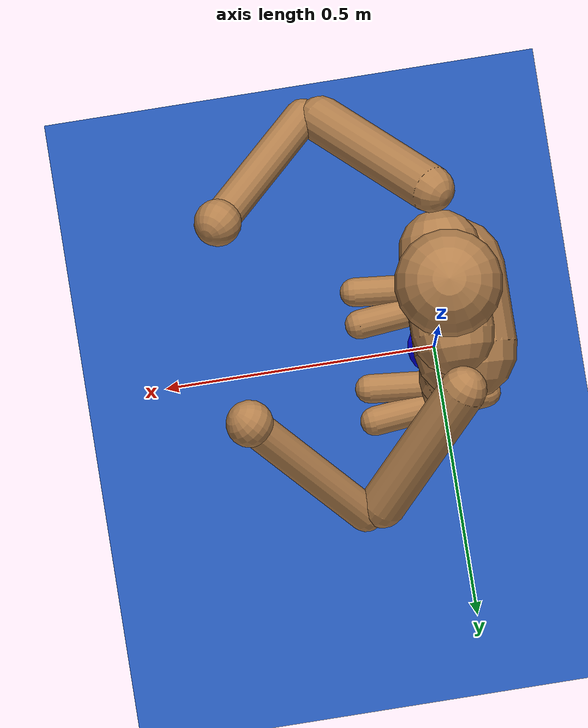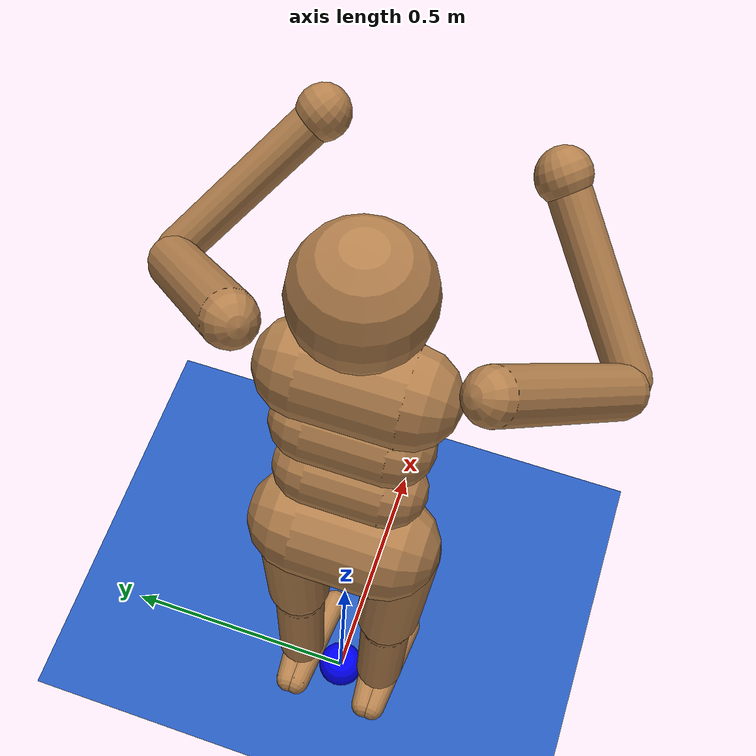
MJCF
<mujoco model="Humanoid Tracking">
  <include file="../common.xml"/>
  <include file="humanoid.xml" />
  <size memory="400K"/>

  <custom>
    <numeric name="task_transition" data="1" />
    <numeric name="agent_planner" data="0" />
    <numeric name="agent_horizon" data="0.6" />
    <numeric name="agent_timestep" data="0.015" />
    <numeric name="sampling_spline_points" data="5" />
    <numeric name="sampling_exploration" data="0.15" />
    <numeric name="gradient_spline_points" data="5" />
  </custom>

  <worldbody>
    <body name="mocap-pelvis" mocap="true">
      <site name="mocap-pelvis" type="sphere" size="0.05" group="0" rgba="0 0 1 1" material="target" />
    </body>
    <body name="mocap-head" mocap="true">
      <site name="mocap-head" type="sphere" size="0.03" group="0" rgba="0 0 1 1" material="target" />
    </body>
    <body name="mocap-ltoe" mocap="true">
      <site name="mocap-ltoe" type="sphere" size="0.03" group="0" rgba="0 0 1 1" material="target" />
    </body>
    <body name="mocap-rtoe" mocap="true">
      <site name="mocap-rtoe" type="sphere" size="0.03" group="0" rgba="0 0 1 1" material="target" />
    </body>
    <body name="mocap-lheel" mocap="true">
      <site name="mocap-lheel" type="sphere" size="0.03" group="0" rgba="0 0 1 1" material="target" />
    </body>
    <body name="mocap-rheel" mocap="true">
      <site name="mocap-rheel" type="sphere" size="0.03" group="0" rgba="0 0 1 1" material="target" />
    </body>
    <body name="mocap-lknee" mocap="true">
      <site name="mocap-lknee" type="sphere" size="0.03" group="0" rgba="0 0 1 1" material="target" />
    </body>
    <body name="mocap-rknee" mocap="true">
      <site name="mocap-rknee" type="sphere" size="0.03" group="0" rgba="0 0 1 1" material="target" />
    </body>
    <body name="mocap-lhand" mocap="true">
      <site name="mocap-lhand" type="sphere" size="0.03" group="0" rgba="0 0 1 1" material="target" />
    </body>
    <body name="mocap-rhand" mocap="true">
      <site name="mocap-rhand" type="sphere" size="0.03" group="0" rgba="0 0 1 1" material="target" />
    </body>
    <body name="mocap-lelbow" mocap="true">
      <site name="mocap-lelbow" type="sphere" size="0.03" group="0" rgba="0 0 1 1" material="target" />
    </body>
    <body name="mocap-relbow" mocap="true">
      <site name="mocap-relbow" type="sphere" size="0.03" group="0" rgba="0 0 1 1" material="target" />
    </body>
    <body name="mocap-lshoulder" mocap="true">
      <site name="mocap-lshoulder" type="sphere" size="0.03" group="0" rgba="0 0 1 1" material="target" />
    </body>
    <body name="mocap-rshoulder" mocap="true">
      <site name="mocap-rshoulder" type="sphere" size="0.03" group="0" rgba="0 0 1 1" material="target" />
    </body>
    <body name="mocap-lhip" mocap="true">
      <site name="mocap-lhip" type="sphere" size="0.03" group="0" rgba="0 0 1 1" material="target" />
    </body>
    <body name="mocap-rhip" mocap="true">
      <site name="mocap-rhip" type="sphere" size="0.03" group="0" rgba="0 0 1 1" material="target" />
    </body>
  </worldbody>

  <sensor>
    <user name="control" dim="21" user="3 0.025 0.0 0.1 0.3" />
    <user name="joint vel." dim="27" user="0 0.01 0.0 1.0" />

    <user name="root pos error" dim="3" user="6 10.0 0.0 100.0 0.1" />
    <user name="head pos error" dim="3" user="6 10.0 0.0 100.0 0.1" />
    <user name="ltoe pos error" dim="3" user="6 1.0 0.0 100.0 0.1" />
    <user name="rtoe pos error" dim="3" user="6 1.0 0.0 100.0 0.1" />
    <user name="lheel pos error" dim="3" user="6 1.0 0.0 100.0 0.1" />
    <user name="rheel pos error" dim="3" user="6 1.0 0.0 100.0 0.1" />
    <user name="lknee pos error" dim="3" user="6 10.0 0.0 100.0 0.1" />
    <user name="rknee pos error" dim="3" user="6 10.0 0.0 100.0 0.1" />
    <user name="lhand pos error" dim="3" user="6 1.0 0.0 100.0 0.1" />
    <user name="rhand pos error" dim="3" user="6 1.0 0.0 100.0 0.1" />
    <user name="lelbow pos error" dim="3" user="6 1.0 0.0 100.0 0.1" />
    <user name="relbow pos error" dim="3" user="6 1.0 0.0 100.0 0.1" />
    <user name="lshoulder pos error" dim="3" user="6 10.0 0.0 100.0 0.1" />
    <user name="rshoulder pos error" dim="3" user="6 10.0 0.0 100.0 0.1" />
    <user name="lhip pos error" dim="3" user="6 1.0 0.0 100.0 0.1" />
    <user name="rhip pos error" dim="3" user="6 1.0 0.0 100.0 0.1" />

    <user name="root vel error" dim="3" user="6 0.1 0.0 1.0 0.1" />
    <user name="head vel error" dim="3" user="6 0.1 0.0 1.0 0.1" />
    <user name="ltoe vel error" dim="3" user="6 0.1 0.0 1.0 0.1" />
    <user name="rtoe vel error" dim="3" user="6 0.1 0.0 1.0 0.1" />
    <user name="lheel vel error" dim="3" user="6 0.1 0.0 1.0 0.1" />
    <user name="rheel vel error" dim="3" user="6 0.1 0.0 1.0 0.1" />
    <user name="lknee vel error" dim="3" user="6 0.1 0.0 1.0 0.1" />
    <user name="rknee vel error" dim="3" user="6 0.1 0.0 1.0 0.1" />
    <user name="lhand vel error" dim="3" user="6 0.1 0.0 1.0 0.1" />
    <user name="rhand vel error" dim="3" user="6 0.1 0.0 1.0 0.1" />
    <user name="lelbow vel error" dim="3" user="6 0.1 0.0 1.0 0.1" />
    <user name="relbow vel error" dim="3" user="6 0.1 0.0 1.0 0.1" />
    <user name="lshoulder vel error" dim="3" user="6 0.1 0.0 1.0 0.1" />
    <user name="rshoulder vel error" dim="3" user="6 0.1 0.0 1.0 0.1" />
    <user name="lhip vel error" dim="3" user="6 0.1 0.0 1.0 0.1" />
    <user name="rhip vel error" dim="3" user="6 0.1 0.0 1.0 0.1" />

    <framepos name="trace" objtype="body" objname="torso"/>

    <framepos name="tracking_pose[pelvis]" objtype="site" objname="pelvis"/>
    <framepos name="tracking_pose[head]" objtype="body" objname="head"/>
    <framepos name="tracking_pose[ltoe]" objtype="site" objname="toe1_left"/>
    <framepos name="tracking_pose[rtoe]" objtype="site" objname="toe1_right"/>
    <framepos name="tracking_pose[lheel]" objtype="site" objname="heel1_left"/>
    <framepos name="tracking_pose[rheel]" objtype="site" objname="heel1_right"/>
    <framepos name="tracking_pose[lknee]" objtype="site" objname="knee_left"/>
    <framepos name="tracking_pose[rknee]" objtype="site" objname="knee_right"/>
    <framepos name="tracking_pose[lhand]" objtype="site" objname="hand_left"/>
    <framepos name="tracking_pose[rhand]" objtype="site" objname="hand_right"/>
    <framepos name="tracking_pose[lelbow]" objtype="site" objname="elbow_left"/>
    <framepos name="tracking_pose[relbow]" objtype="site" objname="elbow_right"/>
    <framepos name="tracking_pose[lshoulder]" objtype="site" objname="shoulder_left"/>
    <framepos name="tracking_pose[rshoulder]" objtype="site" objname="shoulder_right"/>
    <framepos name="tracking_pose[lhip]" objtype="site" objname="thigh_left"/>
    <framepos name="tracking_pose[rhip]" objtype="site" objname="thigh_right"/>

    <framelinvel name="tracking_vel[pelvis]" objtype="site" objname="pelvis"/>
    <framelinvel name="tracking_vel[head]" objtype="body" objname="head"/>
    <framelinvel name="tracking_vel[ltoe]" objtype="site" objname="toe1_left"/>
    <framelinvel name="tracking_vel[rtoe]" objtype="site" objname="toe1_right"/>
    <framelinvel name="tracking_vel[lheel]" objtype="site" objname="heel1_left"/>
    <framelinvel name="tracking_vel[rheel]" objtype="site" objname="heel1_right"/>
    <framelinvel name="tracking_vel[lknee]" objtype="site" objname="knee_left"/>
    <framelinvel name="tracking_vel[rknee]" objtype="site" objname="knee_right"/>
    <framelinvel name="tracking_vel[lhand]" objtype="site" objname="hand_left"/>
    <framelinvel name="tracking_vel[rhand]" objtype="site" objname="hand_right"/>
    <framelinvel name="tracking_vel[lelbow]" objtype="site" objname="elbow_left"/>
    <framelinvel name="tracking_vel[relbow]" objtype="site" objname="elbow_right"/>
    <framelinvel name="tracking_vel[lshoulder]" objtype="site" objname="shoulder_left"/>
    <framelinvel name="tracking_vel[rshoulder]" objtype="site" objname="shoulder_right"/>
    <framelinvel name="tracking_vel[lhip]" objtype="site" objname="thigh_left"/>
    <framelinvel name="tracking_vel[rhip]" objtype="site" objname="thigh_right"/>
  </sensor>

  <include file="./keyframes/CMU-CMU-137-137_40_poses.xml" />
</mujoco>

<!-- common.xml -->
<mujoco>

    <visual>
        <headlight ambient=".4 .4 .4" diffuse=".8 .8 .8" specular="0.1 0.1 0.1"/>
        <map znear=".01"/>
        <quality shadowsize="2048"/>
        <global elevation="-15"/>
    </visual>

    <asset>
        <texture name="blue_grid" type="2d" builtin="checker" rgb1=".02 .14 .44" rgb2=".27 .55 1" width="300" height="300" mark="edge" markrgb="1 1 1"/>
        <material name="blue_grid" texture="blue_grid" texrepeat="1 1" texuniform="true" reflectance=".2"/>

        <texture name="grey_grid" type="2d" builtin="checker" rgb1=".26 .26 .26" rgb2=".6 .6 .6" width="300" height="300" mark="edge" markrgb="1 1 1"/>
        <material name="grey_grid" texture="grey_grid" texrepeat="1 1" texuniform="true" reflectance=".2"/>
        <texture name="skybox" type="skybox" builtin="gradient" rgb1=".66 .79 1" rgb2=".9 .91 .93" width="800" height="800"/>

        <material name="self" rgba=".7 .5 .3 1"/>
        <material name="self_default" rgba=".7 .5 .3 1"/>
        <material name="self_highlight" rgba="0 .5 .3 1"/>
        <material name="effector" rgba=".7 .4 .2 1"/>
        <material name="effector_default" rgba=".7 .4 .2 1"/>
        <material name="effector_highlight" rgba="0 .5 .3 1"/>
        <material name="decoration" rgba=".2 .6 .3 1"/>
        <material name="eye" rgba="0 .2 1 1"/>
        <material name="target" rgba=".6 .3 .3 1"/>
        <material name="target_default" rgba=".6 .3 .3 1"/>
        <material name="target_highlight" rgba=".6 .3 .3 .4"/>
        <material name="site" rgba=".5 .5 .5 .3"/>
    </asset>

    <size memory="1M"/>

    <statistic extent="0.4" center="0.3 0.1 0"/>

    <visual>
        <quality shadowsize="8192"/>
        <global azimuth="180" elevation="-30"/>
    </visual>

    <default>
        <geom friction="1.0"/>
    </default>

    <compiler angle="radian" autolimits="true"/>

    <asset>
        <mesh name="apple" file="../../shared_assets/apple/apple.obj" />
        <mesh name="apple_contact0" file="../../shared_assets/apple/contact0.stl"  />
        <mesh name="apple_contact1" file="../../shared_assets/apple/contact1.stl"  />

        <mesh name="doorknob" file="../../shared_assets/doorknob/doorknob.obj" />

        <mesh name="flashlight" file="../../shared_assets/flashlight/flashlight.obj" />
        <mesh name="flashlight_contact0" file="../../shared_assets/flashlight/contact0.stl"  />
        <mesh name="flashlight_contact1" file="../../shared_assets/flashlight/contact1.stl"  />

        <mesh name="hammer" file="../../shared_assets/hammer/hammer.obj" />
        <mesh name="hammer_contact0" file="../../shared_assets/hammer/contact0.stl"  />
        <mesh name="hammer_contact1" file="../../shared_assets/hammer/contact1.stl"  />

        <mesh name="phone" file="../../shared_assets/phone/phone.obj" />
        <mesh name="phone_contact0" file="../../shared_assets/phone/contact0.stl"  />
        <mesh name="phone_contact1" file="../../shared_assets/phone/contact1.stl"  />
        <mesh name="phone_contact2" file="../../shared_assets/phone/contact2.stl"  />

        <mesh name="stapler" file="../../shared_assets/stapler/stapler.obj" />
        <mesh name="stapler_contact0" file="../../shared_assets/stapler/contact0.stl"  />
        <mesh name="stapler_contact1" file="../../shared_assets/stapler/contact1.stl"  />
        <mesh name="stapler_contact2" file="../../shared_assets/stapler/contact2.stl"  />
        <mesh name="stapler_contact3" file="../../shared_assets/stapler/contact3.stl"  />
        <mesh name="stapler_contact4" file="../../shared_assets/stapler/contact4.stl"  />

        <mesh name="waterbottle" file="../../shared_assets/waterbottle/waterbottle.obj" />
        <mesh name="waterbottle_contact0" file="../../shared_assets/waterbottle/contact0.stl"  />
        <mesh name="waterbottle_contact1" file="../../shared_assets/waterbottle/contact1.stl"  />
    </asset>

</mujoco>

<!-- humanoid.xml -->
<mujoco model="Humanoid">

  <statistic extent="2" center="0 0 1"/>

  <default>
    <motor ctrlrange="-1 1" ctrllimited="true"/>
    <site size=".04" group="3"/>
    <default class="body">

      <!-- geoms -->
      <geom type="capsule" condim="1" friction=".7" solimp=".9 .99 .003" solref=".015 1" material="self" group="2"/>
      <default class="thigh">
        <geom size=".06"/>
      </default>
      <default class="shin">
        <geom fromto="0 0 0 0 0 -.3"  size=".049"/>
      </default>
      <default class="foot">
        <geom size=".027"/>
        <default class="foot1">
          <geom fromto="-.07 -.01 0 .14 -.03 0"/>
        </default>
        <default class="foot2">
          <geom fromto="-.07 .01 0 .14  .03 0"/>
        </default>
      </default>
      <default class="arm_upper">
        <geom size=".04"/>
      </default>
      <default class="arm_lower">
        <geom size=".031"/>
      </default>
      <default class="hand">
        <geom type="sphere" size=".04"/>
      </default>

      <!-- joints -->
      <joint type="hinge" damping=".2" stiffness="1" armature=".01" limited="true" solimplimit="0 .99 .01"/>
      <default class="joint_big">
        <joint damping="5" stiffness="10"/>
        <default class="hip_x">
          <joint range="-30 10"/>
        </default>
        <default class="hip_z">
          <joint range="-60 35"/>
        </default>
        <default class="hip_y">
          <joint axis="0 1 0" range="-150 20"/>
        </default>
        <default class="joint_big_stiff">
          <joint stiffness="20"/>
        </default>
      </default>
      <default class="knee">
        <joint pos="0 0 .02" axis="0 -1 0" range="-160 2"/>
      </default>
      <default class="ankle">
        <joint range="-50 50"/>
        <default class="ankle_y">
          <joint pos="0 0 .08" axis="0 1 0" stiffness="6"/>
        </default>
        <default class="ankle_x">
          <joint pos="0 0 .04" stiffness="3"/>
        </default>
      </default>
      <default class="shoulder">
        <joint range="-85 60"/>
      </default>
      <default class="elbow">
        <joint range="-100 50" stiffness="0"/>
      </default>

      <!-- tracking site -->
      <default class="tracking_site">
        <site type="sphere" size="0.027" rgba="1 0 0 1" group="3"/>
      </default>
    </default>

    <default class="active_adhesion">
      <geom rgba=".8 .5 .5 1" margin=".01" gap=".01"/>
    </default>
  </default>

  <worldbody>
    <geom name="floor" type="plane" conaffinity="1" size="50 50 .05" material="blue_grid"/>
    <body name="torso" pos="0 0 1.282" childclass="body">
      <light name="top" pos="0 0 2" mode="trackcom"/>
      <camera name="back" pos="-3 0 1" xyaxes="0 -1 0 1 0 2" mode="trackcom"/>
      <camera name="side" pos="0 -3 1" xyaxes="1 0 0 0 1 2" mode="trackcom"/>
      <freejoint name="root"/>
      <geom name="torso" fromto="0 -.07 0 0 .07 0" size=".07"/>
      <geom name="waist_upper" fromto="-.01 -.06 -.12 -.01 .06 -.12" size=".06"/>
      <body name="head" pos="0 0 .19">
        <geom name="head" type="sphere" size=".09"/>
        <site name="tracking[head]" class="tracking_site" pos="0.09 0 0" />
        <camera name="egocentric" pos=".09 0 0" xyaxes="0 -1 0 .1 0 1" fovy="80"/>
      </body>
      <body name="waist_lower" pos="-.01 0 -.26">
        <geom name="waist_lower" fromto="0 -.06 0 0 .06 0" size=".06"/>
        <joint name="abdomen_z" pos="0 0 .065" axis="0 0 1" range="-45 45" class="joint_big_stiff"/>
        <joint name="abdomen_y" pos="0 0 .065" axis="0 1 0" range="-75 30" class="joint_big"/>
        <body name="pelvis" pos="0 0 -.165">
          <site name="tracking[pelvis]" class="tracking_site" pos="0 0 0.075" size=".05" />
          <joint name="abdomen_x" pos="0 0 .1" axis="1 0 0" range="-35 35" class="joint_big"/>
          <geom name="butt" fromto="-.02 -.07 0 -.02 .07 0" size=".09"/>
          <body name="thigh_right" pos="0 -.1 -.04">
            <site name="tracking[rhip]" class="tracking_site" pos="0 0.025 0.025" />
            <joint name="hip_x_right" axis="1 0 0" class="hip_x"/>
            <joint name="hip_z_right" axis="0 0 1" class="hip_z"/>
            <joint name="hip_y_right" class="hip_y"/>
            <geom name="thigh_right" fromto="0 0 0 0 .01 -.34" class="thigh"/>
            <body name="shin_right" pos="0 .01 -.4">
              <joint name="knee_right" class="knee"/>
              <site name="tracking[rknee]" class="tracking_site" pos="0 0 0.05" />
              <geom name="shin_right" class="shin"/>
              <body name="foot_right" pos="0 0 -.39">
                <joint name="ankle_y_right" class="ankle_y"/>
                <joint name="ankle_x_right" class="ankle_x" axis="1 0 .5"/>
                <geom name="foot1_right" class="foot1"/>
                <geom name="foot2_right" class="foot2"/>
                <site name="foot_right" pos=".05 .03 0" type="sphere" size=".027"/>
                <site name="sp2" pos="-.07 0 0" type="sphere" size=".027"/>
                <site name="sp3" pos=".14 0 0" type="sphere" size=".027"/>
                <body name="heel_right" pos="-0.05 0 0.04">
                  <site name="tracking[rheel]" class="tracking_site" />
                </body>
                <body name="toe_right" pos="0.07 0 -0.01">
                  <site name="tracking[rtoe]" class="tracking_site" />
                </body>
              </body>
            </body>
          </body>
          <body name="thigh_left" pos="0 .1 -.04">
            <site name="tracking[lhip]" class="tracking_site" pos="0 -0.025 0.025" />
            <joint name="hip_x_left" axis="-1 0 0" class="hip_x"/>
            <joint name="hip_z_left" axis="0 0 -1" class="hip_z"/>
            <joint name="hip_y_left" class="hip_y"/>
            <geom name="thigh_left" fromto="0 0 0 0 -.01 -.34" class="thigh"/>
            <body name="shin_left" pos="0 -.01 -.4">
              <joint name="knee_left" class="knee"/>
              <site name="tracking[lknee]" class="tracking_site" pos="0 0 0.05" />
              <geom name="shin_left" fromto="0 0 0 0 0 -.3" class="shin"/>
              <body name="foot_left" pos="0 0 -.39">
                <joint name="ankle_y_left" class="ankle_y"/>
                <joint name="ankle_x_left" class="ankle_x" axis="-1 0 -.5"/>
                <geom name="foot1_left" class="foot1"/>
                <geom name="foot2_left" class="foot2"/>
                <site name="foot_left" pos=".05 -.03 0" type="sphere" size=".027"/>
                <site name="sp0" pos="-.07 0 0" type="sphere" size=".027"/>
                <site name="sp1" pos=".14 0 0" type="sphere" size=".027"/>
                <body name="heel_left" pos="-0.05 0 0.04">
                  <site name="tracking[lheel]" class="tracking_site" />
                </body>
                <body name="toe_left" pos="0.07 0 -0.01">
                  <site name="tracking[ltoe]" class="tracking_site" />
                </body>
              </body>
            </body>
          </body>
        </body>
      </body>
      <body name="upper_arm_right" pos="0 -.17 .06">
        <site name="tracking[rshoulder]" class="tracking_site" />
        <joint name="shoulder1_right" axis="2 1 1"  class="shoulder"/>
        <joint name="shoulder2_right" axis="0 -1 1" class="shoulder"/>
        <geom name="upper_arm_right" fromto="0 0 0 .16 -.16 -.16" class="arm_upper"/>
        <body name="lower_arm_right" pos=".18 -.18 -.18">
          <joint name="elbow_right" axis="0 -1 1" class="elbow"/>
          <site name="tracking[relbow]" class="tracking_site" />
          <site name="tracking[rhand]" class="tracking_site" pos="0.13 0.13 0.13" />
          <geom name="lower_arm_right" fromto=".01 .01 .01 .17 .17 .17" class="arm_lower"/>
          <body name="hand_right" pos=".18 .18 .18">
            <geom name="hand_right" zaxis="1 1 1" class="hand"/>
          </body>
        </body>
      </body>
      <body name="upper_arm_left" pos="0 .17 .06">
        <site name="tracking[lshoulder]" class="tracking_site" />
        <joint name="shoulder1_left" axis="-2 1 -1" class="shoulder"/>
        <joint name="shoulder2_left" axis="0 -1 -1"  class="shoulder"/>
        <geom name="upper_arm_left" fromto="0 0 0 .16 .16 -.16" class="arm_upper"/>
        <body name="lower_arm_left" pos=".18 .18 -.18">
          <joint name="elbow_left" axis="0 -1 -1" class="elbow"/>
          <site name="tracking[lelbow]" class="tracking_site" />
          <site name="tracking[lhand]" class="tracking_site" pos="0.13 -0.13 0.13" />
          <geom name="lower_arm_left" fromto=".01 -.01 .01 .17 -.17 .17" class="arm_lower"/>
          <body name="hand_left" pos=".18 -.18 .18">
            <geom name="hand_left" zaxis="1 -1 1" class="hand"/>
          </body>
        </body>
      </body>
    </body>
  </worldbody>

  <contact>
    <exclude body1="waist_lower" body2="thigh_right"/>
    <exclude body1="waist_lower" body2="thigh_left"/>
  </contact>

  <tendon>
    <fixed name="hamstring_right" limited="true" range="-0.3 2">
      <joint joint="hip_y_right" coef=".5"/>
      <joint joint="knee_right" coef="-.5"/>
    </fixed>
    <fixed name="hamstring_left" limited="true" range="-0.3 2">
      <joint joint="hip_y_left" coef=".5"/>
      <joint joint="knee_left" coef="-.5"/>
    </fixed>
  </tendon>

  <actuator>
    <motor name="abdomen_y"       gear="40"  joint="abdomen_y"/>
    <motor name="abdomen_z"       gear="40"  joint="abdomen_z"/>
    <motor name="abdomen_x"       gear="40"  joint="abdomen_x"/>
    <motor name="hip_x_right"     gear="40"  joint="hip_x_right"/>
    <motor name="hip_z_right"     gear="40"  joint="hip_z_right"/>
    <motor name="hip_y_right"     gear="120" joint="hip_y_right"/>
    <motor name="knee_right"      gear="100" joint="knee_right"/>
    <motor name="ankle_x_right"   gear="20"  joint="ankle_x_right"/>
    <motor name="ankle_y_right"   gear="20"  joint="ankle_y_right"/>
    <motor name="hip_x_left"      gear="40"  joint="hip_x_left"/>
    <motor name="hip_z_left"      gear="40"  joint="hip_z_left"/>
    <motor name="hip_y_left"      gear="120" joint="hip_y_left"/>
    <motor name="knee_left"       gear="100" joint="knee_left"/>
    <motor name="ankle_x_left"    gear="20"  joint="ankle_x_left"/>
    <motor name="ankle_y_left"    gear="20"  joint="ankle_y_left"/>
    <motor name="shoulder1_right" gear="20"  joint="shoulder1_right"/>
    <motor name="shoulder2_right" gear="20"  joint="shoulder2_right"/>
    <motor name="elbow_right"     gear="40"  joint="elbow_right"/>
    <motor name="shoulder1_left"  gear="20"  joint="shoulder1_left"/>
    <motor name="shoulder2_left"  gear="20"  joint="shoulder2_left"/>
    <motor name="elbow_left"      gear="40"  joint="elbow_left"/>
    <adhesion name="left_hand" body="hand_left" ctrlrange="0 1" gain="1000"/>
    <adhesion name="left_right" body="hand_right" ctrlrange="0 1" gain="1000"/>
  </actuator>

</mujoco>

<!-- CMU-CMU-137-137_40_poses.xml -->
<mujoco>
  <keyframe>
    <key name="home" mpos="0.0 0.0 1.02568 0.01021 -0.03196 1.59165 0.17847 0.0616 0.13485 -0.12518 -0.14189 0.13228 0.05661 0.10826 0.16664 -0.13351 -0.01339 0.17221 0.10697 0.08061 0.56309 -0.09407 -0.11022 0.5593 0.22096 0.09202 0.95222 -0.22236 -0.14133 0.93995 0.14129 0.1696 1.17546 -0.23019 -0.0291 1.16932 0.13773 0.10591 1.42893 -0.18498 -0.04352 1.41986 0.06167 0.03192 0.93396 -0.0552 -0.03996 0.93541" qpos="0.0 0.0 1.24521 0.87082 -0.03859 -0.06076 -0.48631 0.00209 -0.01788 0.03384 -0.16502 -0.33149 0.07668 -0.43343 -0.38638 -0.1762 -0.10702 -0.38088 0.23938 -0.13081 -0.34138 0.24661 0.73546 -0.89064 -1.07099 -0.74863 0.83653 -0.99225" qvel="-0.02046 0.01627 -0.0117 5e-05 -0.06169 0.06239 -0.09216 0.07134 0.05326 -0.08996 -0.15279 -0.13992 -0.33565 -0.45389 0.23026 0.04693 -0.29987 -0.16378 -0.30147 -0.2313 -0.10329 0.02853 -0.0808 -0.18459 0.00873 -0.01268 -0.07505" />
    <key mpos="-0.00018 0.00036 1.02534 0.00938 -0.03214 1.59138 0.178 0.06062 0.13416 -0.12518 -0.1418 0.1322 0.05629 0.10757 0.16611 -0.13367 -0.01332 0.17218 0.107 0.07844 0.5624 -0.09367 -0.11067 0.55909 0.2205 0.09302 0.95223 -0.22445 -0.13978 0.93897 0.14023 0.16992 1.17549 -0.23146 -0.02869 1.16892 0.13665 0.10661 1.42905 -0.18567 -0.04362 1.41933 0.06142 0.03224 0.93355 -0.05531 -0.03988 0.93515" />
    <key mpos="-0.00013 0.00068 1.02475 0.00859 -0.03207 1.59063 0.17779 0.06041 0.13417 -0.12517 -0.14165 0.13209 0.0561 0.10799 0.16526 -0.13369 -0.01318 0.17208 0.10642 0.07773 0.56152 -0.09317 -0.11136 0.55872 0.21997 0.09409 0.95225 -0.22652 -0.13791 0.9375 0.13917 0.17101 1.17531 -0.23276 -0.02798 1.16803 0.13575 0.10756 1.42884 -0.18607 -0.04363 1.41822 0.06137 0.03242 0.93285 -0.05531 -0.03975 0.93468" />
    <key mpos="-5e-05 0.00097 1.02406 0.00806 -0.03188 1.58988 0.17778 0.06069 0.13422 -0.12532 -0.14143 0.13186 0.05615 0.10908 0.16421 -0.13387 -0.01297 0.17188 0.10511 0.07883 0.56063 -0.093 -0.11184 0.55831 0.21958 0.09538 0.95251 -0.22837 -0.13616 0.93597 0.13829 0.17277 1.17523 -0.23369 -0.02735 1.16706 0.13527 0.10851 1.42856 -0.1861 -0.04352 1.41705 0.06125 0.0326 0.93199 -0.05542 -0.03959 0.93417" />
    <key mpos="-5e-05 0.00141 1.02365 0.00783 -0.03166 1.58946 0.17793 0.06085 0.13404 -0.12544 -0.14134 0.13163 0.05636 0.10979 0.16339 -0.13402 -0.01291 0.17172 0.1035 0.08085 0.56014 -0.09306 -0.11197 0.55809 0.21929 0.09692 0.95286 -0.22981 -0.13447 0.9346 0.13777 0.17458 1.1754 -0.234 -0.02691 1.16629 0.1351 0.10942 1.42851 -0.18586 -0.04327 1.41617 0.06107 0.03305 0.93147 -0.05556 -0.0392 0.93386" />
    <key mpos="-0.00013 0.00203 1.02376 0.00804 -0.03125 1.58964 0.17812 0.06084 0.13386 -0.12537 -0.14139 0.13151 0.05657 0.10995 0.16303 -0.13391 -0.01299 0.1717 0.10136 0.08334 0.56021 -0.09305 -0.11145 0.55824 0.21929 0.09844 0.95336 -0.2308 -0.13277 0.93377 0.13777 0.17576 1.17602 -0.23371 -0.02673 1.16618 0.13512 0.11022 1.42903 -0.18559 -0.04292 1.41607 0.06084 0.03383 0.93153 -0.0557 -0.03856 0.934" />
    <key mpos="-0.00014 0.00272 1.02395 0.00813 -0.03091 1.58974 0.17829 0.06073 0.13371 -0.12522 -0.14143 0.13144 0.05673 0.10988 0.16274 -0.13374 -0.01304 0.17169 0.09893 0.08622 0.56039 -0.09306 -0.11069 0.55845 0.21952 0.10018 0.95389 -0.23132 -0.13113 0.93349 0.13815 0.17685 1.17683 -0.23342 -0.0263 1.16646 0.13521 0.11089 1.42973 -0.18541 -0.04259 1.41636 0.06063 0.03477 0.93168 -0.05577 -0.03784 0.93422" />
    <key mpos="-0.0001 0.00351 1.024 0.00851 -0.03027 1.59001 0.17849 0.06067 0.13354 -0.12517 -0.1414 0.13126 0.05693 0.10992 0.16242 -0.13365 -0.01302 0.17155 0.09711 0.08873 0.56042 -0.0932 -0.10988 0.55853 0.21987 0.10178 0.95408 -0.23122 -0.1296 0.93331 0.13896 0.17809 1.17731 -0.23362 -0.02563 1.16666 0.13535 0.11149 1.43003 -0.18516 -0.04224 1.41645 0.06046 0.03581 0.93167 -0.05581 -0.03701 0.93429" />
    <key mpos="-9e-05 0.0043 1.02397 0.0086 -0.02998 1.58996 0.1785 0.06078 0.13347 -0.12516 -0.14133 0.13122 0.05695 0.11018 0.1622 -0.13355 -0.01293 0.17148 0.09602 0.09059 0.56039 -0.09321 -0.10933 0.55859 0.22026 0.10342 0.95417 -0.23053 -0.12807 0.93334 0.13995 0.17964 1.17764 -0.23469 -0.02469 1.16693 0.13552 0.11193 1.43005 -0.18496 -0.04186 1.41643 0.06032 0.03674 0.9316 -0.05585 -0.03624 0.93431" />
    <key mpos="-9e-05 0.00488 1.02395 0.00874 -0.02978 1.58989 0.17861 0.06083 0.13345 -0.12518 -0.14121 0.13108 0.05713 0.11041 0.16209 -0.13348 -0.01284 0.17143 0.09552 0.09191 0.5604 -0.09309 -0.10896 0.55861 0.22059 0.10499 0.95415 -0.22924 -0.12675 0.93381 0.14084 0.18093 1.17792 -0.2365 -0.02373 1.16748 0.13566 0.11233 1.43007 -0.1848 -0.04158 1.41654 0.06023 0.03741 0.93155 -0.05587 -0.03567 0.9343" />
    <key mpos="-2e-05 0.00531 1.02392 0.00915 -0.02947 1.58984 0.17876 0.06079 0.13339 -0.12516 -0.14122 0.13099 0.05731 0.1105 0.16198 -0.13336 -0.01286 0.17139 0.095 0.09299 0.5604 -0.09296 -0.10875 0.55861 0.22105 0.10644 0.95411 -0.22791 -0.1256 0.93438 0.1414 0.18201 1.17804 -0.23829 -0.02263 1.16796 0.13581 0.11273 1.43 -0.18458 -0.04134 1.41653 0.06027 0.03786 0.93151 -0.05579 -0.03528 0.93428" />
    <key mpos="5e-05 0.00547 1.02382 0.00956 -0.02906 1.58973 0.17895 0.06068 0.13322 -0.12515 -0.14127 0.13079 0.05747 0.11032 0.16177 -0.13323 -0.01292 0.17125 0.09412 0.09406 0.56034 -0.09306 -0.10859 0.55856 0.22126 0.10794 0.95395 -0.22678 -0.12473 0.93484 0.14169 0.18312 1.17804 -0.23951 -0.02165 1.16825 0.13587 0.11317 1.42981 -0.18446 -0.04099 1.41648 0.06038 0.03789 0.93139 -0.05577 -0.0351 0.93421" />
    <key mpos="0.0001 0.00538 1.02369 0.01 -0.02823 1.58975 0.17911 0.06041 0.13301 -0.12508 -0.14161 0.13052 0.05756 0.10991 0.16151 -0.13305 -0.01326 0.171 0.09292 0.09495 0.56025 -0.0934 -0.10846 0.55848 0.22114 0.10966 0.95346 -0.22611 -0.12427 0.93504 0.14208 0.18413 1.17796 -0.23997 -0.02097 1.1683 0.13596 0.11355 1.42955 -0.18446 -0.04032 1.41642 0.06053 0.03753 0.93123 -0.05586 -0.0351 0.93413" />
    <key mpos="8e-05 0.00505 1.02349 0.01 -0.0277 1.5895 0.17928 0.06001 0.13274 -0.12504 -0.14203 0.13025 0.05768 0.1094 0.16121 -0.1329 -0.01368 0.17078 0.09222 0.09501 0.56005 -0.09377 -0.10865 0.55836 0.22074 0.11042 0.95316 -0.22588 -0.12409 0.93506 0.14251 0.18493 1.17795 -0.23997 -0.02042 1.16813 0.13617 0.11376 1.42937 -0.18458 -0.03944 1.41631 0.06065 0.03673 0.93096 -0.05606 -0.03536 0.93401" />
    <key mpos="7e-05 0.00441 1.02328 0.00974 -0.02726 1.58923 0.17951 0.05965 0.13259 -0.12506 -0.14228 0.13007 0.0579 0.10903 0.16103 -0.13282 -0.01393 0.17062 0.0924 0.09423 0.55985 -0.09416 -0.10904 0.55822 0.22009 0.11098 0.95267 -0.22601 -0.12378 0.935 0.14293 0.18532 1.17787 -0.23973 -0.01973 1.16792 0.13649 0.11372 1.42916 -0.18486 -0.03824 1.41625 0.06082 0.03559 0.9307 -0.05627 -0.03588 0.93387" />
    <key mpos="7e-05 0.00347 1.02319 0.00953 -0.02673 1.58922 0.17971 0.05922 0.13263 -0.12503 -0.14255 0.13002 0.0581 0.10865 0.16099 -0.13273 -0.01421 0.1706 0.09303 0.09276 0.55973 -0.09447 -0.10964 0.55816 0.21929 0.11129 0.95194 -0.2264 -0.12346 0.93506 0.14338 0.18526 1.17769 -0.23949 -0.01899 1.16784 0.13708 0.11326 1.42887 -0.18514 -0.03686 1.41633 0.06097 0.03421 0.93056 -0.05649 -0.03664 0.93384" />
    <key mpos="0.0001 0.00253 1.02314 0.00945 -0.02607 1.58945 0.17985 0.05879 0.13268 -0.12498 -0.14283 0.13007 0.05824 0.10826 0.16099 -0.13263 -0.01449 0.17064 0.09364 0.09127 0.55964 -0.09471 -0.11026 0.55815 0.21845 0.11134 0.95103 -0.22693 -0.12321 0.93531 0.14389 0.18491 1.17737 -0.23933 -0.01821 1.16788 0.1377 0.11277 1.42851 -0.18536 -0.03546 1.4165 0.06111 0.0329 0.93046 -0.05668 -0.0374 0.93385" />
    <key mpos="0.00017 0.00179 1.02309 0.00943 -0.02543 1.58968 0.17991 0.05868 0.13266 -0.1251 -0.14287 0.13004 0.0583 0.10814 0.16097 -0.1327 -0.01453 0.17063 0.09402 0.09018 0.55955 -0.09517 -0.11049 0.55813 0.21774 0.11116 0.95 -0.22758 -0.12268 0.93569 0.14439 0.18403 1.17695 -0.23935 -0.01719 1.16808 0.13844 0.11212 1.42817 -0.18546 -0.03427 1.41672 0.06123 0.03187 0.93035 -0.05683 -0.03797 0.93386" />
    <key mpos="0.00025 0.00114 1.02309 0.00946 -0.02494 1.58995 0.17983 0.05866 0.13265 -0.12524 -0.1428 0.13001 0.0582 0.10806 0.16099 -0.13282 -0.01447 0.17065 0.09421 0.08933 0.55951 -0.09553 -0.11062 0.55813 0.21734 0.11027 0.949 -0.22828 -0.12202 0.93612 0.14497 0.18252 1.17647 -0.23942 -0.01632 1.16844 0.1392 0.11124 1.42787 -0.18551 -0.03346 1.41708 0.06134 0.03102 0.93031 -0.05694 -0.03844 0.9339" />
    <key mpos="0.00041 0.00043 1.02309 0.00958 -0.02456 1.59025 0.1798 0.05859 0.13267 -0.12526 -0.1428 0.13 0.05816 0.10795 0.16104 -0.13278 -0.01448 0.17066 0.09445 0.08857 0.55951 -0.09551 -0.11086 0.55809 0.21694 0.10887 0.94852 -0.22877 -0.12157 0.93646 0.14526 0.18144 1.17611 -0.23933 -0.01587 1.16881 0.13975 0.11077 1.42768 -0.18539 -0.03304 1.41744 0.06153 0.03018 0.93028 -0.05693 -0.03896 0.93392" />
    <key mpos="0.00068 -0.00018 1.02305 0.00975 -0.02434 1.59051 0.17981 0.05855 0.13268 -0.12524 -0.14284 0.13001 0.05819 0.10794 0.16109 -0.13271 -0.01453 0.17072 0.09485 0.08795 0.55948 -0.09516 -0.11131 0.55801 0.21674 0.10716 0.94839 -0.22918 -0.12117 0.93664 0.14548 0.18073 1.17578 -0.23921 -0.01558 1.16906 0.14025 0.11032 1.42744 -0.18514 -0.03288 1.41765 0.06184 0.02951 0.93025 -0.05673 -0.03946 0.93387" />
    <key mpos="0.00109 -0.00073 1.02296 0.00998 -0.02414 1.59058 0.1798 0.05852 0.13275 -0.12516 -0.14292 0.13007 0.05819 0.10794 0.16111 -0.1326 -0.01463 0.17085 0.0953 0.08746 0.55944 -0.09457 -0.11206 0.55793 0.21679 0.10523 0.94847 -0.22954 -0.1209 0.93652 0.14566 0.18038 1.17539 -0.23906 -0.01561 1.16909 0.14062 0.11014 1.4271 -0.18484 -0.03288 1.41765 0.06232 0.02887 0.93018 -0.05629 -0.04002 0.93376" />
    <key mpos="0.00155 -0.00124 1.02289 0.0102 -0.02399 1.59054 0.17974 0.05856 0.13283 -0.12509 -0.14298 0.13025 0.0581 0.10795 0.16114 -0.13247 -0.0147 0.17106 0.09567 0.08705 0.55941 -0.09386 -0.11294 0.55788 0.21712 0.10314 0.94878 -0.22981 -0.12084 0.93621 0.14588 0.18009 1.17506 -0.23885 -0.01589 1.16895 0.14088 0.11008 1.42683 -0.18451 -0.03309 1.41749 0.06287 0.02829 0.93014 -0.05574 -0.04062 0.93367" />
    <key mpos="0.00205 -0.00171 1.02285 0.01023 -0.0237 1.59066 0.1797 0.05851 0.13289 -0.12497 -0.14318 0.13048 0.05804 0.10787 0.16119 -0.13236 -0.01489 0.17129 0.09615 0.08658 0.55939 -0.09317 -0.11383 0.55788 0.21779 0.10068 0.94919 -0.22986 -0.12111 0.93589 0.14643 0.17949 1.17479 -0.23868 -0.01649 1.1688 0.1409 0.11027 1.42677 -0.18423 -0.03345 1.41733 0.06341 0.0278 0.93012 -0.05513 -0.04123 0.93362" />
    <key mpos="0.00259 -0.00196 1.02299 0.01006 -0.02314 1.59132 0.17966 0.0586 0.13311 -0.1249 -0.14325 0.13086 0.05802 0.10797 0.16145 -0.13226 -0.01496 0.17167 0.09683 0.0863 0.55956 -0.09242 -0.11449 0.55803 0.21845 0.09921 0.95009 -0.22989 -0.12122 0.93581 0.14677 0.17962 1.17502 -0.23856 -0.01702 1.16892 0.14087 0.11061 1.42705 -0.18391 -0.03385 1.41741 0.06396 0.02767 0.93031 -0.05444 -0.04159 0.93373" />
    <key mpos="0.00308 -0.00172 1.02346 0.00968 -0.02214 1.5928 0.17953 0.05915 0.1336 -0.12489 -0.14296 0.13144 0.0579 0.10852 0.16201 -0.13216 -0.01468 0.17227 0.09741 0.08655 0.56003 -0.09162 -0.11457 0.55848 0.21928 0.09833 0.95114 -0.23002 -0.12097 0.93613 0.14755 0.17983 1.17566 -0.2385 -0.01763 1.16962 0.14081 0.11121 1.42778 -0.18349 -0.03423 1.41806 0.06434 0.02825 0.93081 -0.05384 -0.04139 0.93414" />
    <key mpos="0.00349 -0.00119 1.02424 0.00916 -0.02094 1.59504 0.17918 0.06014 0.13425 -0.12504 -0.14231 0.13203 0.05757 0.10946 0.16282 -0.13221 -0.01403 0.17289 0.09741 0.08756 0.56081 -0.09124 -0.11358 0.55913 0.2203 0.09789 0.95221 -0.23021 -0.12055 0.93689 0.14904 0.17991 1.17669 -0.23865 -0.01854 1.17097 0.14084 0.11158 1.42884 -0.18302 -0.03474 1.41929 0.06448 0.02941 0.93163 -0.05344 -0.04067 0.93485" />
    <key mpos="0.00393 -0.00065 1.02526 0.00866 -0.0197 1.59769 0.17862 0.06145 0.13501 -0.1254 -0.14133 0.13252 0.05705 0.11075 0.1638 -0.13253 -0.01306 0.17342 0.09677 0.08934 0.56184 -0.09155 -0.11157 0.55993 0.22135 0.09828 0.95344 -0.23031 -0.12036 0.93805 0.15077 0.18023 1.17816 -0.2391 -0.01969 1.17269 0.14115 0.11143 1.43013 -0.18238 -0.03555 1.42079 0.06447 0.03086 0.93265 -0.05321 -0.03964 0.93577" />
    <key mpos="0.00443 -0.00019 1.02634 0.00831 -0.01852 1.60035 0.17795 0.063 0.1358 -0.12586 -0.14006 0.13286 0.05643 0.11228 0.16481 -0.13302 -0.01184 0.17388 0.09573 0.09149 0.56292 -0.09239 -0.10897 0.56078 0.22261 0.0988 0.95479 -0.23017 -0.12054 0.9395 0.15269 0.1804 1.17985 -0.23971 -0.02103 1.17461 0.14174 0.11103 1.43161 -0.18157 -0.03649 1.4224 0.06441 0.03229 0.93371 -0.05303 -0.0386 0.93682" />
    <key mpos="0.00494 0.00013 1.02748 0.00803 -0.01746 1.603 0.17729 0.06456 0.13666 -0.12638 -0.13869 0.13312 0.05582 0.11383 0.16588 -0.13361 -0.01051 0.17429 0.0946 0.09367 0.56407 -0.09363 -0.10598 0.56167 0.22429 0.09929 0.95616 -0.22981 -0.12114 0.94165 0.15477 0.18004 1.18164 -0.24053 -0.02252 1.17708 0.14249 0.11056 1.43331 -0.18077 -0.0373 1.42453 0.06437 0.03347 0.93479 -0.05288 -0.03772 0.93795" />
    <key mpos="0.0055 0.00033 1.02863 0.00797 -0.01663 1.60541 0.17678 0.06594 0.13755 -0.12693 -0.13727 0.13346 0.05534 0.11518 0.16697 -0.13422 -0.00914 0.17478 0.09369 0.09546 0.56523 -0.09517 -0.103 0.56265 0.22668 0.09952 0.95785 -0.22953 -0.12238 0.94494 0.15689 0.1793 1.1836 -0.24142 -0.02406 1.18044 0.14333 0.11011 1.43528 -0.18011 -0.03786 1.42757 0.06446 0.0343 0.93587 -0.05271 -0.03703 0.93914" />
    <key mpos="0.00606 0.00059 1.02983 0.008 -0.01581 1.60753 0.17644 0.06713 0.13857 -0.12748 -0.13586 0.13393 0.05503 0.11635 0.16815 -0.13475 -0.00778 0.17538 0.09318 0.0968 0.56644 -0.09672 -0.10009 0.56371 0.2296 0.09989 0.96004 -0.22958 -0.12385 0.94926 0.15868 0.17919 1.18561 -0.24275 -0.02451 1.18427 0.14408 0.10986 1.43719 -0.17957 -0.03817 1.43093 0.06473 0.03494 0.93702 -0.05251 -0.03629 0.94038" />
    <key mpos="0.0064 0.00103 1.03105 0.0081 -0.01472 1.60969 0.17617 0.06827 0.13964 -0.12803 -0.13451 0.13455 0.0548 0.11747 0.1694 -0.13521 -0.00645 0.17609 0.09308 0.09773 0.56766 -0.09798 -0.0975 0.56481 0.23264 0.10009 0.96218 -0.22967 -0.12554 0.9537 0.16045 0.1797 1.18723 -0.24457 -0.02431 1.18779 0.14471 0.10977 1.43858 -0.17901 -0.03818 1.43382 0.06486 0.03572 0.93824 -0.05251 -0.03528 0.94159" />
    <key mpos="0.00656 0.00135 1.03215 0.00817 -0.01325 1.61168 0.17586 0.06938 0.14063 -0.12859 -0.13323 0.13523 0.05453 0.11856 0.17058 -0.13566 -0.0052 0.17687 0.09307 0.09853 0.5688 -0.09895 -0.0955 0.5658 0.23565 0.10012 0.96409 -0.22964 -0.12783 0.95776 0.16229 0.18046 1.18851 -0.2464 -0.02433 1.19073 0.14544 0.10975 1.43958 -0.17848 -0.03753 1.43615 0.06484 0.03639 0.93936 -0.05272 -0.0343 0.94266" />
    <key mpos="0.0069 0.00131 1.03308 0.00835 -0.01151 1.61339 0.1755 0.07062 0.14156 -0.12911 -0.13201 0.13586 0.05421 0.11981 0.17166 -0.13607 -0.00401 0.17763 0.09271 0.09981 0.56989 -0.09954 -0.09402 0.56666 0.23876 0.09981 0.96576 -0.22958 -0.13071 0.96129 0.16446 0.18109 1.18953 -0.24772 -0.02457 1.19297 0.14629 0.10984 1.44035 -0.17792 -0.03637 1.43794 0.06501 0.03671 0.94032 -0.05277 -0.03362 0.94358" />
    <key mpos="0.00728 0.00096 1.03386 0.00855 -0.00974 1.61486 0.17515 0.0716 0.14238 -0.12942 -0.13111 0.13639 0.0539 0.12083 0.17255 -0.13633 -0.00315 0.17829 0.09192 0.10126 0.57084 -0.10008 -0.0929 0.5674 0.24192 0.09852 0.9671 -0.22944 -0.13385 0.96436 0.16704 0.18085 1.1903 -0.24832 -0.02505 1.19473 0.14729 0.10973 1.44103 -0.17728 -0.03529 1.43941 0.06515 0.03677 0.9411 -0.05289 -0.03313 0.94437" />
    <key mpos="0.0079 0.0003 1.03459 0.00878 -0.00785 1.6162 0.17484 0.07234 0.14322 -0.12959 -0.13048 0.13698 0.05361 0.12164 0.17338 -0.13656 -0.00256 0.179 0.0912 0.10253 0.57173 -0.10053 -0.09222 0.56815 0.24509 0.09692 0.96817 -0.22923 -0.13687 0.96699 0.16991 0.1803 1.19087 -0.24842 -0.02558 1.19615 0.14847 0.10945 1.44154 -0.17654 -0.0343 1.44064 0.06549 0.03646 0.94179 -0.05271 -0.03315 0.94515" />
    <key mpos="0.00878 -0.00081 1.03525 0.0092 -0.00603 1.6174 0.17457 0.07297 0.14399 -0.12979 -0.1298 0.13754 0.05338 0.12233 0.1742 -0.13678 -0.00193 0.17968 0.09066 0.10345 0.57259 -0.10087 -0.09168 0.56882 0.24826 0.09535 0.96926 -0.22887 -0.13974 0.96916 0.17289 0.17997 1.19143 -0.24815 -0.02629 1.19725 0.14981 0.10921 1.44198 -0.17559 -0.03335 1.4416 0.06614 0.03557 0.9424 -0.05219 -0.03382 0.94589" />
    <key mpos="0.00976 -0.00208 1.0359 0.00969 -0.00429 1.61854 0.17443 0.07326 0.14467 -0.12981 -0.12941 0.13806 0.05329 0.1227 0.17496 -0.13676 -0.00155 0.18026 0.09044 0.10372 0.57337 -0.10103 -0.09117 0.56945 0.25149 0.09318 0.97023 -0.22841 -0.14245 0.97096 0.17616 0.17926 1.19186 -0.24769 -0.02709 1.19809 0.15106 0.10917 1.4424 -0.1745 -0.03258 1.44229 0.06692 0.03444 0.94298 -0.05157 -0.03467 0.94663" />
    <key mpos="0.01078 -0.0035 1.03649 0.01029 -0.00276 1.61954 0.17435 0.07331 0.14525 -0.12977 -0.12922 0.13846 0.05328 0.12283 0.17568 -0.13666 -0.00138 0.18071 0.09063 0.10336 0.57404 -0.10123 -0.0906 0.57001 0.25453 0.09077 0.97112 -0.22771 -0.14505 0.97246 0.17946 0.17805 1.19236 -0.24712 -0.02829 1.19887 0.15261 0.10848 1.44286 -0.17344 -0.03209 1.44295 0.06776 0.03317 0.94353 -0.05092 -0.0356 0.9473" />
    <key mpos="0.01185 -0.00495 1.03697 0.01098 -0.00139 1.6203 0.17428 0.07334 0.14568 -0.12979 -0.12901 0.13876 0.05324 0.12285 0.17628 -0.13668 -0.00119 0.18106 0.091 0.10272 0.57457 -0.10158 -0.09 0.57049 0.25733 0.08818 0.97216 -0.22678 -0.14721 0.97367 0.18302 0.17717 1.19298 -0.24675 -0.02958 1.19958 0.15424 0.10761 1.44328 -0.17226 -0.03217 1.44343 0.06868 0.03181 0.94395 -0.05019 -0.03661 0.94786" />
    <key mpos="0.01307 -0.00623 1.03753 0.01166 -0.00014 1.62104 0.17422 0.07362 0.14636 -0.12994 -0.1284 0.13925 0.05318 0.1231 0.17697 -0.13673 -0.00058 0.18159 0.09158 0.10207 0.57516 -0.1019 -0.08926 0.57107 0.25982 0.08551 0.97354 -0.22587 -0.14853 0.97483 0.18687 0.17714 1.19372 -0.24683 -0.03039 1.20038 0.15582 0.10697 1.44358 -0.17099 -0.03231 1.44382 0.06983 0.03046 0.94444 -0.04926 -0.03759 0.94851" />
    <key mpos="0.01432 -0.00765 1.03791 0.01236 0.00096 1.62161 0.1743 0.07363 0.14669 -0.12992 -0.12818 0.1395 0.05331 0.12313 0.17749 -0.13663 -0.00039 0.18193 0.09238 0.10112 0.57555 -0.10191 -0.08886 0.57147 0.26234 0.08271 0.97506 -0.22486 -0.1503 0.97639 0.19112 0.17706 1.19467 -0.24729 -0.03177 1.20159 0.15752 0.10606 1.44395 -0.16971 -0.03272 1.44449 0.071 0.02898 0.94475 -0.04824 -0.0388 0.94898" />
    <key mpos="0.01554 -0.00868 1.03847 0.0129 0.00258 1.62223 0.17442 0.07391 0.1474 -0.12974 -0.12784 0.14002 0.05342 0.1234 0.1782 -0.13643 -7e-05 0.18255 0.0934 0.1004 0.57612 -0.10165 -0.08872 0.57205 0.26476 0.08078 0.97659 -0.22394 -0.1514 0.97828 0.19544 0.17767 1.19569 -0.24848 -0.0328 1.20322 0.159 0.10579 1.44433 -0.16854 -0.03269 1.44536 0.07219 0.02788 0.94526 -0.04713 -0.03973 0.94958" />
    <key mpos="0.0169 -0.01006 1.03891 0.01357 0.00386 1.62275 0.1745 0.07408 0.14793 -0.12962 -0.12756 0.14039 0.05352 0.12352 0.17885 -0.13629 0.00014 0.18311 0.09425 0.09968 0.57665 -0.10138 -0.08881 0.57253 0.2676 0.07821 0.97908 -0.22337 -0.15269 0.98124 0.20036 0.17861 1.19725 -0.25117 -0.03376 1.20563 0.16055 0.10537 1.44497 -0.16726 -0.03322 1.44642 0.07354 0.02643 0.94567 -0.04592 -0.04092 0.95006" />
    <key mpos="0.01822 -0.01103 1.0394 0.01416 0.00519 1.62328 0.1746 0.07436 0.14854 -0.1295 -0.12714 0.14083 0.05361 0.12377 0.17949 -0.13609 0.00051 0.18372 0.09506 0.0992 0.57717 -0.10109 -0.08865 0.57307 0.27011 0.07563 0.98213 -0.2228 -0.15385 0.98516 0.20591 0.18049 1.19911 -0.25582 -0.03456 1.20865 0.16208 0.10484 1.44543 -0.16602 -0.03369 1.4473 0.0748 0.02544 0.94611 -0.04472 -0.04181 0.95061" />
    <key mpos="0.01965 -0.01181 1.03962 0.01492 0.00659 1.62351 0.17476 0.07476 0.14882 -0.12956 -0.12667 0.1411 0.05378 0.12414 0.17984 -0.13619 0.00094 0.1841 0.0959 0.09886 0.5774 -0.10089 -0.08834 0.5734 0.27227 0.07314 0.98572 -0.22203 -0.15499 0.99012 0.21224 0.18341 1.20121 -0.26204 -0.03541 1.21231 0.16381 0.10422 1.44555 -0.16467 -0.0342 1.44797 0.07617 0.02461 0.94627 -0.04332 -0.04268 0.9509" />
    <key mpos="0.02112 -0.01242 1.03975 0.01581 0.0079 1.62371 0.1749 0.07534 0.14903 -0.12969 -0.12617 0.1414 0.05393 0.12471 0.18013 -0.13633 0.00141 0.18448 0.09703 0.0985 0.57752 -0.1006 -0.08824 0.57366 0.27414 0.07081 0.98984 -0.22113 -0.15602 0.99564 0.21928 0.18741 1.20336 -0.26868 -0.03608 1.21614 0.16569 0.10339 1.44499 -0.16328 -0.03437 1.44832 0.07762 0.02385 0.94633 -0.0419 -0.04338 0.95108" />
    <key mpos="0.02264 -0.01283 1.03985 0.01687 0.00936 1.62383 0.17497 0.07608 0.14928 -0.12984 -0.1255 0.14175 0.05407 0.12556 0.18046 -0.13632 0.00204 0.18498 0.09854 0.09816 0.57762 -0.10003 -0.08842 0.57392 0.27546 0.06869 0.99452 -0.22021 -0.157 1.0012 0.22729 0.19242 1.20564 -0.27463 -0.03644 1.21977 0.16786 0.1024 1.44372 -0.16169 -0.03432 1.44838 0.07919 0.02321 0.94637 -0.04045 -0.0438 0.95123" />
    <key mpos="0.0242 -0.01316 1.03974 0.01839 0.01074 1.62366 0.17501 0.07683 0.14938 -0.13003 -0.12469 0.14194 0.05421 0.12651 0.1806 -0.13635 0.0028 0.18531 0.10031 0.09777 0.57748 -0.0993 -0.08853 0.57397 0.27619 0.06697 0.99968 -0.2193 -0.15878 1.00643 0.23558 0.19748 1.20828 -0.27891 -0.03655 1.22272 0.17041 0.10161 1.44254 -0.15989 -0.03333 1.4482 0.08076 0.02269 0.9462 -0.03898 -0.04413 0.95119" />
    <key mpos="0.02574 -0.01382 1.0395 0.02031 0.01152 1.62343 0.17485 0.07731 0.14939 -0.1303 -0.1239 0.14192 0.05413 0.12722 0.1806 -0.13657 0.00356 0.18541 0.1017 0.09741 0.57723 -0.09858 -0.08841 0.57384 0.27774 0.0649 1.00582 -0.21846 -0.1628 1.01162 0.24278 0.2019 1.21127 -0.28078 -0.03572 1.22431 0.17299 0.10136 1.44221 -0.1582 -0.03079 1.44785 0.08219 0.02203 0.94589 -0.03756 -0.04477 0.95103" />
    <key mpos="0.02743 -0.01504 1.0392 0.02233 0.01195 1.6232 0.17444 0.07744 0.14936 -0.1306 -0.12324 0.14176 0.05381 0.12758 0.18055 -0.1368 0.00417 0.18541 0.10242 0.09724 0.57701 -0.09787 -0.08828 0.57363 0.28052 0.06257 1.01277 -0.21813 -0.1683 1.01674 0.24791 0.20605 1.21414 -0.28007 -0.03302 1.22443 0.17533 0.10188 1.44261 -0.15662 -0.02688 1.44746 0.0837 0.02087 0.9455 -0.03605 -0.04592 0.95084" />
    <key mpos="0.02941 -0.01668 1.03899 0.02438 0.01248 1.62292 0.17394 0.07711 0.14941 -0.13072 -0.12289 0.14157 0.0534 0.12749 0.18051 -0.13691 0.00444 0.18545 0.10256 0.09704 0.5769 -0.09735 -0.08816 0.57357 0.28425 0.06052 1.01947 -0.21886 -0.17393 1.02171 0.25124 0.2096 1.21666 -0.27725 -0.02847 1.22345 0.17721 0.10328 1.44367 -0.15513 -0.02224 1.44721 0.08545 0.01928 0.94518 -0.03432 -0.04745 0.95076" />
    <key mpos="0.0316 -0.01863 1.03896 0.02653 0.01334 1.62263 0.17356 0.07636 0.14967 -0.13062 -0.12292 0.14149 0.0531 0.12701 0.18066 -0.1369 0.00431 0.18565 0.10277 0.09645 0.57698 -0.09692 -0.0882 0.57375 0.28914 0.05886 1.02565 -0.2204 -0.17811 1.02627 0.25315 0.21272 1.2186 -0.2729 -0.02253 1.22199 0.17849 0.10584 1.44514 -0.15353 -0.01776 1.44726 0.08749 0.01728 0.94504 -0.0324 -0.0492 0.95087" />
    <key mpos="0.03371 -0.02071 1.03849 0.0307 0.01359 1.62394 0.17338 0.07493 0.15036 -0.13011 -0.12301 0.14211 0.05286 0.12586 0.18069 -0.13737 0.00436 0.18569 0.10579 0.09506 0.57656 -0.09702 -0.08866 0.57363 0.29772 0.05807 1.03151 -0.22152 -0.18064 1.03195 0.2578 0.21433 1.22174 -0.27195 -0.01812 1.2225 0.17774 0.11182 1.44844 -0.15172 -0.01139 1.44727 0.08931 0.01532 0.94445 -0.03066 -0.05099 0.95056" />
    <key mpos="0.03563 -0.02256 1.03917 0.03305 0.01589 1.62439 0.17406 0.07302 0.15114 -0.12966 -0.1238 0.14226 0.05353 0.12396 0.18137 -0.13716 0.00337 0.18642 0.10732 0.09291 0.57711 -0.09659 -0.08903 0.57448 0.30381 0.05959 1.03578 -0.22419 -0.18111 1.03493 0.26073 0.21796 1.22356 -0.26994 -0.01447 1.22309 0.17811 0.11555 1.4494 -0.15023 -0.00787 1.44814 0.09119 0.01332 0.94504 -0.02871 -0.0531 0.95131" />
    <key mpos="0.03755 -0.02355 1.03967 0.03524 0.01836 1.62439 0.17442 0.0717 0.15161 -0.12927 -0.12462 0.14275 0.05387 0.12262 0.18181 -0.1368 0.00245 0.18717 0.10874 0.09123 0.57737 -0.09588 -0.08975 0.57524 0.30896 0.06131 1.03821 -0.22566 -0.18043 1.03631 0.26496 0.22097 1.22468 -0.26888 -0.01242 1.22385 0.1795 0.11821 1.44929 -0.14843 -0.00568 1.4485 0.09306 0.01209 0.94542 -0.02672 -0.05454 0.95191" />
    <key mpos="0.03938 -0.02362 1.03982 0.0376 0.02114 1.62416 0.17472 0.0709 0.15173 -0.12894 -0.12532 0.14315 0.05417 0.12185 0.18187 -0.13646 0.00171 0.18768 0.11012 0.09047 0.57728 -0.09482 -0.09048 0.57568 0.3141 0.06286 1.03832 -0.22606 -0.17918 1.03617 0.2704 0.22252 1.22486 -0.26874 -0.01225 1.2248 0.1816 0.12022 1.44838 -0.1464 -0.00416 1.44838 0.09482 0.01179 0.94545 -0.02477 -0.05514 0.95217" />
    <key mpos="0.04121 -0.02293 1.03976 0.04012 0.02415 1.62382 0.17499 0.07051 0.15165 -0.12873 -0.12584 0.14352 0.05446 0.12158 0.18169 -0.13625 0.00118 0.1881 0.11133 0.09056 0.577 -0.09323 -0.09133 0.57587 0.31988 0.06374 1.03646 -0.22594 -0.17807 1.03508 0.27577 0.22222 1.22391 -0.26819 -0.01324 1.22564 0.18396 0.12229 1.44729 -0.14415 -0.00282 1.44818 0.09658 0.01231 0.94528 -0.0228 -0.05499 0.9522" />
    <key mpos="0.04314 -0.02181 1.03964 0.04264 0.02711 1.62344 0.17507 0.07037 0.15156 -0.12864 -0.12605 0.14373 0.05463 0.12174 0.18142 -0.13616 0.00085 0.18864 0.11255 0.0909 0.57659 -0.0915 -0.09224 0.57608 0.32698 0.0633 1.03327 -0.22566 -0.17791 1.03388 0.27952 0.21972 1.22162 -0.26599 -0.01457 1.22613 0.18635 0.12473 1.44659 -0.14171 -0.00109 1.44838 0.09837 0.01329 0.94503 -0.0208 -0.05435 0.95221" />
    <key mpos="0.04506 -0.02037 1.03978 0.04532 0.03016 1.62343 0.17496 0.07007 0.15156 -0.12852 -0.12639 0.14433 0.05462 0.12176 0.1813 -0.13613 0.00037 0.18961 0.11403 0.09076 0.57623 -0.08946 -0.09355 0.57662 0.33568 0.06184 1.02938 -0.22556 -0.17904 1.03351 0.28034 0.21519 1.21811 -0.26145 -0.01531 1.22631 0.18819 0.12837 1.44677 -0.13917 0.00151 1.44944 0.10002 0.01469 0.945 -0.01887 -0.05339 0.95253" />
    <key mpos="0.04717 -0.01883 1.04013 0.04835 0.03356 1.62375 0.17482 0.06967 0.15179 -0.12823 -0.12687 0.14509 0.05456 0.1216 0.18141 -0.13591 -0.00029 0.19088 0.11577 0.09056 0.57607 -0.08684 -0.09524 0.57734 0.34435 0.06084 1.02531 -0.2257 -0.18004 1.0327 0.27918 0.21034 1.21399 -0.25522 -0.01547 1.22587 0.19004 0.13217 1.44692 -0.13654 0.00434 1.45069 0.10189 0.01617 0.94519 -0.01676 -0.0523 0.95303" />
    <key mpos="0.0495 -0.01713 1.0404 0.05185 0.03724 1.62384 0.17494 0.06918 0.15195 -0.12777 -0.12763 0.1458 0.05475 0.12136 0.18144 -0.13534 -0.00126 0.19216 0.11732 0.09093 0.57593 -0.0838 -0.09727 0.57803 0.35083 0.06152 1.02069 -0.22567 -0.17992 1.0304 0.27785 0.207 1.20966 -0.24846 -0.01551 1.22461 0.19257 0.13564 1.4462 -0.13359 0.00696 1.45115 0.10407 0.0177 0.9453 -0.01443 -0.051 0.95347" />
    <key mpos="0.05216 -0.01511 1.04045 0.05617 0.04085 1.62381 0.17519 0.06893 0.15187 -0.12738 -0.12828 0.14632 0.05499 0.12118 0.18119 -0.13475 -0.00219 0.19346 0.11841 0.09215 0.57565 -0.08066 -0.09947 0.57867 0.35498 0.06375 1.01567 -0.22466 -0.17842 1.02748 0.27786 0.20544 1.20587 -0.24226 -0.01485 1.22294 0.19581 0.13877 1.4449 -0.1301 0.00918 1.45068 0.10658 0.01944 0.94517 -0.01183 -0.04936 0.95371" />
    <key mpos="0.055 -0.01286 1.04028 0.06049 0.04384 1.62351 0.17539 0.06875 0.15153 -0.12701 -0.12894 0.14676 0.05518 0.12104 0.18073 -0.13409 -0.00319 0.19484 0.11902 0.09445 0.5753 -0.07725 -0.10211 0.57923 0.35697 0.06713 1.01119 -0.2224 -0.17643 1.02506 0.27919 0.2056 1.20349 -0.2368 -0.01404 1.22176 0.19952 0.14158 1.44405 -0.12632 0.0114 1.45016 0.10931 0.02132 0.94479 -0.00913 -0.0474 0.95376" />
    <key mpos="0.05798 -0.0106 1.04013 0.06502 0.04671 1.62323 0.17557 0.06867 0.1512 -0.12667 -0.12955 0.14717 0.05543 0.12115 0.18037 -0.13331 -0.00423 0.19644 0.1193 0.09761 0.57512 -0.07386 -0.10495 0.57997 0.35736 0.07128 1.00796 -0.21924 -0.17392 1.02392 0.28177 0.20791 1.20243 -0.23209 -0.01239 1.22143 0.20384 0.14405 1.4436 -0.12224 0.01407 1.45003 0.11214 0.02316 0.94441 -0.00646 -0.04519 0.95385" />
    <key mpos="0.06112 -0.00835 1.04009 0.06963 0.0494 1.62317 0.17563 0.06868 0.15108 -0.12645 -0.12996 0.14764 0.05561 0.12145 0.1802 -0.13273 -0.00519 0.19832 0.1198 0.10083 0.57507 -0.07095 -0.10764 0.58102 0.35677 0.07575 1.00552 -0.21551 -0.17051 1.02361 0.28512 0.21145 1.20211 -0.22767 -0.00932 1.22145 0.20852 0.14618 1.44333 -0.11798 0.01708 1.45013 0.11507 0.02504 0.94412 -0.00376 -0.04285 0.9541" />
    <key mpos="0.0642 -0.0061 1.04009 0.07438 0.05202 1.62316 0.17566 0.0686 0.15102 -0.12633 -0.13034 0.14831 0.05573 0.1216 0.18008 -0.13247 -0.00611 0.20032 0.12079 0.10354 0.57493 -0.06835 -0.11013 0.58222 0.3557 0.08044 1.00273 -0.21147 -0.16632 1.02337 0.28862 0.2147 1.20191 -0.22319 -0.0055 1.22153 0.21322 0.14843 1.44324 -0.11359 0.02003 1.45035 0.11781 0.02709 0.94387 -0.00113 -0.04051 0.95442" />
    <key mpos="0.06737 -0.00396 1.04003 0.07925 0.05462 1.62304 0.17568 0.06849 0.15106 -0.12617 -0.13069 0.14895 0.05582 0.12171 0.18 -0.13234 -0.00697 0.20214 0.12236 0.1059 0.5747 -0.0658 -0.11223 0.58328 0.35458 0.08534 0.99898 -0.20715 -0.1616 1.02253 0.29206 0.21723 1.20121 -0.21839 -0.00165 1.22143 0.21801 0.15059 1.44285 -0.10913 0.02285 1.45051 0.12063 0.02915 0.94358 0.00169 -0.03838 0.95462" />
    <key mpos="0.0706 -0.00161 1.03988 0.08434 0.05698 1.62286 0.1757 0.06854 0.15106 -0.12601 -0.13092 0.14945 0.0559 0.12197 0.17988 -0.13202 -0.00772 0.20388 0.12409 0.10822 0.57437 -0.06296 -0.11416 0.58424 0.35382 0.08977 0.99497 -0.20267 -0.15633 1.02144 0.29495 0.21913 1.19991 -0.2132 0.00256 1.22122 0.22294 0.15263 1.4422 -0.10454 0.02567 1.45074 0.12356 0.03146 0.94326 0.00469 -0.03612 0.9547" />
    <key mpos="0.0739 0.00081 1.03962 0.08968 0.05904 1.62253 0.17572 0.06862 0.15102 -0.12575 -0.13124 0.14999 0.05596 0.12222 0.17965 -0.13145 -0.00863 0.20575 0.12579 0.11031 0.57392 -0.05951 -0.11666 0.58513 0.35378 0.09356 0.99085 -0.19835 -0.15102 1.0202 0.29717 0.22043 1.19797 -0.20761 0.0069 1.22081 0.22785 0.15469 1.44126 -0.09988 0.02855 1.45091 0.12666 0.03377 0.94285 0.00784 -0.03384 0.9546" />
    <key mpos="0.07722 0.00305 1.03916 0.09529 0.06065 1.62199 0.17581 0.06867 0.15089 -0.12541 -0.13162 0.15066 0.05601 0.12233 0.1793 -0.13089 -0.00975 0.20805 0.12756 0.11212 0.57331 -0.05535 -0.12037 0.58598 0.35398 0.09671 0.98657 -0.19418 -0.14579 1.01893 0.29938 0.22123 1.19564 -0.20208 0.01114 1.22037 0.23296 0.15615 1.43991 -0.09527 0.03171 1.451 0.12992 0.03582 0.94229 0.01106 -0.0317 0.95426" />
    <key mpos="0.08063 0.00499 1.0387 0.10104 0.06214 1.62139 0.17585 0.06871 0.15088 -0.12509 -0.13205 0.15151 0.05604 0.12242 0.17908 -0.13034 -0.0113 0.21126 0.1295 0.11372 0.57278 -0.05056 -0.12578 0.58716 0.35416 0.09904 0.98227 -0.19045 -0.14052 1.01824 0.30191 0.22128 1.19329 -0.19658 0.01614 1.21995 0.23834 0.15699 1.43853 -0.09079 0.03562 1.45114 0.13335 0.03752 0.94176 0.01443 -0.02986 0.95388" />
    <key mpos="0.08394 0.00672 1.03837 0.10666 0.06364 1.62081 0.17567 0.06869 0.15125 -0.1243 -0.13264 0.15321 0.05583 0.12251 0.17913 -0.12897 -0.01371 0.21654 0.13172 0.115 0.57238 -0.04449 -0.13474 0.58936 0.35475 0.10042 0.97793 -0.18761 -0.1352 1.01833 0.30462 0.22008 1.19092 -0.1909 0.02237 1.2194 0.24355 0.15783 1.43732 -0.08652 0.04053 1.45134 0.13674 0.03895 0.94138 0.01767 -0.02815 0.9536" />
    <key mpos="0.0872 0.008 1.03815 0.11198 0.06477 1.62016 0.17526 0.06867 0.15205 -0.12276 -0.13353 0.15589 0.05541 0.12272 0.17945 -0.12589 -0.01749 0.22444 0.13432 0.11604 0.57213 -0.03754 -0.14796 0.59315 0.35594 0.09973 0.97399 -0.18545 -0.12911 1.01937 0.30703 0.21707 1.18856 -0.18529 0.03031 1.219 0.24848 0.15884 1.43655 -0.08241 0.04613 1.45178 0.14014 0.03972 0.94106 0.02081 -0.02688 0.95348" />
    <key mpos="0.09036 0.00885 1.0381 0.11704 0.06517 1.61954 0.17469 0.06835 0.15312 -0.12051 -0.13466 0.15976 0.05486 0.12272 0.17998 -0.12076 -0.02308 0.23543 0.13675 0.11682 0.57206 -0.02973 -0.16525 0.59912 0.35772 0.09619 0.97114 -0.1842 -0.12236 1.02134 0.30989 0.21251 1.18651 -0.18019 0.03926 1.21916 0.25372 0.15874 1.43605 -0.07832 0.05165 1.45259 0.14345 0.03964 0.9408 0.02375 -0.0262 0.95367" />
    <key mpos="0.09335 0.00947 1.03799 0.12227 0.06547 1.61892 0.174 0.06814 0.15429 -0.11699 -0.13703 0.16537 0.05417 0.1228 0.18056 -0.11308 -0.03111 0.24869 0.13901 0.11767 0.57202 -0.02122 -0.18539 0.60721 0.35881 0.08935 0.96854 -0.18357 -0.11474 1.02287 0.31499 0.2061 1.18452 -0.17612 0.04813 1.21956 0.25922 0.15757 1.43522 -0.07424 0.05694 1.45315 0.14662 0.03928 0.94049 0.02651 -0.02571 0.95381" />
    <key mpos="0.09597 0.00966 1.0377 0.12694 0.06582 1.61827 0.17318 0.06829 0.15542 -0.11172 -0.14114 0.17293 0.05338 0.12329 0.18111 -0.10232 -0.04114 0.26286 0.14102 0.119 0.57197 -0.0119 -0.20649 0.61677 0.35897 0.07854 0.96651 -0.18358 -0.10655 1.0233 0.32245 0.19763 1.18257 -0.173 0.05656 1.21964 0.26527 0.1547 1.43397 -0.07029 0.06168 1.45298 0.14931 0.03871 0.94001 0.02894 -0.0257 0.95375" />
    <key mpos="0.09843 0.00886 1.03757 0.13118 0.0648 1.6178 0.17222 0.06847 0.15643 -0.10334 -0.14915 0.1823 0.05248 0.1238 0.18171 -0.08867 -0.05307 0.27574 0.14216 0.11977 0.57211 -0.0022 -0.22644 0.62679 0.35994 0.06335 0.9664 -0.185 -0.09738 1.0227 0.33155 0.18658 1.18137 -0.17054 0.06434 1.21995 0.27149 0.14986 1.43308 -0.06644 0.06514 1.45272 0.15166 0.03734 0.93965 0.0313 -0.027 0.9539" />
    <key mpos="0.10109 0.00688 1.03787 0.13492 0.06259 1.6177 0.17145 0.06861 0.15736 -0.089 -0.16381 0.1929 0.05173 0.12403 0.1825 -0.07309 -0.0671 0.28548 0.14262 0.11919 0.57261 0.00752 -0.24389 0.63622 0.36236 0.04466 0.96867 -0.18763 -0.08802 1.02124 0.34079 0.17312 1.18136 -0.16774 0.07085 1.22032 0.2774 0.14392 1.43324 -0.06276 0.06698 1.45267 0.15407 0.03481 0.93965 0.03392 -0.02976 0.95459" />
    <key mpos="0.10405 0.00382 1.03845 0.13797 0.05913 1.61802 0.17092 0.0689 0.15822 -0.07062 -0.18453 0.20097 0.05118 0.12426 0.18343 -0.05549 -0.08491 0.29055 0.14273 0.1175 0.57335 0.01741 -0.25878 0.64443 0.36612 0.0234 0.97314 -0.19129 -0.07858 1.01865 0.34915 0.15796 1.18244 -0.16437 0.07586 1.22038 0.2827 0.13758 1.43441 -0.05924 0.06737 1.45253 0.15663 0.03131 0.93989 0.03676 -0.03361 0.95559" />
    <key mpos="0.10737 -0.00042 1.03902 0.14053 0.05452 1.61857 0.17057 0.06878 0.15909 -0.04968 -0.21133 0.20563 0.05079 0.124 0.18439 -0.03618 -0.10738 0.29042 0.14284 0.11492 0.57415 0.02744 -0.27127 0.65079 0.37097 0.00043 0.9795 -0.19573 -0.06946 1.01503 0.35621 0.14169 1.18451 -0.16018 0.07867 1.22011 0.28766 0.13062 1.43649 -0.05562 0.06638 1.45236 0.15943 0.02695 0.94014 0.03988 -0.03838 0.95658" />
    <key mpos="0.11094 -0.00569 1.0392 0.14274 0.04855 1.61898 0.17052 0.06801 0.15965 -0.02685 -0.24416 0.20754 0.05073 0.12314 0.18512 -0.01603 -0.13456 0.2853 0.14356 0.11164 0.57463 0.03771 -0.28139 0.65452 0.37673 -0.02339 0.98783 -0.20123 -0.06151 1.01099 0.36212 0.1257 1.18723 -0.15537 0.07904 1.21934 0.29228 0.12281 1.43908 -0.05186 0.06401 1.45189 0.16243 0.02191 0.94009 0.04329 -0.04403 0.95706" />
    <key mpos="0.11458 -0.01204 1.03857 0.14459 0.0408 1.6188 0.17066 0.06718 0.15983 -0.00332 -0.28197 0.20695 0.05087 0.12223 0.18548 0.00446 -0.16637 0.2759 0.14452 0.1087 0.57473 0.04763 -0.28918 0.65514 0.38205 -0.04708 0.99689 -0.20674 -0.05359 1.0061 0.36818 0.11018 1.18995 -0.15065 0.07788 1.21785 0.29644 0.114 1.44126 -0.04814 0.06001 1.45064 0.16555 0.01608 0.93935 0.04674 -0.05036 0.95659" />
    <key mpos="0.11865 -0.01974 1.03705 0.14626 0.03133 1.61773 0.171 0.0663 0.15957 0.02035 -0.32355 0.205 0.05126 0.12134 0.1855 0.02488 -0.20227 0.2637 0.14558 0.10608 0.57452 0.05665 -0.29526 0.65244 0.38581 -0.07012 1.00583 -0.21112 -0.04678 1.00081 0.37581 0.09505 1.19243 -0.14634 0.07516 1.21576 0.30044 0.10351 1.44256 -0.04459 0.05386 1.44859 0.16926 0.00917 0.93787 0.05081 -0.05794 0.955" />
    <key mpos="0.12295 -0.02853 1.03477 0.1478 0.02002 1.61597 0.17156 0.06531 0.15885 0.04329 -0.36729 0.20363 0.05192 0.12038 0.18516 0.04449 -0.24094 0.25064 0.14705 0.10298 0.57389 0.06501 -0.2996 0.64676 0.38852 -0.09186 1.01516 -0.21408 -0.04223 0.99575 0.38466 0.08091 1.19498 -0.14256 0.07069 1.21347 0.30409 0.09152 1.4434 -0.04125 0.04542 1.44611 0.17334 0.0015 0.9358 0.05529 -0.06643 0.95245" />
    <key mpos="0.12749 -0.03799 1.03204 0.1489 0.00694 1.614 0.17239 0.06448 0.15808 0.06466 -0.41052 0.2044 0.05283 0.11954 0.18476 0.06251 -0.28019 0.23885 0.14909 0.09939 0.57309 0.07294 -0.3023 0.63907 0.39066 -0.11195 1.02464 -0.21587 -0.0392 0.99079 0.39354 0.06765 1.19766 -0.13932 0.06494 1.21117 0.30703 0.0786 1.44405 -0.03824 0.03501 1.44334 0.17789 -0.00634 0.93359 0.06015 -0.07508 0.94909" />
    <key mpos="0.1323 -0.04873 1.02917 0.14956 -0.00809 1.6119 0.17336 0.06364 0.15739 0.08356 -0.45067 0.20795 0.05388 0.11861 0.18457 0.07867 -0.3177 0.22965 0.15132 0.09496 0.5724 0.07974 -0.30496 0.63041 0.39218 -0.1306 1.03324 -0.21646 -0.03849 0.98575 0.40135 0.05421 1.20045 -0.13628 0.057 1.20873 0.30933 0.06453 1.44487 -0.03566 0.02219 1.44043 0.18271 -0.01536 0.9313 0.06533 -0.08498 0.94554" />
    <key mpos="0.13731 -0.06079 1.02622 0.14992 -0.02502 1.60966 0.17441 0.06266 0.15668 0.1002 -0.48553 0.2128 0.05496 0.11739 0.18451 0.09315 -0.35129 0.22301 0.15354 0.0893 0.57175 0.08498 -0.3087 0.62162 0.39319 -0.14796 1.04009 -0.21587 -0.04121 0.98028 0.40775 0.04012 1.20323 -0.13309 0.04583 1.20576 0.31109 0.04933 1.4459 -0.03347 0.00674 1.43721 0.18771 -0.02593 0.92886 0.07075 -0.09646 0.94202" />
    <key mpos="0.14225 -0.07425 1.02323 0.14958 -0.04385 1.6072 0.17547 0.0616 0.15595 0.11469 -0.51236 0.21634 0.05621 0.11618 0.18482 0.10468 -0.37792 0.21809 0.15611 0.08257 0.57129 0.08937 -0.31525 0.61384 0.39416 -0.164 1.04477 -0.21478 -0.04718 0.97432 0.41294 0.02555 1.20577 -0.12993 0.03144 1.2021 0.31215 0.03307 1.44681 -0.03173 -0.01118 1.43354 0.19267 -0.03807 0.92636 0.07615 -0.10951 0.93849" />
    <key mpos="0.14692 -0.08963 1.02046 0.14916 -0.06426 1.60486 0.1763 0.06072 0.15543 0.12538 -0.53002 0.21543 0.05757 0.1155 0.18608 0.11134 -0.39596 0.21321 0.15905 0.07485 0.57146 0.09427 -0.32577 0.60761 0.39531 -0.17839 1.04692 -0.21278 -0.05725 0.96808 0.4173 0.01076 1.20796 -0.12701 0.01366 1.19805 0.31271 0.01547 1.44745 -0.03043 -0.03121 1.42974 0.19741 -0.05222 0.92409 0.08141 -0.12469 0.93519" />
    <key mpos="0.15141 -0.10689 1.01841 0.14819 -0.08607 1.60304 0.1768 0.06008 0.15554 0.13033 -0.53962 0.20909 0.05895 0.11513 0.18897 0.11298 -0.40593 0.20754 0.16255 0.06579 0.57276 0.10006 -0.33955 0.60276 0.39673 -0.19124 1.04682 -0.20952 -0.07258 0.96216 0.42064 -0.00425 1.21011 -0.12444 -0.00721 1.19402 0.31262 -0.00362 1.44811 -0.02978 -0.05298 1.42632 0.20214 -0.06815 0.92271 0.08684 -0.1419 0.9324" />
    <key mpos="0.15559 -0.12626 1.01756 0.14629 -0.10948 1.60212 0.17729 0.05904 0.15638 0.13012 -0.54394 0.19886 0.06065 0.11408 0.19385 0.1124 -0.41031 0.20121 0.16712 0.05443 0.57539 0.10567 -0.35419 0.59817 0.39846 -0.20321 1.04504 -0.20505 -0.09312 0.95703 0.42229 -0.02 1.21256 -0.12217 -0.03078 1.19051 0.31169 -0.02423 1.44935 -0.02995 -0.07653 1.42379 0.20684 -0.08608 0.92273 0.09232 -0.16125 0.93059" />
    <key mpos="0.15943 -0.14782 1.01849 0.14384 -0.13331 1.60321 0.17774 0.05767 0.15803 0.12864 -0.5481 0.18649 0.06291 0.11235 0.20117 0.11325 -0.41448 0.1958 0.17253 0.04038 0.57968 0.10969 -0.36873 0.59413 0.40077 -0.21421 1.04207 -0.19957 -0.11826 0.95336 0.42187 -0.03649 1.21576 -0.12035 -0.05653 1.18827 0.30998 -0.04617 1.45177 -0.03082 -0.10171 1.42271 0.21129 -0.10618 0.92462 0.09752 -0.18268 0.93049" />
    <key mpos="0.16262 -0.17126 1.02186 0.14053 -0.15865 1.60651 0.17818 0.05609 0.1608 0.12871 -0.55464 0.17557 0.06592 0.10977 0.21133 0.11496 -0.42176 0.19378 0.17899 0.02318 0.58574 0.11159 -0.38495 0.59304 0.40367 -0.22448 1.03903 -0.19321 -0.14737 0.95179 0.4185 -0.0537 1.22018 -0.11895 -0.08415 1.18792 0.30752 -0.06907 1.45632 -0.03218 -0.12808 1.42363 0.21497 -0.12878 0.92864 0.10149 -0.20578 0.93318" />
    <key mpos="0.16541 -0.19611 1.02724 0.13673 -0.18499 1.61165 0.17818 0.05366 0.16448 0.12702 -0.55909 0.16888 0.06928 0.10518 0.22384 0.11593 -0.42712 0.19414 0.18641 0.00231 0.59285 0.11333 -0.40282 0.59436 0.40766 -0.23407 1.03709 -0.18585 -0.18093 0.95274 0.41307 -0.07147 1.22612 -0.11779 -0.11304 1.18943 0.30473 -0.09274 1.46303 -0.03363 -0.15523 1.42641 0.21835 -0.15338 0.93448 0.10492 -0.2305 0.93808" />
    <key mpos="0.16773 -0.22218 1.03346 0.1329 -0.21167 1.61745 0.17809 0.05056 0.16866 0.12688 -0.56174 0.16549 0.07322 0.09828 0.23767 0.11681 -0.43048 0.19456 0.19543 -0.02167 0.59981 0.11448 -0.41941 0.59537 0.41238 -0.24327 1.03674 -0.17765 -0.21876 0.95555 0.40683 -0.08935 1.2329 -0.11715 -0.14349 1.19207 0.3014 -0.11659 1.4705 -0.03541 -0.18349 1.43027 0.2212 -0.17915 0.94114 0.10807 -0.25675 0.9438" />
    <key mpos="0.16989 -0.24936 1.03972 0.12886 -0.23772 1.62316 0.17787 0.04674 0.17323 0.12798 -0.5634 0.16368 0.07738 0.08809 0.25215 0.11773 -0.43252 0.19439 0.20657 -0.04884 0.60574 0.11461 -0.43407 0.59534 0.41762 -0.25241 1.03784 -0.16853 -0.25956 0.95912 0.39958 -0.10642 1.23924 -0.11719 -0.17571 1.19492 0.29729 -0.13948 1.47748 -0.03764 -0.21231 1.43441 0.22372 -0.20579 0.94786 0.11124 -0.28436 0.94957" />
    <key mpos="0.1722 -0.27678 1.04561 0.12485 -0.26331 1.62847 0.17739 0.04255 0.17843 0.12824 -0.56434 0.16228 0.08157 0.07382 0.26719 0.11819 -0.43364 0.19381 0.22098 -0.07918 0.61015 0.11364 -0.44676 0.59453 0.42326 -0.26141 1.04015 -0.15876 -0.3029 0.96306 0.39181 -0.1229 1.24515 -0.11722 -0.20994 1.19737 0.29243 -0.1613 1.48382 -0.04 -0.24178 1.43829 0.22637 -0.23255 0.95427 0.11483 -0.31247 0.95491" />
    <key mpos="0.17442 -0.30354 1.05041 0.12141 -0.28842 1.63268 0.17603 0.03775 0.18537 0.12897 -0.56524 0.16123 0.08544 0.05473 0.28305 0.11839 -0.43473 0.19331 0.24007 -0.11262 0.61252 0.11266 -0.45921 0.59349 0.42854 -0.27011 1.04339 -0.14826 -0.34857 0.96702 0.38472 -0.13823 1.25048 -0.11678 -0.24657 1.19912 0.28713 -0.18205 1.48896 -0.04223 -0.27214 1.44163 0.2291 -0.25875 0.95965 0.11855 -0.34003 0.95909" />
    <key mpos="0.17653 -0.32894 1.05357 0.11898 -0.31296 1.63526 0.17439 0.02983 0.19451 0.12974 -0.56644 0.16049 0.09035 0.02947 0.29927 0.11841 -0.4361 0.19305 0.26421 -0.14815 0.61341 0.11188 -0.47284 0.59228 0.43333 -0.27874 1.04742 -0.13744 -0.39518 0.97044 0.37882 -0.15095 1.25454 -0.11583 -0.28497 1.19991 0.28192 -0.20166 1.49192 -0.044 -0.30301 1.44391 0.23203 -0.28393 0.96341 0.12218 -0.36613 0.96162" />
    <key mpos="0.17855 -0.35276 1.05534 0.11739 -0.33645 1.63638 0.17435 0.01765 0.20539 0.12989 -0.56777 0.15962 0.09829 -0.00347 0.31405 0.11845 -0.43749 0.19235 0.29149 -0.18634 0.61354 0.11043 -0.4851 0.59039 0.4377 -0.28662 1.05149 -0.12617 -0.44218 0.97356 0.37358 -0.16147 1.25746 -0.11434 -0.32411 1.19981 0.27709 -0.22008 1.49319 -0.04503 -0.33368 1.44501 0.23499 -0.30796 0.96566 0.12556 -0.39071 0.96291" />
    <key mpos="0.1806 -0.37514 1.05615 0.11686 -0.35921 1.6366 0.17957 -0.00179 0.21801 0.12945 -0.56857 0.15843 0.10992 -0.0434 0.32503 0.11822 -0.43836 0.19153 0.31843 -0.22687 0.6137 0.1086 -0.49597 0.58822 0.44105 -0.29374 1.05491 -0.1142 -0.48869 0.977 0.36855 -0.17091 1.2595 -0.11211 -0.3629 1.19935 0.27315 -0.23773 1.49349 -0.04493 -0.36334 1.44533 0.23804 -0.33101 0.96677 0.12876 -0.41393 0.96341" />
    <key mpos="0.18292 -0.39633 1.05668 0.11772 -0.38126 1.63671 0.19716 -0.03767 0.22952 0.12879 -0.5691 0.1575 0.12472 -0.08849 0.33056 0.11743 -0.43899 0.19095 0.34254 -0.26824 0.61465 0.10651 -0.50515 0.58627 0.44299 -0.30033 1.05706 -0.1012 -0.53411 0.98161 0.36342 -0.18049 1.2608 -0.10883 -0.40065 1.19932 0.27033 -0.2547 1.49348 -0.04348 -0.39158 1.44563 0.24144 -0.35311 0.96756 0.13218 -0.43604 0.96372" />
    <key mpos="0.1857 -0.41655 1.05741 0.11988 -0.40268 1.63712 0.2241 -0.09041 0.23371 0.12837 -0.56975 0.15723 0.14336 -0.13827 0.32977 0.11659 -0.43969 0.19072 0.3639 -0.30977 0.61685 0.105 -0.51236 0.58488 0.44367 -0.3066 1.05791 -0.08723 -0.57797 0.9879 0.35811 -0.19082 1.26156 -0.10416 -0.43674 1.20012 0.26849 -0.2712 1.49355 -0.04084 -0.41842 1.44644 0.24532 -0.3741 0.96866 0.13597 -0.45686 0.96417" />
    <key mpos="0.18902 -0.43584 1.05833 0.12329 -0.42286 1.63785 0.25272 -0.15347 0.22955 0.12791 -0.57014 0.15734 0.16509 -0.19378 0.323 0.11587 -0.44015 0.19102 0.38284 -0.35107 0.62017 0.10455 -0.51838 0.58412 0.44293 -0.31218 1.05783 -0.0722 -0.61897 0.99556 0.35211 -0.20129 1.26193 -0.09843 -0.4706 1.20188 0.26771 -0.28726 1.49388 -0.03728 -0.44342 1.44793 0.24969 -0.39392 0.97003 0.14007 -0.47629 0.96474" />
    <key mpos="0.19284 -0.45426 1.05897 0.12769 -0.44223 1.63843 0.28388 -0.22299 0.22096 0.12763 -0.57078 0.15759 0.18913 -0.25336 0.31117 0.11558 -0.44089 0.19167 0.39844 -0.39143 0.62357 0.10538 -0.52476 0.58363 0.44112 -0.31737 1.0569 -0.05669 -0.65707 1.00355 0.3464 -0.21181 1.26204 -0.09176 -0.50259 1.20399 0.26811 -0.30325 1.49404 -0.03296 -0.46692 1.44953 0.25447 -0.41282 0.97111 0.1444 -0.49453 0.96503" />
    <key mpos="0.19721 -0.47201 1.05889 0.13318 -0.46111 1.63843 0.31796 -0.29612 0.21112 0.1274 -0.57152 0.15776 0.21544 -0.31572 0.29562 0.11564 -0.44175 0.19234 0.41072 -0.43017 0.62612 0.10713 -0.53206 0.58291 0.43862 -0.32226 1.05453 -0.04109 -0.69247 1.01084 0.34196 -0.22266 1.26173 -0.08391 -0.53293 1.20574 0.26999 -0.31939 1.49364 -0.0277 -0.48946 1.45063 0.25985 -0.43133 0.97138 0.14886 -0.51174 0.96468" />
    <key mpos="0.20201 -0.48894 1.05801 0.1399 -0.4794 1.6378 0.3525 -0.37018 0.20095 0.12711 -0.57198 0.15735 0.24336 -0.38014 0.27859 0.11599 -0.44239 0.19285 0.42013 -0.46659 0.62751 0.1092 -0.53948 0.58183 0.43625 -0.3265 1.05055 -0.02552 -0.72525 1.01681 0.33868 -0.23419 1.26069 -0.07467 -0.56173 1.20685 0.27353 -0.33556 1.49263 -0.02151 -0.51067 1.45096 0.26549 -0.44924 0.97066 0.15344 -0.52814 0.96369" />
    <key mpos="0.20738 -0.50526 1.05657 0.14755 -0.49702 1.63665 0.38722 -0.44325 0.19214 0.1267 -0.57219 0.15681 0.27246 -0.44531 0.26188 0.11624 -0.44283 0.1933 0.42664 -0.50002 0.62753 0.11111 -0.54645 0.58061 0.43436 -0.33051 1.04504 -0.01009 -0.75518 1.0214 0.33642 -0.24692 1.25863 -0.06416 -0.58893 1.2077 0.27862 -0.35146 1.49111 -0.01454 -0.52998 1.45077 0.27141 -0.4665 0.96922 0.15837 -0.54396 0.96227" />
    <key mpos="0.21373 -0.52123 1.05486 0.15618 -0.51378 1.63523 0.42261 -0.5149 0.18601 0.1261 -0.57206 0.1564 0.30286 -0.50963 0.24659 0.11639 -0.44291 0.19386 0.43003 -0.53032 0.62589 0.11337 -0.55276 0.57947 0.43308 -0.33464 1.03835 0.00532 -0.78207 1.02495 0.33546 -0.261 1.25571 -0.05266 -0.61425 1.20864 0.28504 -0.36694 1.48927 -0.00672 -0.5475 1.45042 0.278 -0.4831 0.9674 0.16413 -0.55936 0.96063" />
    <key mpos="0.22122 -0.53758 1.05279 0.16588 -0.52982 1.63345 0.45801 -0.58526 0.18318 0.12581 -0.57187 0.1557 0.33443 -0.57119 0.23385 0.11737 -0.44305 0.19456 0.43114 -0.55733 0.62234 0.11691 -0.55974 0.57817 0.43287 -0.33954 1.03083 0.02083 -0.80618 1.02805 0.33671 -0.27615 1.25205 -0.04077 -0.63699 1.2093 0.29285 -0.38235 1.48681 0.00188 -0.56358 1.44974 0.28567 -0.50012 0.96517 0.17074 -0.5748 0.95867" />
    <key mpos="0.22945 -0.55481 1.05005 0.1767 -0.54558 1.63096 0.49278 -0.65214 0.18476 0.12605 -0.57221 0.1549 0.36665 -0.62772 0.22391 0.11916 -0.44381 0.19542 0.43072 -0.58193 0.61668 0.12163 -0.56854 0.57648 0.43422 -0.34619 1.02287 0.03655 -0.82725 1.03063 0.34029 -0.29255 1.24759 -0.02885 -0.65651 1.20906 0.30237 -0.39822 1.48362 0.01134 -0.57903 1.44865 0.29393 -0.51848 0.96198 0.17767 -0.59112 0.95629" />
    <key mpos="0.23858 -0.57244 1.04666 0.18907 -0.56125 1.62796 0.52588 -0.71042 0.19081 0.12614 -0.57233 0.15479 0.39831 -0.6778 0.21724 0.12077 -0.44422 0.19644 0.43042 -0.60502 0.60984 0.12714 -0.57793 0.57441 0.43673 -0.35472 1.01566 0.05251 -0.8452 1.03224 0.34547 -0.30805 1.24302 -0.01662 -0.673 1.20785 0.31386 -0.41473 1.47953 0.02184 -0.59331 1.44699 0.30302 -0.53757 0.95796 0.18521 -0.60777 0.95341" />
    <key mpos="0.2489 -0.59038 1.04289 0.20277 -0.57675 1.62463 0.55558 -0.75699 0.19842 0.1262 -0.5717 0.15496 0.42719 -0.7206 0.21354 0.12216 -0.44399 0.19797 0.43251 -0.62683 0.60296 0.13297 -0.58734 0.57227 0.44044 -0.36521 1.00813 0.06837 -0.86031 1.03229 0.35389 -0.32409 1.23839 -0.004 -0.68715 1.20562 0.3276 -0.43198 1.475 0.03358 -0.60638 1.44454 0.31332 -0.55719 0.95355 0.19378 -0.62448 0.9502" />
    <key mpos="0.26034 -0.60888 1.03927 0.21803 -0.59231 1.62154 0.5803 -0.79232 0.20479 0.12652 -0.57137 0.15508 0.45152 -0.75469 0.21085 0.12337 -0.44433 0.20011 0.4369 -0.64733 0.5965 0.13934 -0.59716 0.57046 0.44668 -0.37856 1.00047 0.08421 -0.8732 1.03117 0.36606 -0.3417 1.23359 0.00938 -0.69954 1.20296 0.34381 -0.45026 1.4703 0.04683 -0.61884 1.44192 0.32481 -0.57735 0.94936 0.20349 -0.64142 0.94706" />
    <key mpos="0.27297 -0.62813 1.03658 0.2348 -0.60799 1.61933 0.59782 -0.81937 0.20802 0.12698 -0.57177 0.15549 0.46966 -0.77924 0.20772 0.12454 -0.44587 0.20365 0.4433 -0.66578 0.591 0.14622 -0.60791 0.56977 0.45622 -0.39494 0.99359 0.09961 -0.88408 1.02958 0.38162 -0.36135 1.22919 0.0237 -0.71049 1.20097 0.36212 -0.46945 1.46636 0.06163 -0.63106 1.44029 0.33747 -0.598 0.94621 0.21457 -0.65899 0.94477" />
    <key mpos="0.28699 -0.64785 1.0356 0.25301 -0.62348 1.61875 0.6054 -0.84162 0.20666 0.12765 -0.57294 0.15681 0.47996 -0.79373 0.20351 0.12527 -0.44898 0.20978 0.45119 -0.68167 0.58702 0.15399 -0.62135 0.57066 0.46991 -0.41414 0.98807 0.114 -0.89257 1.02775 0.40035 -0.38319 1.22556 0.03907 -0.71968 1.20027 0.38216 -0.48914 1.4638 0.07793 -0.64295 1.44032 0.35143 -0.61871 0.94486 0.22717 -0.67689 0.94411" />
    <key mpos="0.30287 -0.66832 1.03632 0.27279 -0.6391 1.61978 0.6044 -0.85788 0.19848 0.12842 -0.57547 0.1591 0.48304 -0.80037 0.19839 0.1254 -0.45449 0.21853 0.46066 -0.69644 0.58461 0.16347 -0.63786 0.57307 0.48817 -0.43638 0.98439 0.12729 -0.89925 1.02587 0.42186 -0.40686 1.22299 0.05533 -0.72761 1.20089 0.40392 -0.50944 1.46272 0.09599 -0.65477 1.44185 0.3672 -0.64002 0.94524 0.24175 -0.6956 0.94515" />
    <key mpos="0.32042 -0.68931 1.03879 0.29388 -0.65485 1.6224 0.60464 -0.86666 0.18917 0.12948 -0.57962 0.16222 0.48563 -0.80473 0.1952 0.12577 -0.46292 0.22964 0.47297 -0.71181 0.58465 0.17545 -0.65732 0.57679 0.51059 -0.46222 0.98248 0.13941 -0.9046 1.02402 0.44603 -0.43206 1.22148 0.07249 -0.73492 1.2029 0.42697 -0.53002 1.46305 0.11558 -0.66688 1.44484 0.38474 -0.66164 0.94752 0.25844 -0.71526 0.94782" />
    <key mpos="0.33917 -0.71035 1.04321 0.316 -0.67068 1.62674 0.60808 -0.86995 0.18314 0.13125 -0.58437 0.16645 0.48964 -0.80775 0.19497 0.1276 -0.47381 0.24352 0.48806 -0.72697 0.58732 0.18955 -0.67983 0.58188 0.53686 -0.49155 0.98309 0.14982 -0.90825 1.02256 0.47241 -0.45779 1.22164 0.09043 -0.74126 1.20656 0.45057 -0.55032 1.46511 0.13624 -0.67947 1.44967 0.4037 -0.6832 0.95192 0.27687 -0.73558 0.95225" />
    <key mpos="0.35896 -0.73101 1.04836 0.33877 -0.68667 1.63162 0.60935 -0.87335 0.17928 0.13353 -0.58933 0.17143 0.49184 -0.81051 0.19596 0.13098 -0.48717 0.25937 0.50235 -0.74191 0.59048 0.20507 -0.70588 0.58716 0.56681 -0.52467 0.98635 0.15833 -0.91033 1.02158 0.50044 -0.48294 1.22311 0.10863 -0.74616 1.21091 0.47454 -0.57017 1.46813 0.15779 -0.69255 1.45531 0.42366 -0.70435 0.95704 0.29637 -0.7556 0.95742" />
    <key mpos="0.37933 -0.75111 1.05288 0.36189 -0.70301 1.63577 0.60984 -0.8775 0.17605 0.13647 -0.5959 0.17711 0.4929 -0.81471 0.19654 0.13697 -0.50468 0.27638 0.51368 -0.75681 0.59238 0.22186 -0.73803 0.59121 0.59928 -0.56063 0.99084 0.16552 -0.91207 1.02089 0.53022 -0.50821 1.22468 0.12615 -0.75057 1.21489 0.49911 -0.59013 1.47093 0.17988 -0.7057 1.46009 0.44394 -0.72518 0.9613 0.31613 -0.77511 0.96221" />
    <key mpos="0.3994 -0.7702 1.05559 0.38497 -0.71968 1.63815 0.61096 -0.88143 0.17299 0.13956 -0.60372 0.18429 0.49407 -0.81946 0.19609 0.14533 -0.52666 0.29477 0.52413 -0.77096 0.59258 0.239 -0.77739 0.59333 0.63258 -0.59858 0.9957 0.17174 -0.91391 1.01993 0.56191 -0.53268 1.22562 0.14222 -0.7551 1.21786 0.52448 -0.61086 1.4722 0.20208 -0.71783 1.46291 0.46389 -0.74529 0.96364 0.33544 -0.79351 0.96527" />
    <key mpos="0.41823 -0.78807 1.05668 0.4078 -0.7363 1.63899 0.6127 -0.88434 0.17199 0.14388 -0.61444 0.19476 0.49552 -0.82299 0.19527 0.15692 -0.55442 0.31478 0.53587 -0.78348 0.59185 0.25582 -0.82363 0.59499 0.66652 -0.63754 1.00062 0.17647 -0.91552 1.01889 0.59555 -0.55718 1.2258 0.1572 -0.7589 1.21981 0.55027 -0.63224 1.47204 0.22414 -0.72848 1.46396 0.48265 -0.76434 0.96437 0.35362 -0.81098 0.96671" />
    <key mpos="0.43531 -0.8048 1.05704 0.43002 -0.75302 1.63888 0.61471 -0.88601 0.1722 0.15158 -0.62972 0.20832 0.49724 -0.82493 0.19474 0.17528 -0.5893 0.33474 0.54797 -0.79274 0.5908 0.27278 -0.87517 0.59846 0.70117 -0.67707 1.00635 0.17965 -0.91616 1.0185 0.62952 -0.58228 1.22562 0.17193 -0.76102 1.22133 0.57541 -0.65395 1.47108 0.24559 -0.73776 1.46434 0.49966 -0.78245 0.96433 0.37021 -0.82785 0.96747" />
    <key mpos="0.45096 -0.82027 1.05715 0.45103 -0.76996 1.63834 0.61656 -0.88728 0.17217 0.16592 -0.65348 0.22336 0.49888 -0.82649 0.1944 0.20121 -0.63026 0.35139 0.55794 -0.799 0.58965 0.28979 -0.92782 0.60514 0.73554 -0.71737 1.01326 0.18235 -0.91529 1.01857 0.66265 -0.6086 1.22553 0.18651 -0.76194 1.22286 0.59911 -0.67573 1.47001 0.2658 -0.74619 1.4647 0.51515 -0.79937 0.964 0.3854 -0.84384 0.96805" />
    <key mpos="0.46576 -0.83506 1.05795 0.47045 -0.78687 1.63843 0.61792 -0.88835 0.17225 0.19302 -0.69665 0.23724 0.50013 -0.82786 0.19469 0.23364 -0.67453 0.36388 0.565 -0.80415 0.58927 0.30703 -0.97796 0.61551 0.76889 -0.75791 1.02186 0.18491 -0.91301 1.01905 0.69463 -0.63662 1.22673 0.20066 -0.76233 1.22477 0.62083 -0.69733 1.47001 0.28455 -0.75482 1.46545 0.52953 -0.81549 0.96422 0.39969 -0.85957 0.96949" />
    <key mpos="0.47966 -0.84972 1.05988 0.48802 -0.80323 1.63962 0.61888 -0.88897 0.17299 0.2277 -0.75538 0.24495 0.5012 -0.82856 0.19617 0.26945 -0.72214 0.36876 0.57016 -0.80905 0.59029 0.32584 -1.02288 0.62789 0.80067 -0.79777 1.03211 0.18719 -0.90919 1.0197 0.72468 -0.6659 1.22968 0.2142 -0.76301 1.22748 0.64035 -0.71793 1.47154 0.3018 -0.76412 1.46695 0.54264 -0.8311 0.96542 0.41296 -0.87543 0.97223" />
    <key mpos="0.49265 -0.86458 1.06209 0.50424 -0.81891 1.64105 0.61984 -0.8893 0.17386 0.26552 -0.82263 0.24494 0.50245 -0.82876 0.19817 0.30601 -0.77407 0.36402 0.57429 -0.81402 0.59198 0.34649 -1.06225 0.63986 0.8303 -0.83667 1.04383 0.18936 -0.90411 1.02027 0.75131 -0.69507 1.23332 0.22715 -0.76437 1.23077 0.658 -0.73711 1.47382 0.31786 -0.77411 1.46889 0.55459 -0.84656 0.96684 0.42524 -0.89156 0.97537" />
    <key mpos="0.50477 -0.87954 1.06373 0.51936 -0.83479 1.64206 0.62083 -0.88965 0.17443 0.30511 -0.89656 0.23886 0.50383 -0.82893 0.20013 0.34268 -0.83036 0.35013 0.57797 -0.81866 0.59366 0.36912 -1.09594 0.64936 0.85746 -0.87426 1.05687 0.19176 -0.89918 1.02095 0.77434 -0.72261 1.23656 0.23963 -0.76679 1.23414 0.67418 -0.75564 1.47571 0.33307 -0.78501 1.47069 0.56568 -0.86172 0.96778 0.4368 -0.90773 0.97784" />
    <key mpos="0.51613 -0.89425 1.06401 0.53364 -0.85094 1.64203 0.62183 -0.89013 0.17451 0.3455 -0.97526 0.22965 0.50516 -0.8293 0.20145 0.37931 -0.89166 0.32987 0.58181 -0.82316 0.59458 0.39349 -1.12495 0.65567 0.88152 -0.90991 1.07008 0.19443 -0.89492 1.02125 0.79527 -0.74769 1.23874 0.25132 -0.77037 1.23694 0.68901 -0.77383 1.4761 0.34752 -0.79683 1.4716 0.57619 -0.87603 0.9676 0.44789 -0.92341 0.97866" />
    <key mpos="0.52709 -0.90892 1.06292 0.54707 -0.86737 1.64089 0.62288 -0.89068 0.17422 0.38509 -1.05525 0.21875 0.50649 -0.82973 0.20209 0.41612 -0.95782 0.30661 0.58643 -0.82849 0.59461 0.4191 -1.14984 0.6586 0.90221 -0.94329 1.08194 0.19734 -0.89154 1.02095 0.81484 -0.77121 1.23991 0.26218 -0.77529 1.23901 0.70248 -0.79185 1.475 0.361 -0.80967 1.47155 0.58666 -0.88986 0.96637 0.45904 -0.93896 0.97772" />
    <key mpos="0.53766 -0.92422 1.061 0.55945 -0.88431 1.63895 0.62404 -0.89137 0.17368 0.42401 -1.13463 0.20939 0.50785 -0.83046 0.20245 0.45253 -1.02598 0.28395 0.59163 -0.83526 0.59414 0.44492 -1.17022 0.658 0.91975 -0.97436 1.09233 0.20039 -0.89015 1.02039 0.83301 -0.79361 1.24067 0.27237 -0.78218 1.24046 0.71466 -0.8101 1.47313 0.37317 -0.82397 1.47092 0.59706 -0.90422 0.96453 0.47005 -0.95494 0.97569" />
    <key mpos="0.5481 -0.94035 1.0585 0.57068 -0.90172 1.6364 0.6254 -0.89218 0.17279 0.46391 -1.21208 0.2047 0.5095 -0.83132 0.2028 0.48896 -1.09391 0.26458 0.59696 -0.84246 0.59356 0.4702 -1.18648 0.65426 0.93423 -1.00337 1.10059 0.2033 -0.89132 1.01936 0.84854 -0.81567 1.24069 0.28181 -0.79167 1.24112 0.72558 -0.82853 1.47097 0.38408 -0.83962 1.46973 0.60754 -0.91935 0.96227 0.48102 -0.9714 0.97289" />
    <key mpos="0.5585 -0.95724 1.05558 0.58063 -0.91981 1.63351 0.62713 -0.89281 0.17169 0.50505 -1.28595 0.20701 0.5117 -0.83187 0.2033 0.52505 -1.1597 0.24988 0.60242 -0.84959 0.59307 0.49426 -1.19894 0.64773 0.9455 -1.0306 1.10622 0.20588 -0.89556 1.01773 0.86089 -0.83775 1.23981 0.29028 -0.80426 1.2409 0.73517 -0.84696 1.46878 0.39376 -0.85673 1.46797 0.61807 -0.93489 0.95974 0.49206 -0.98831 0.96949" />
    <key mpos="0.56887 -0.9747 1.05232 0.58934 -0.93878 1.63043 0.62896 -0.89369 0.1705 0.54534 -1.35342 0.2153 0.51388 -0.83301 0.20382 0.55966 -1.22178 0.24064 0.60777 -0.85754 0.59247 0.51708 -1.20837 0.63911 0.95356 -1.05617 1.10938 0.20827 -0.90347 1.01536 0.87029 -0.85942 1.23805 0.29788 -0.82066 1.23981 0.74356 -0.86543 1.46656 0.40224 -0.87597 1.4658 0.6286 -0.95059 0.957 0.50317 -1.00557 0.96558" />
    <key mpos="0.57954 -0.99283 1.04851 0.59711 -0.9589 1.62698 0.63083 -0.89531 0.16927 0.58249 -1.4106 0.22754 0.51568 -0.83566 0.20419 0.59276 -1.27651 0.23706 0.61336 -0.86686 0.59142 0.53793 -1.21793 0.62991 0.95821 -1.08012 1.11096 0.21057 -0.91568 1.0119 0.87763 -0.87955 1.23537 0.30476 -0.84158 1.23753 0.75105 -0.88415 1.464 0.40976 -0.89774 1.46301 0.6394 -0.96656 0.95384 0.51484 -1.02366 0.96101" />
    <key mpos="0.59049 -1.01191 1.04427 0.60394 -0.98041 1.62323 0.63269 -0.89741 0.16807 0.61521 -1.45418 0.2384 0.51736 -0.83916 0.20471 0.62284 -1.3196 0.23627 0.61994 -0.87714 0.59007 0.55583 -1.23094 0.62153 0.95975 -1.10261 1.11144 0.21279 -0.93297 1.00734 0.8837 -0.89808 1.2322 0.31072 -0.86682 1.23384 0.75747 -0.90318 1.46101 0.4163 -0.9224 1.45919 0.65039 -0.98331 0.9503 0.52712 -1.04331 0.95601" />
    <key mpos="0.60135 -1.0321 1.0403 0.60963 -1.00328 1.61976 0.6341 -0.89954 0.16733 0.64228 -1.48199 0.24201 0.51892 -0.8424 0.20615 0.6453 -1.34745 0.23396 0.62713 -0.88797 0.58914 0.57227 -1.24931 0.61581 0.95883 -1.12308 1.11083 0.21574 -0.95554 1.0019 0.88836 -0.91529 1.2294 0.31563 -0.89528 1.22919 0.76285 -0.92256 1.45855 0.42201 -0.94936 1.45453 0.66101 -1.00149 0.94682 0.53928 -1.06463 0.95153" />
    <key mpos="0.61234 -1.05326 1.03735 0.61426 -1.02691 1.61721 0.63473 -0.90157 0.16776 0.66205 -1.4944 0.23535 0.52004 -0.84544 0.20938 0.65743 -1.35986 0.2281 0.63438 -0.89996 0.5894 0.58856 -1.27293 0.61342 0.95608 -1.14078 1.10885 0.22012 -0.98357 0.99627 0.89135 -0.93122 1.22756 0.32 -0.926 1.22426 0.76745 -0.94233 1.45743 0.4272 -0.97738 1.44984 0.67174 -1.02084 0.94431 0.55166 -1.08712 0.94811" />
    <key mpos="0.62335 -1.07621 1.0358 0.61787 -1.05122 1.61601 0.63481 -0.90353 0.16944 0.67181 -1.49773 0.22251 0.52084 -0.84892 0.21488 0.66107 -1.36336 0.2202 0.64146 -0.91403 0.59128 0.60549 -1.29711 0.61173 0.95205 -1.15609 1.10556 0.22641 -1.01724 0.9913 0.89303 -0.94646 1.22709 0.32459 -0.95837 1.21969 0.77111 -0.96258 1.45772 0.43196 -1.0064 1.44593 0.68254 -1.04164 0.94342 0.56435 -1.11129 0.94592" />
    <key mpos="0.63447 -1.10194 1.036 0.62041 -1.0766 1.6163 0.63467 -0.90565 0.17206 0.67302 -1.50066 0.20819 0.52217 -0.853 0.22315 0.66315 -1.3663 0.21318 0.64897 -0.9302 0.59521 0.62026 -1.31995 0.60914 0.94756 -1.16998 1.10185 0.23514 -1.05616 0.98711 0.89367 -0.96181 1.2282 0.32974 -0.99271 1.21578 0.77374 -0.98358 1.45941 0.43629 -1.03703 1.44317 0.69325 -1.06479 0.94435 0.57736 -1.13827 0.94538" />
    <key mpos="0.64545 -1.12951 1.03869 0.62206 -1.10232 1.61888 0.63489 -0.90782 0.17593 0.67456 -1.50918 0.19548 0.52513 -0.85741 0.23466 0.66691 -1.37537 0.21007 0.65831 -0.94877 0.60125 0.63044 -1.34276 0.60804 0.94377 -1.18298 1.0983 0.24635 -1.09908 0.98392 0.89219 -0.9781 1.23082 0.33566 -1.02945 1.21292 0.77557 -1.00518 1.46315 0.44028 -1.06867 1.44213 0.7036 -1.09009 0.94758 0.58978 -1.16673 0.94754" />
    <key mpos="0.65572 -1.15822 1.04359 0.62333 -1.12882 1.62354 0.63514 -0.91112 0.18065 0.68005 -1.51521 0.18667 0.52944 -0.86392 0.24874 0.66961 -1.38293 0.2105 0.66985 -0.97107 0.60828 0.63979 -1.36713 0.61005 0.94159 -1.19493 1.09477 0.25998 -1.14621 0.98247 0.88949 -0.99559 1.2353 0.34259 -1.06847 1.21139 0.77731 -1.02804 1.46914 0.44452 -1.10043 1.44292 0.71333 -1.11762 0.95266 0.60076 -1.19607 0.95227" />
    <key mpos="0.66519 -1.18764 1.04927 0.62482 -1.15636 1.62891 0.63568 -0.91557 0.1856 0.68471 -1.51841 0.1826 0.53552 -0.87277 0.26418 0.67313 -1.38737 0.2121 0.68431 -0.99781 0.61446 0.65088 -1.39055 0.61243 0.94092 -1.20601 1.09072 0.27647 -1.19708 0.98303 0.88797 -1.01449 1.24144 0.35016 -1.10838 1.211 0.77951 -1.05294 1.47612 0.44884 -1.13264 1.44487 0.72271 -1.14669 0.95845 0.61093 -1.22629 0.95787" />
    <key mpos="0.67376 -1.21737 1.05465 0.62653 -1.18403 1.6339 0.63613 -0.92017 0.19108 0.6883 -1.52049 0.18013 0.543 -0.88422 0.28092 0.67662 -1.39013 0.21246 0.70306 -1.02857 0.61857 0.65993 -1.41024 0.61258 0.94198 -1.2163 1.08625 0.29581 -1.24961 0.98517 0.88767 -1.03438 1.24797 0.35784 -1.14813 1.21127 0.78175 -1.0784 1.48283 0.45288 -1.16499 1.44729 0.7315 -1.17619 0.96407 0.62048 -1.25682 0.96302" />
    <key mpos="0.68161 -1.24627 1.05926 0.62845 -1.21131 1.638 0.63632 -0.92461 0.19791 0.68937 -1.52151 0.17739 0.55175 -0.89957 0.29919 0.67853 -1.39148 0.21133 0.72718 -1.06321 0.62 0.66481 -1.42587 0.61058 0.94546 -1.2258 1.08239 0.31741 -1.30262 0.98828 0.88723 -1.05402 1.25356 0.36594 -1.18819 1.21148 0.78364 -1.10323 1.48843 0.45662 -1.19698 1.44964 0.73954 -1.2046 0.96903 0.62952 -1.28659 0.96732" />
    <key mpos="0.68884 -1.27296 1.06305 0.63056 -1.23807 1.64127 0.63696 -0.93071 0.20811 0.68931 -1.52236 0.17473 0.56204 -0.92055 0.31911 0.67938 -1.39262 0.20998 0.7564 -1.09986 0.62 0.66704 -1.43857 0.60812 0.95126 -1.23376 1.0793 0.34061 -1.35528 0.99158 0.88561 -1.07244 1.25781 0.37496 -1.22951 1.21129 0.78501 -1.12668 1.49287 0.46034 -1.22856 1.45155 0.74697 -1.23076 0.97319 0.63788 -1.31397 0.97078" />
    <key mpos="0.69577 -1.29714 1.06565 0.63312 -1.26423 1.6434 0.64042 -0.94074 0.22055 0.68927 -1.52351 0.17331 0.57561 -0.94885 0.33789 0.67994 -1.39389 0.20918 0.78852 -1.13803 0.61958 0.66902 -1.45083 0.60593 0.9584 -1.23969 1.07683 0.36505 -1.40729 0.9943 0.88348 -1.08912 1.26098 0.38519 -1.27301 1.2107 0.78587 -1.14837 1.4961 0.46434 -1.26035 1.45277 0.75436 -1.25461 0.97625 0.64576 -1.33842 0.97298" />
    <key mpos="0.70273 -1.31956 1.06722 0.63652 -1.28982 1.64445 0.64971 -0.95592 0.2341 0.68907 -1.52444 0.17217 0.59354 -0.98499 0.35258 0.68044 -1.39484 0.20828 0.82108 -1.17872 0.61934 0.67064 -1.46183 0.60349 0.96559 -1.24425 1.07501 0.39072 -1.45863 0.99644 0.88135 -1.10421 1.2634 0.39705 -1.31871 1.2101 0.78681 -1.16874 1.49838 0.46904 -1.29282 1.45335 0.76199 -1.27712 0.97822 0.65349 -1.36103 0.97423" />
    <key mpos="0.70972 -1.34036 1.06843 0.64076 -1.3145 1.64509 0.67084 -0.9876 0.24647 0.68896 -1.52521 0.17118 0.615 -1.02753 0.36191 0.68071 -1.39567 0.20763 0.85255 -1.22016 0.62062 0.67222 -1.4715 0.60127 0.97245 -1.24749 1.07382 0.41713 -1.5087 0.99928 0.87937 -1.11802 1.26558 0.41095 -1.36436 1.20999 0.78796 -1.18773 1.50032 0.47466 -1.32506 1.45374 0.77002 -1.29869 0.97977 0.66134 -1.38234 0.97521" />
    <key mpos="0.71704 -1.36012 1.06982 0.64598 -1.33816 1.64582 0.70316 -1.03848 0.25163 0.68896 -1.52575 0.17042 0.63997 -1.07509 0.36435 0.68033 -1.39638 0.20735 0.88215 -1.26026 0.62421 0.67327 -1.47962 0.59951 0.978 -1.2497 1.07336 0.44458 -1.55584 1.0038 0.87757 -1.13049 1.26805 0.4265 -1.40747 1.21099 0.78924 -1.20542 1.50235 0.48117 -1.35589 1.45465 0.77876 -1.31945 0.98166 0.66973 -1.40259 0.97628" />
    <key mpos="0.72442 -1.37919 1.07161 0.65193 -1.36073 1.64696 0.74068 -1.09857 0.24924 0.6889 -1.52614 0.16987 0.66878 -1.12849 0.35866 0.67979 -1.397 0.20748 0.90903 -1.2997 0.62965 0.67378 -1.4858 0.59844 0.98142 -1.25111 1.07398 0.47288 -1.59884 1.0106 0.87525 -1.14112 1.27103 0.44206 -1.4462 1.21313 0.79062 -1.22217 1.50467 0.48815 -1.38457 1.45623 0.78737 -1.33908 0.98407 0.67816 -1.4219 0.97765" />
    <key mpos="0.73184 -1.39794 1.07341 0.65861 -1.38227 1.64834 0.78236 -1.16384 0.24216 0.68893 -1.5264 0.16946 0.70029 -1.18691 0.34594 0.67954 -1.39754 0.20795 0.93181 -1.3382 0.63572 0.67452 -1.49082 0.59789 0.98256 -1.25209 1.07529 0.50147 -1.63749 1.01976 0.87242 -1.15012 1.27447 0.45628 -1.48 1.21577 0.79241 -1.23847 1.50709 0.49558 -1.41125 1.45816 0.79577 -1.35794 0.98653 0.68638 -1.44044 0.97897" />
    <key mpos="0.73957 -1.41624 1.07444 0.66628 -1.40297 1.64922 0.8257 -1.23165 0.23191 0.68896 -1.52668 0.16912 0.73407 -1.24805 0.32872 0.67929 -1.39806 0.20837 0.95055 -1.37518 0.64088 0.67528 -1.49541 0.59732 0.98175 -1.25298 1.07588 0.52986 -1.67135 1.02952 0.8698 -1.15822 1.27759 0.469 -1.51007 1.21808 0.79532 -1.2547 1.5088 0.50379 -1.4359 1.45956 0.80414 -1.37621 0.98805 0.69464 -1.45847 0.97963" />
    <key mpos="0.74786 -1.43384 1.07431 0.67509 -1.42268 1.64915 0.86947 -1.30126 0.22031 0.68888 -1.52684 0.16884 0.76921 -1.31107 0.30913 0.67872 -1.39853 0.20896 0.96549 -1.4099 0.64405 0.67679 -1.50127 0.59654 0.98011 -1.25386 1.07488 0.55738 -1.70099 1.03874 0.86782 -1.16616 1.27957 0.48118 -1.53721 1.2194 0.7998 -1.27091 1.50918 0.51299 -1.45879 1.45993 0.81272 -1.39389 0.9881 0.70319 -1.47608 0.97938" />
    <key mpos="0.75666 -1.45046 1.07286 0.68514 -1.44148 1.64791 0.9132 -1.37079 0.20957 0.68869 -1.52707 0.16842 0.80496 -1.3751 0.28895 0.67829 -1.39903 0.20933 0.97665 -1.44224 0.64459 0.67979 -1.5084 0.59509 0.97841 -1.25518 1.07197 0.58335 -1.72671 1.04645 0.86703 -1.17466 1.28008 0.49367 -1.56145 1.21942 0.80596 -1.28678 1.50814 0.52305 -1.47991 1.45923 0.82165 -1.41087 0.98658 0.71197 -1.49288 0.97801" />
    <key mpos="0.76592 -1.46639 1.07054 0.69643 -1.45935 1.64589 0.95584 -1.43906 0.20097 0.68837 -1.52719 0.16783 0.84089 -1.4391 0.27042 0.67787 -1.39946 0.20965 0.98452 -1.47211 0.64291 0.68417 -1.51638 0.59314 0.97701 -1.25761 1.0674 0.60729 -1.7486 1.05215 0.86771 -1.18422 1.27922 0.50661 -1.58299 1.2186 0.81389 -1.30224 1.50613 0.53387 -1.49919 1.45788 0.83097 -1.42733 0.98407 0.72101 -1.50901 0.97589" />
    <key mpos="0.77548 -1.48231 1.06787 0.70882 -1.47606 1.64368 0.99725 -1.50642 0.19525 0.68816 -1.52705 0.16737 0.87712 -1.50049 0.255 0.67771 -1.39968 0.21032 0.98949 -1.4992 0.6395 0.68898 -1.52484 0.59109 0.97666 -1.26155 1.06173 0.62891 -1.76704 1.05598 0.87036 -1.19501 1.2773 0.51983 -1.60195 1.21759 0.82354 -1.3176 1.50335 0.5454 -1.5167 1.45654 0.84037 -1.44376 0.98105 0.72996 -1.52488 0.97348" />
    <key mpos="0.78557 -1.49895 1.06488 0.72246 -1.49181 1.64126 1.03802 -1.57186 0.19412 0.68802 -1.52672 0.16715 0.91377 -1.55699 0.24287 0.67788 -1.39972 0.21125 0.99231 -1.52348 0.63424 0.69353 -1.53303 0.58909 0.97801 -1.26791 1.05518 0.64829 -1.78247 1.05787 0.87536 -1.20718 1.27421 0.53323 -1.61834 1.21628 0.83522 -1.33284 1.49985 0.55764 -1.53234 1.45508 0.85019 -1.46106 0.97757 0.73909 -1.5413 0.97087" />
    <key mpos="0.79607 -1.51569 1.06185 0.7372 -1.5065 1.63894 1.07746 -1.63075 0.1992 0.68782 -1.52604 0.16722 0.94998 -1.60752 0.23452 0.6781 -1.3995 0.21272 0.99381 -1.54513 0.62778 0.6979 -1.54102 0.58737 0.98191 -1.27699 1.04841 0.66533 -1.79509 1.05813 0.8834 -1.22062 1.27049 0.5467 -1.63207 1.21504 0.84884 -1.3481 1.49603 0.57046 -1.54619 1.45396 0.86045 -1.47889 0.9739 0.74801 -1.55734 0.96832" />
    <key mpos="0.80727 -1.53254 1.05883 0.75315 -1.52038 1.63672 1.11396 -1.67804 0.20777 0.68761 -1.52526 0.16761 0.98443 -1.65015 0.22968 0.67843 -1.3993 0.21479 0.99575 -1.56491 0.62092 0.70288 -1.54933 0.58583 0.98906 -1.28939 1.04152 0.68008 -1.80518 1.05678 0.89486 -1.23578 1.26614 0.56021 -1.64332 1.21395 0.86466 -1.36368 1.49207 0.58399 -1.55844 1.45322 0.87152 -1.49728 0.97015 0.75706 -1.57284 0.96585" />
    <key mpos="0.81959 -1.55012 1.05588 0.77068 -1.53414 1.63452 1.14536 -1.71399 0.21596 0.68772 -1.52499 0.16829 1.01486 -1.68408 0.22656 0.67935 -1.39976 0.21751 0.99927 -1.58343 0.61398 0.70855 -1.55829 0.58465 0.99977 -1.30563 1.0346 0.69274 -1.81356 1.05423 0.91024 -1.25295 1.26134 0.57379 -1.6525 1.21291 0.8832 -1.38028 1.488 0.59869 -1.56951 1.45273 0.88365 -1.51675 0.96634 0.76686 -1.58872 0.96356" />
    <key mpos="0.83275 -1.56768 1.05301 0.78989 -1.54802 1.63241 1.16873 -1.74182 0.22205 0.68791 -1.52523 0.16884 1.0386 -1.70861 0.22338 0.68036 -1.40099 0.22065 1.00482 -1.59948 0.60732 0.71442 -1.56767 0.58374 1.01454 -1.32576 1.02753 0.70311 -1.82071 1.05094 0.92984 -1.27251 1.25598 0.58748 -1.65945 1.21184 0.90446 -1.39798 1.48386 0.61478 -1.57945 1.45242 0.89672 -1.53628 0.9627 0.77753 -1.60426 0.96134" />
    <key mpos="0.84716 -1.58572 1.05064 0.81058 -1.56187 1.63074 1.18108 -1.76428 0.22261 0.68832 -1.52612 0.16951 1.05313 -1.72366 0.21859 0.68142 -1.4033 0.22467 1.01271 -1.61329 0.60154 0.72137 -1.57809 0.58331 1.03359 -1.34938 1.02052 0.71099 -1.82656 1.04693 0.95348 -1.29435 1.2502 0.60105 -1.66458 1.21108 0.92776 -1.41674 1.47971 0.63229 -1.58868 1.4525 0.91116 -1.55592 0.95982 0.78995 -1.62022 0.95938" />
    <key mpos="0.86302 -1.60418 1.04914 0.83248 -1.57558 1.62979 1.18273 -1.77894 0.21542 0.6892 -1.52772 0.17089 1.05776 -1.72988 0.21178 0.68312 -1.4069 0.23041 1.02295 -1.62632 0.59718 0.72973 -1.59067 0.58372 1.05653 -1.37685 1.01402 0.7164 -1.83161 1.04285 0.98048 -1.31833 1.24422 0.61456 -1.66836 1.21091 0.95264 -1.43597 1.47596 0.65128 -1.59726 1.45302 0.92695 -1.57536 0.95795 0.80428 -1.63683 0.95817" />
    <key mpos="0.88037 -1.6228 1.04863 0.8554 -1.58955 1.62973 1.1844 -1.78617 0.20326 0.69018 -1.5304 0.1727 1.06046 -1.73452 0.20607 0.68477 -1.41243 0.23773 1.03568 -1.63947 0.59443 0.74013 -1.60529 0.58488 1.08347 -1.40838 1.0088 0.71991 -1.83636 1.03895 1.01022 -1.34457 1.2385 0.62831 -1.67182 1.2116 0.97876 -1.45576 1.47294 0.67181 -1.60574 1.454 0.94422 -1.5946 0.95718 0.82038 -1.65369 0.95787" />
    <key mpos="0.89922 -1.64172 1.0501 0.87907 -1.60332 1.6315 1.19129 -1.79066 0.19342 0.69185 -1.53453 0.17534 1.06743 -1.73977 0.20363 0.68738 -1.42073 0.24749 1.05047 -1.65134 0.59396 0.7535 -1.62276 0.58747 1.11376 -1.4433 1.00554 0.72128 -1.84059 1.03553 1.04166 -1.37335 1.23382 0.6429 -1.6757 1.21424 1.00524 -1.47536 1.47169 0.69355 -1.61432 1.4565 0.96303 -1.61381 0.95854 0.83842 -1.67125 0.95941" />
    <key mpos="0.91926 -1.66045 1.05367 0.90309 -1.6166 1.63497 1.19396 -1.7947 0.18708 0.69459 -1.53962 0.17939 1.07107 -1.7429 0.20303 0.69235 -1.43176 0.26024 1.06523 -1.66337 0.5956 0.76962 -1.6442 0.59141 1.14692 -1.4809 1.00565 0.72008 -1.84328 1.03323 1.07358 -1.40366 1.23116 0.65853 -1.67899 1.21894 1.03157 -1.49409 1.47277 0.71598 -1.62305 1.461 0.9831 -1.63277 0.96205 0.85794 -1.689 0.96302" />
    <key mpos="0.93968 -1.67851 1.05836 0.92731 -1.62966 1.63934 1.19437 -1.79921 0.18485 0.69825 -1.54578 0.18464 1.0725 -1.74599 0.20366 0.70025 -1.44603 0.27531 1.07742 -1.67568 0.59799 0.78866 -1.67069 0.59545 1.18131 -1.52121 1.009 0.71727 -1.84471 1.03238 1.10578 -1.43456 1.23032 0.67495 -1.68198 1.22472 1.05797 -1.51245 1.47519 0.73884 -1.63205 1.46648 1.00347 -1.65111 0.96663 0.87791 -1.70642 0.96782" />
    <key mpos="0.9598 -1.69575 1.0627 0.95146 -1.64264 1.6433 1.19544 -1.80175 0.18432 0.70302 -1.55236 0.19108 1.0736 -1.74893 0.2044 0.71242 -1.46382 0.29231 1.0876 -1.68598 0.59976 0.8092 -1.70381 0.5986 1.21566 -1.56357 1.01491 0.71387 -1.84505 1.03253 1.13868 -1.46485 1.23061 0.69145 -1.68504 1.23043 1.08466 -1.53094 1.47765 0.76196 -1.64028 1.47136 1.02348 -1.6691 0.97067 0.89736 -1.72311 0.97245" />
    <key mpos="0.97898 -1.71188 1.06558 0.97543 -1.65578 1.64588 1.19676 -1.80378 0.18411 0.70897 -1.55983 0.20018 1.07484 -1.75133 0.20466 0.72833 -1.48548 0.31097 1.09729 -1.69383 0.60046 0.83013 -1.74318 0.60079 1.24941 -1.60705 1.02273 0.71061 -1.84486 1.03354 1.17251 -1.49379 1.2312 0.70753 -1.68798 1.23515 1.11163 -1.55 1.47909 0.78508 -1.64725 1.47462 1.04258 -1.68634 0.97318 0.91575 -1.73862 0.9757" />
    <key mpos="0.99641 -1.72657 1.06691 0.99884 -1.66913 1.64693 1.19838 -1.80525 0.18348 0.71727 -1.57028 0.21202 1.07658 -1.75272 0.20447 0.74826 -1.51233 0.32973 1.10735 -1.70007 0.60039 0.85159 -1.787 0.60296 1.28166 -1.6508 1.03179 0.70797 -1.84371 1.03492 1.20706 -1.52165 1.23168 0.72328 -1.69017 1.23854 1.13816 -1.5696 1.4792 0.80771 -1.65317 1.47629 1.05995 -1.70214 0.97418 0.93255 -1.75301 0.97738" />
    <key mpos="1.01221 -1.7398 1.06722 1.021 -1.68259 1.64688 1.20018 -1.80556 0.18261 0.73028 -1.58699 0.22559 1.07828 -1.7534 0.20399 0.77273 -1.5443 0.34623 1.11663 -1.70423 0.59969 0.87373 -1.83209 0.60652 1.31258 -1.69366 1.0414 0.7065 -1.84102 1.03627 1.24111 -1.54963 1.23205 0.73875 -1.69119 1.24067 1.16337 -1.58947 1.47839 0.82946 -1.65866 1.47675 1.07539 -1.71619 0.97402 0.94786 -1.76667 0.97817" />
    <key mpos="1.02664 -1.75258 1.06719 1.04159 -1.69597 1.64627 1.20193 -1.80521 0.18189 0.75411 -1.61803 0.24 1.07996 -1.75339 0.20371 0.80167 -1.57893 0.35994 1.12449 -1.70689 0.59908 0.89629 -1.87605 0.61201 1.34145 -1.73534 1.05122 0.70712 -1.83701 1.03757 1.27334 -1.57822 1.23253 0.75376 -1.69078 1.2418 1.18653 -1.60928 1.47711 0.84983 -1.66374 1.47645 1.08942 -1.72969 0.97354 0.96194 -1.78021 0.97863" />
    <key mpos="1.03996 -1.76551 1.06759 1.06041 -1.70939 1.64586 1.20358 -1.80485 0.18142 0.78755 -1.66245 0.24946 1.08153 -1.75346 0.20382 0.83433 -1.61722 0.36753 1.13008 -1.71047 0.59912 0.91883 -1.91742 0.61956 1.36731 -1.77613 1.06175 0.71006 -1.83208 1.03898 1.30229 -1.60762 1.23373 0.76828 -1.68972 1.24297 1.20721 -1.62851 1.4763 0.86825 -1.66946 1.47667 1.10227 -1.74346 0.97343 0.97507 -1.79455 0.97962" />
    <key mpos="1.05262 -1.77874 1.06852 1.07744 -1.72276 1.64594 1.20494 -1.80485 0.1812 0.82662 -1.71576 0.25181 1.08271 -1.75419 0.20423 0.86927 -1.65993 0.36688 1.13302 -1.71554 0.59976 0.94162 -1.95513 0.62841 1.38956 -1.81571 1.07362 0.71516 -1.82687 1.04026 1.32723 -1.63676 1.23577 0.78249 -1.68884 1.24442 1.22549 -1.64682 1.47632 0.88501 -1.67625 1.47756 1.11423 -1.75742 0.97374 0.98739 -1.80922 0.98129" />
    <key mpos="1.06428 -1.79171 1.06957 1.09294 -1.73592 1.64649 1.20605 -1.80512 0.18107 0.86857 -1.77753 0.2491 1.08371 -1.75517 0.20503 0.90561 -1.7071 0.35793 1.13556 -1.72121 0.60079 0.965 -1.98835 0.63747 1.40796 -1.85295 1.08643 0.72229 -1.82153 1.04071 1.34833 -1.66424 1.23819 0.79663 -1.68861 1.24584 1.24174 -1.66404 1.47684 0.90062 -1.68418 1.47862 1.12504 -1.77064 0.97417 0.99848 -1.82291 0.98303" />
    <key mpos="1.07495 -1.80442 1.0705 1.10719 -1.74935 1.64718 1.20691 -1.80538 0.18125 0.91067 -1.84403 0.2421 1.08466 -1.75578 0.20637 0.94282 -1.75923 0.34187 1.13902 -1.72645 0.60216 0.98824 -2.01682 0.64577 1.42233 -1.88699 1.09938 0.73113 -1.81647 1.04016 1.36582 -1.68915 1.24032 0.81084 -1.68963 1.24711 1.25643 -1.68046 1.47754 0.91535 -1.69305 1.47967 1.13489 -1.78324 0.97462 1.00855 -1.83585 0.98451" />
    <key mpos="1.08492 -1.8173 1.07089 1.12032 -1.76362 1.64747 1.20769 -1.80584 0.18131 0.95128 -1.91305 0.23245 1.08568 -1.75627 0.20765 0.98107 -1.81632 0.32151 1.14314 -1.73201 0.60334 1.01015 -2.04116 0.65222 1.43256 -1.91768 1.11113 0.74124 -1.81229 1.0384 1.38056 -1.71166 1.24171 0.82517 -1.69246 1.24783 1.26973 -1.69678 1.47795 0.92901 -1.70322 1.48048 1.14423 -1.7958 0.97469 1.01819 -1.84899 0.98525" />
    <key mpos="1.09446 -1.8305 1.07041 1.13233 -1.77888 1.64694 1.20861 -1.80654 0.18068 0.99138 -1.98265 0.2217 1.08688 -1.75704 0.20839 1.01923 -1.87674 0.30033 1.1476 -1.73823 0.6039 1.03015 -2.0617 0.65592 1.43907 -1.94502 1.12046 0.75238 -1.80943 1.03533 1.39316 -1.73216 1.24203 0.83922 -1.69722 1.24778 1.28168 -1.71327 1.47768 0.94121 -1.71523 1.48079 1.1533 -1.80849 0.97403 1.02769 -1.86264 0.98497" />
    <key mpos="1.10371 -1.84429 1.06892 1.14338 -1.79504 1.64534 1.20964 -1.80744 0.17945 1.03131 -2.05191 0.21297 1.0883 -1.75783 0.20868 1.05517 -1.93789 0.28084 1.15238 -1.74446 0.60388 1.04867 -2.07866 0.65622 1.44225 -1.96918 1.12677 0.76434 -1.80846 1.0314 1.40387 -1.7508 1.24094 0.85244 -1.7037 1.24711 1.29243 -1.72984 1.47643 0.95196 -1.72911 1.4805 1.1623 -1.82172 0.97253 1.0372 -1.87701 0.9835" />
    <key mpos="1.1127 -1.8588 1.06639 1.15349 -1.81172 1.64264 1.21084 -1.80843 0.178 1.06781 -2.11905 0.20932 1.09 -1.75837 0.20849 1.08753 -1.99774 0.26474 1.15787 -1.75119 0.60322 1.06621 -2.09337 0.65355 1.44247 -1.99024 1.13007 0.77648 -1.80999 1.02721 1.41299 -1.76757 1.23847 0.86441 -1.71171 1.24602 1.30184 -1.74605 1.47405 0.9614 -1.74445 1.47956 1.17135 -1.8355 0.97021 1.04682 -1.89216 0.98072" />
    <key mpos="1.12129 -1.87413 1.06299 1.16244 -1.82902 1.63915 1.21222 -1.80981 0.17643 1.09879 -2.18254 0.2116 1.09149 -1.75992 0.2076 1.11447 -2.05499 0.25238 1.16386 -1.75991 0.60159 1.08336 -2.10678 0.64877 1.4401 -2.00817 1.13053 0.78822 -1.81437 1.02266 1.41999 -1.78252 1.23483 0.87477 -1.72146 1.24435 1.30948 -1.76168 1.47077 0.96939 -1.76125 1.47777 1.18008 -1.84975 0.96716 1.05624 -1.90804 0.9769" />
    <key mpos="1.12958 -1.89022 1.05916 1.17013 -1.84697 1.63542 1.21363 -1.81126 0.17492 1.1256 -2.24084 0.21774 1.09264 -1.76218 0.20639 1.13644 -2.10902 0.24386 1.16936 -1.76999 0.59948 1.09889 -2.11969 0.64292 1.43642 -2.02318 1.12786 0.7992 -1.82186 1.0174 1.42443 -1.79613 1.23035 0.88337 -1.73419 1.24211 1.3155 -1.7768 1.46715 0.976 -1.77989 1.47525 1.18845 -1.86454 0.96371 1.06536 -1.92453 0.97261" />
    <key mpos="1.13782 -1.90708 1.0554 1.17655 -1.86571 1.63188 1.2149 -1.81269 0.17353 1.15014 -2.29234 0.22553 1.09385 -1.76423 0.20571 1.15521 -2.1583 0.23906 1.17456 -1.77997 0.59776 1.11165 -2.1331 0.63686 1.43228 -2.0357 1.12214 0.8088 -1.83324 1.01175 1.4264 -1.80883 1.22556 0.89034 -1.75105 1.23949 1.32037 -1.7919 1.46386 0.98144 -1.80045 1.47247 1.19671 -1.87996 0.96036 1.07444 -1.94173 0.96836" />
    <key mpos="1.14604 -1.92488 1.05193 1.18152 -1.88558 1.62884 1.21603 -1.81448 0.17264 1.17267 -2.33549 0.23281 1.09511 -1.76633 0.20575 1.17045 -2.20074 0.23684 1.18048 -1.79071 0.59637 1.12204 -2.1483 0.6314 1.42846 -2.04611 1.11435 0.81652 -1.84925 1.00632 1.42646 -1.82069 1.22104 0.8958 -1.77181 1.23651 1.32411 -1.80773 1.46119 0.98569 -1.82318 1.46954 1.2048 -1.89622 0.95727 1.08348 -1.95993 0.96447" />
    <key mpos="1.15412 -1.94361 1.04901 1.18517 -1.90681 1.62653 1.21684 -1.81651 0.17234 1.19102 -2.36978 0.23762 1.09615 -1.76861 0.20667 1.18135 -2.23532 0.2356 1.18678 -1.80294 0.59535 1.13051 -2.16634 0.6273 1.42584 -2.05455 1.10486 0.82263 -1.86994 1.00109 1.42517 -1.83199 1.21741 0.89972 -1.79644 1.2333 1.32678 -1.82438 1.45944 0.98895 -1.84806 1.46653 1.2126 -1.91359 0.9546 1.09242 -1.97948 0.96127" />
    <key mpos="1.16189 -1.9633 1.04682 1.18758 -1.92925 1.62491 1.21745 -1.81834 0.17268 1.20259 -2.39606 0.23789 1.09729 -1.77062 0.20902 1.18758 -2.26215 0.23363 1.19305 -1.81564 0.59538 1.13806 -2.18634 0.62424 1.42475 -2.06092 1.09343 0.82749 -1.89528 0.99635 1.42315 -1.8433 1.21524 0.90246 -1.82419 1.23 1.32851 -1.84195 1.45888 0.99133 -1.87458 1.46363 1.2202 -1.93202 0.95271 1.10127 -2.00018 0.95875" />
    <key mpos="1.16904 -1.98427 1.04543 1.1886 -1.95279 1.62409 1.21801 -1.81975 0.17382 1.20741 -2.41612 0.23282 1.09875 -1.77209 0.2131 1.18917 -2.28257 0.23046 1.19922 -1.82839 0.59677 1.14551 -2.20751 0.62191 1.42505 -2.06518 1.08037 0.83168 -1.9253 0.99253 1.42116 -1.85514 1.21478 0.90405 -1.8538 1.22688 1.32907 -1.86057 1.45933 0.99289 -1.90238 1.4609 1.22725 -1.95136 0.95182 1.10965 -2.02189 0.95682" />
    <key mpos="1.17563 -2.00693 1.04501 1.1883 -1.97727 1.62428 1.21824 -1.82116 0.17588 1.20535 -2.42948 0.22251 1.10011 -1.77395 0.21894 1.18922 -2.2957 0.22664 1.20534 -1.84242 0.59935 1.1527 -2.2305 0.62058 1.42697 -2.06784 1.06693 0.83604 -1.95964 0.9897 1.41952 -1.86804 1.21601 0.90443 -1.88504 1.22428 1.32842 -1.8804 1.46068 0.99361 -1.93159 1.45859 1.23365 -1.97201 0.95201 1.11766 -2.04522 0.95576" />
    <key mpos="1.18165 -2.03119 1.04613 1.18687 -2.00265 1.6259 1.21798 -1.82273 0.17892 1.20066 -2.43602 0.20961 1.10139 -1.77659 0.22701 1.19106 -2.30226 0.22351 1.21144 -1.85861 0.60335 1.15956 -2.25423 0.62034 1.43086 -2.06904 1.05425 0.84086 -1.99772 0.98802 1.41738 -1.88235 1.21906 0.90424 -1.91862 1.22253 1.3268 -1.90162 1.46347 0.99343 -1.96228 1.45739 1.23942 -1.9944 0.9537 1.1251 -2.07025 0.9563" />
    <key mpos="1.18669 -2.05626 1.04946 1.18457 -2.02863 1.62961 1.21744 -1.82462 0.18295 1.20147 -2.44068 0.20042 1.10302 -1.78043 0.23764 1.19369 -2.30787 0.22225 1.21821 -1.87752 0.60881 1.16508 -2.27545 0.62088 1.43661 -2.06881 1.04363 0.84629 -2.03848 0.98817 1.41351 -1.89831 1.22418 0.90405 -1.95438 1.2224 1.32441 -1.92365 1.46858 0.99264 -1.99359 1.45827 1.24421 -2.01825 0.95737 1.13113 -2.09594 0.95929" />
    <key mpos="1.19091 -2.08193 1.05451 1.18162 -2.055 1.63497 1.2168 -1.82744 0.18769 1.20411 -2.44375 0.19576 1.10518 -1.78667 0.25028 1.19584 -2.31186 0.22248 1.22657 -1.89969 0.61491 1.16966 -2.29483 0.62223 1.44386 -2.06728 1.03692 0.85239 -2.08176 0.99036 1.40805 -1.91466 1.23089 0.90397 -1.99178 1.22383 1.3213 -1.94602 1.47544 0.99151 -2.02519 1.46099 1.24827 -2.0431 0.96266 1.13598 -2.12195 0.96411" />
    <key mpos="1.19479 -2.10769 1.0606 1.17835 -2.08142 1.64115 1.21657 -1.83119 0.19302 1.20456 -2.44553 0.19377 1.10829 -1.7961 0.26431 1.19678 -2.31414 0.223 1.23793 -1.92485 0.6208 1.17231 -2.31166 0.62321 1.45143 -2.06479 1.03482 0.85952 -2.12686 0.99398 1.40193 -1.93013 1.23882 0.90402 -2.03009 1.22619 1.31726 -1.96801 1.48317 0.99008 -2.05737 1.46467 1.25203 -2.0679 0.96909 1.14074 -2.14816 0.96987" />
    <key mpos="1.19841 -2.13261 1.0669 1.17476 -2.10735 1.64731 1.21613 -1.83565 0.19895 1.20442 -2.44636 0.19303 1.11177 -1.80906 0.27919 1.19689 -2.31521 0.22333 1.25269 -1.95246 0.62566 1.173 -2.32569 0.62344 1.45873 -2.06237 1.03727 0.86809 -2.17293 0.99813 1.39552 -1.94402 1.2475 0.90398 -2.06941 1.22892 1.3117 -1.98834 1.49107 0.98829 -2.0903 1.46866 1.25547 -2.09165 0.97579 1.14571 -2.17401 0.9758" />
    <key mpos="1.2021 -2.15625 1.07248 1.17101 -2.13238 1.6525 1.21431 -1.84084 0.2059 1.20396 -2.44698 0.19244 1.1147 -1.82603 0.29476 1.1965 -2.31597 0.22335 1.2707 -1.98119 0.6295 1.17251 -2.33774 0.62301 1.46505 -2.06033 1.04342 0.87819 -2.21945 1.00194 1.38839 -1.95521 1.25619 0.9043 -2.10968 1.23115 1.30485 -2.00689 1.4984 0.98639 -2.12367 1.47216 1.25914 -2.11426 0.98182 1.15102 -2.19874 0.98095" />
    <key mpos="1.20573 -2.17759 1.07648 1.16732 -2.15657 1.65604 1.21145 -1.84706 0.21393 1.20364 -2.44782 0.19142 1.11778 -1.84695 0.31017 1.19609 -2.31696 0.22294 1.29205 -2.00988 0.63196 1.17192 -2.34847 0.62194 1.47002 -2.05888 1.05096 0.88949 -2.26651 1.00476 1.38068 -1.96458 1.26386 0.90515 -2.15073 1.23195 1.29696 -2.02382 1.50427 0.98497 -2.1571 1.47404 1.26278 -2.13461 0.9863 1.15641 -2.22127 0.98455" />
    <key mpos="1.20899 -2.19606 1.0792 1.16396 -2.17956 1.65825 1.20933 -1.85585 0.22303 1.20336 -2.44856 0.19022 1.12274 -1.87288 0.32427 1.1956 -2.31786 0.22238 1.3159 -2.03826 0.6338 1.17138 -2.35778 0.62062 1.47349 -2.05796 1.05891 0.9021 -2.31322 1.00695 1.37241 -1.97258 1.27031 0.90678 -2.19185 1.23171 1.28855 -2.03915 1.50875 0.98447 -2.18979 1.47457 1.26606 -2.15211 0.9895 1.16144 -2.24086 0.98686" />
    <key mpos="1.21212 -2.21212 1.08127 1.16125 -2.20121 1.6596 1.21167 -1.86954 0.23265 1.20287 -2.449 0.18902 1.13181 -1.90413 0.33494 1.19504 -2.31846 0.22183 1.34039 -2.06616 0.63612 1.17094 -2.36527 0.61932 1.4744 -2.05759 1.06724 0.91626 -2.35828 1.00897 1.36339 -1.97867 1.27617 0.90976 -2.2322 1.23107 1.28023 -2.05307 1.51252 0.98515 -2.22123 1.47442 1.26928 -2.16734 0.99203 1.16624 -2.25788 0.98857" />
    <key mpos="1.21527 -2.22658 1.08319 1.15949 -2.22169 1.66065 1.22368 -1.89452 0.24161 1.20238 -2.44931 0.18826 1.14554 -1.93932 0.34123 1.19442 -2.31889 0.22146 1.36404 -2.09305 0.6397 1.17065 -2.37135 0.61827 1.47204 -2.05842 1.07534 0.93168 -2.40134 1.01146 1.35305 -1.98377 1.28142 0.91455 -2.27123 1.23065 1.27231 -2.06607 1.51599 0.98687 -2.25055 1.4743 1.27282 -2.18128 0.99448 1.17107 -2.27324 0.99012" />
    <key mpos="1.21859 -2.23962 1.0852 1.15876 -2.24092 1.66172 1.24637 -1.93111 0.24524 1.20233 -2.44984 0.18776 1.16475 -1.97663 0.34168 1.19413 -2.31952 0.22132 1.38547 -2.11852 0.64436 1.17079 -2.37614 0.61758 1.46682 -2.06017 1.08236 0.94871 -2.44183 1.01462 1.3417 -1.98876 1.28594 0.92136 -2.3084 1.23076 1.26531 -2.0785 1.51924 0.98953 -2.27751 1.47452 1.27697 -2.19398 0.99721 1.17612 -2.28685 0.99162" />
    <key mpos="1.22194 -2.25106 1.08742 1.15878 -2.25862 1.66303 1.27708 -1.97364 0.24337 1.20255 -2.45036 0.18776 1.18929 -2.01518 0.33613 1.19409 -2.32012 0.22158 1.40399 -2.14208 0.64961 1.17121 -2.37958 0.61745 1.4591 -2.06238 1.08824 0.96673 -2.47883 1.01906 1.33004 -1.99366 1.29028 0.92966 -2.34177 1.23145 1.25949 -2.09054 1.52255 0.99264 -2.30151 1.47524 1.28129 -2.20509 1.00024 1.18099 -2.29848 0.99326" />
    <key mpos="1.22534 -2.26088 1.08938 1.15941 -2.27494 1.66421 1.3143 -2.01839 0.23805 1.20251 -2.45042 0.1879 1.2185 -2.05372 0.3253 1.19373 -2.3202 0.2217 1.41892 -2.16327 0.65439 1.17103 -2.3813 0.61733 1.44946 -2.06534 1.09243 0.98552 -2.51178 1.02448 1.31862 -1.99924 1.29419 0.93858 -2.37088 1.23235 1.25502 -2.1022 1.52586 0.99574 -2.32222 1.47604 1.28563 -2.21449 1.00307 1.18519 -2.3076 0.99452" />
    <key mpos="1.22909 -2.26989 1.09082 1.16064 -2.28998 1.6648 1.35613 -2.06194 0.23081 1.20223 -2.45002 0.18812 1.25186 -2.0908 0.31037 1.19299 -2.31981 0.22182 1.4296 -2.18261 0.65742 1.17034 -2.38245 0.61722 1.43884 -2.06904 1.09488 1.0048 -2.54023 1.0303 1.30861 -2.00519 1.29776 0.94728 -2.39529 1.23267 1.25221 -2.11346 1.52887 0.999 -2.33986 1.47613 1.29013 -2.22351 1.00505 1.18935 -2.31614 0.99556" />
    <key mpos="1.23286 -2.27723 1.09158 1.16236 -2.30347 1.66488 1.39953 -2.10319 0.22372 1.20178 -2.44951 0.18804 1.28711 -2.12512 0.29384 1.19243 -2.3193 0.22169 1.43572 -2.19931 0.65836 1.17023 -2.38343 0.61687 1.42805 -2.07289 1.09539 1.02381 -2.56314 1.03597 1.30076 -2.01117 1.30079 0.95485 -2.41464 1.23208 1.25091 -2.1239 1.53127 1.0023 -2.35443 1.47528 1.2946 -2.23088 1.00629 1.19286 -2.32237 0.9959" />
    <key mpos="1.237 -2.28406 1.09201 1.16477 -2.31544 1.66453 1.43984 -2.14274 0.2184 1.2011 -2.44892 0.18772 1.32065 -2.15626 0.2788 1.19217 -2.31871 0.22152 1.43814 -2.21288 0.65756 1.17051 -2.38429 0.61649 1.41832 -2.07627 1.09416 1.0421 -2.58081 1.04139 1.29539 -2.01753 1.30306 0.96195 -2.42917 1.23073 1.25171 -2.1338 1.53304 1.00549 -2.36581 1.47386 1.29952 -2.23823 1.007 1.19639 -2.32808 0.99606" />
    <key mpos="1.24169 -2.29044 1.09205 1.1675 -2.32588 1.66372 1.47304 -2.1805 0.21624 1.20029 -2.44787 0.18727 1.34878 -2.18348 0.26711 1.1916 -2.31773 0.22137 1.43838 -2.22374 0.65546 1.17064 -2.38522 0.61606 1.41036 -2.07962 1.0914 1.05867 -2.59313 1.04599 1.29341 -2.0248 1.30475 0.96896 -2.43869 1.22867 1.25488 -2.14318 1.53457 1.00825 -2.37358 1.47206 1.30498 -2.24546 1.00717 1.20011 -2.33324 0.99597" />
    <key mpos="1.24692 -2.29643 1.09191 1.17038 -2.33433 1.66282 1.49746 -2.21437 0.21638 1.19931 -2.4465 0.18692 1.37026 -2.20606 0.25865 1.19066 -2.31647 0.22146 1.43746 -2.2329 0.65264 1.17079 -2.38649 0.61576 1.40493 -2.08342 1.08774 1.07317 -2.60015 1.04928 1.29528 -2.03266 1.30591 0.97552 -2.44382 1.22619 1.26013 -2.15188 1.53583 1.01057 -2.37776 1.46997 1.31087 -2.25247 1.00699 1.20415 -2.33798 0.99581" />
    <key mpos="1.2524 -2.30253 1.09157 1.1739 -2.34092 1.66197 1.51342 -2.23972 0.2157 1.19818 -2.44527 0.18656 1.38524 -2.22328 0.25226 1.19009 -2.31535 0.22163 1.43551 -2.24068 0.64929 1.17124 -2.38812 0.61549 1.40409 -2.08788 1.08388 1.08522 -2.6027 1.05141 1.3014 -2.04079 1.30622 0.98184 -2.44465 1.22346 1.26733 -2.15989 1.53637 1.01315 -2.37921 1.46791 1.31689 -2.25985 1.00641 1.20816 -2.34285 0.99561" />
    <key mpos="1.25803 -2.30868 1.09082 1.1784 -2.34573 1.66095 1.52244 -2.2553 0.21133 1.19699 -2.44449 0.18616 1.39447 -2.23559 0.247 1.18969 -2.31464 0.22166 1.43319 -2.24691 0.64554 1.17199 -2.39036 0.61501 1.40857 -2.09436 1.08021 1.0943 -2.60135 1.05183 1.31134 -2.04917 1.30539 0.98815 -2.44153 1.22053 1.27641 -2.16709 1.53602 1.01651 -2.37888 1.46607 1.32292 -2.26742 1.00525 1.21215 -2.34776 0.99511" />
    <key mpos="1.2638 -2.31482 1.08975 1.18391 -2.34869 1.66 1.5263 -2.26422 0.20303 1.19593 -2.4442 0.18578 1.39942 -2.24453 0.24241 1.18919 -2.3144 0.2216 1.43086 -2.25171 0.64169 1.17272 -2.39307 0.61443 1.4185 -2.10254 1.07654 1.10036 -2.59646 1.04969 1.32505 -2.05838 1.30352 0.99492 -2.43557 1.21781 1.28706 -2.17358 1.53504 1.02057 -2.37683 1.46461 1.32884 -2.27491 1.00366 1.21615 -2.35265 0.99441" />
    <key mpos="1.2697 -2.32086 1.08865 1.19056 -2.34994 1.65938 1.52805 -2.26803 0.19746 1.19525 -2.44413 0.18537 1.40136 -2.2501 0.23825 1.18903 -2.3144 0.22154 1.42826 -2.25566 0.63789 1.17382 -2.39556 0.61391 1.43373 -2.11253 1.07336 1.10317 -2.58835 1.0453 1.34204 -2.0684 1.30105 1.00195 -2.42751 1.21605 1.29942 -2.17939 1.53382 1.02556 -2.37288 1.464 1.33462 -2.28222 1.00189 1.22021 -2.35754 0.99379" />
    <key mpos="1.27583 -2.3263 1.08761 1.19874 -2.3499 1.65907 1.5285 -2.26813 0.19635 1.19488 -2.44408 0.1851 1.40091 -2.25137 0.23476 1.18921 -2.31439 0.22151 1.42617 -2.25854 0.63448 1.17567 -2.39757 0.61351 1.45364 -2.12442 1.07144 1.10278 -2.57741 1.03939 1.36136 -2.07836 1.29851 1.00857 -2.41766 1.21511 1.31301 -2.18442 1.53245 1.03186 -2.36774 1.46408 1.34049 -2.28885 1.00014 1.22461 -2.36202 0.99331" />
    <key mpos="1.28243 -2.33087 1.08649 1.20843 -2.34883 1.65875 1.52799 -2.26783 0.19611 1.19467 -2.4441 0.18502 1.39975 -2.24987 0.23175 1.18941 -2.31445 0.22162 1.42507 -2.2596 0.63141 1.178 -2.39995 0.61319 1.47735 -2.13842 1.07065 1.09986 -2.56383 1.03233 1.38248 -2.08834 1.29579 1.01458 -2.40637 1.21454 1.32764 -2.18883 1.53075 1.03954 -2.36188 1.46438 1.34676 -2.29452 0.99831 1.22961 -2.36575 0.99276" />
    <key mpos="1.28955 -2.33441 1.08533 1.21909 -2.34668 1.65836 1.52864 -2.26751 0.19582 1.19483 -2.44413 0.18483 1.39994 -2.24826 0.22904 1.1899 -2.31459 0.22187 1.42542 -2.26015 0.62864 1.18103 -2.40256 0.61297 1.50359 -2.15447 1.0711 1.09457 -2.54856 1.02461 1.40504 -2.09816 1.29317 1.01995 -2.39468 1.2144 1.34282 -2.1925 1.52885 1.04827 -2.35524 1.46472 1.35345 -2.29905 0.99643 1.23522 -2.36856 0.99219" />
    <key mpos="1.29724 -2.33701 1.08417 1.23041 -2.34362 1.65793 1.53033 -2.26797 0.19553 1.19546 -2.4442 0.18456 1.4012 -2.24793 0.22653 1.19102 -2.31475 0.22197 1.42715 -2.26105 0.62606 1.18564 -2.40479 0.61266 1.53099 -2.17247 1.07254 1.08727 -2.53278 1.01671 1.42842 -2.1079 1.29051 1.0253 -2.38318 1.21431 1.35831 -2.19528 1.52665 1.05792 -2.34788 1.46473 1.36063 -2.30245 0.99461 1.24163 -2.37069 0.99161" />
    <key mpos="1.30577 -2.33943 1.08308 1.24261 -2.34021 1.65741 1.53168 -2.26891 0.19495 1.1963 -2.44457 0.18435 1.40216 -2.24882 0.22426 1.19233 -2.3152 0.22209 1.42966 -2.26209 0.62368 1.1917 -2.40729 0.61234 1.558 -2.19252 1.07481 1.07904 -2.51665 1.00932 1.45188 -2.11806 1.28787 1.03109 -2.3722 1.21451 1.37416 -2.19757 1.52441 1.06851 -2.34049 1.46474 1.36881 -2.3057 0.99295 1.24909 -2.37272 0.99104" />
    <key mpos="1.31454 -2.34082 1.08262 1.25542 -2.33648 1.6574 1.53291 -2.26959 0.19422 1.19736 -2.44542 0.18424 1.40327 -2.24933 0.22287 1.19406 -2.31627 0.2228 1.43296 -2.26234 0.62214 1.19881 -2.41013 0.6126 1.58356 -2.21334 1.07829 1.07022 -2.49999 1.00344 1.47464 -2.12816 1.28585 1.0372 -2.3618 1.21577 1.39 -2.19915 1.52273 1.07967 -2.33316 1.46556 1.37726 -2.30778 0.99201 1.2571 -2.37403 0.99102" />
    <key mpos="1.32367 -2.34134 1.08291 1.2686 -2.3325 1.65801 1.53455 -2.27032 0.19374 1.19862 -2.44663 0.18439 1.405 -2.24954 0.22242 1.19654 -2.31782 0.22415 1.4369 -2.26165 0.62155 1.20694 -2.41284 0.61355 1.60706 -2.23404 1.08321 1.0611 -2.48321 0.99964 1.49619 -2.13777 1.28481 1.04403 -2.35205 1.21821 1.40556 -2.20013 1.5219 1.09107 -2.32582 1.46744 1.3861 -2.30889 0.9919 1.26562 -2.37454 0.9917" />
    <key mpos="1.33308 -2.34114 1.08321 1.28203 -2.32847 1.65858 1.53619 -2.27118 0.19337 1.19988 -2.44789 0.18476 1.40672 -2.2499 0.222 1.19928 -2.31943 0.22565 1.44094 -2.26056 0.62098 1.21559 -2.41563 0.61456 1.62828 -2.25433 1.08917 1.05229 -2.46691 0.99769 1.51636 -2.14625 1.28408 1.05108 -2.34282 1.221 1.42091 -2.20082 1.5212 1.10269 -2.31881 1.46956 1.39515 -2.30904 0.99182 1.27445 -2.37432 0.99236" />
    <key mpos="1.34271 -2.34058 1.08312 1.29562 -2.32453 1.65877 1.53764 -2.27201 0.19293 1.20106 -2.449 0.18527 1.40814 -2.25042 0.22124 1.20187 -2.32089 0.22726 1.44479 -2.25925 0.62004 1.22409 -2.41905 0.61539 1.64716 -2.2734 1.09507 1.0451 -2.45155 0.99697 1.53541 -2.15346 1.28302 1.05793 -2.33381 1.22334 1.43609 -2.20129 1.52001 1.11468 -2.31217 1.47099 1.40445 -2.30895 0.99135 1.28343 -2.3736 0.99263" />
    <key mpos="1.35212 -2.33932 1.08272 1.30916 -2.32074 1.65875 1.53902 -2.27272 0.1925 1.20218 -2.45005 0.18594 1.40948 -2.25075 0.22031 1.20426 -2.32242 0.22933 1.44896 -2.25757 0.61889 1.23258 -2.42386 0.61621 1.66355 -2.2903 1.09999 1.04012 -2.43738 0.99698 1.55322 -2.15997 1.28176 1.06445 -2.32543 1.22532 1.45089 -2.2014 1.51867 1.12684 -2.30603 1.4718 1.41361 -2.30835 0.99056 1.29214 -2.37213 0.99262" />
    <key mpos="1.36098 -2.33734 1.08226 1.32255 -2.31706 1.65877 1.54021 -2.27325 0.19233 1.20335 -2.45119 0.18716 1.41061 -2.25092 0.21958 1.20652 -2.32433 0.23268 1.45343 -2.25556 0.61784 1.24155 -2.4315 0.61747 1.67739 -2.30458 1.10373 1.03733 -2.42472 0.99779 1.57003 -2.16553 1.28077 1.07116 -2.31753 1.22721 1.46517 -2.20122 1.51751 1.13887 -2.30016 1.47244 1.4224 -2.30716 0.98979 1.30023 -2.36957 0.99247" />
    <key mpos="1.36923 -2.33491 1.08178 1.33589 -2.31381 1.65879 1.54116 -2.27368 0.19231 1.20473 -2.45267 0.18941 1.41149 -2.25109 0.21897 1.20864 -2.32702 0.23811 1.45735 -2.25272 0.61691 1.25083 -2.44284 0.61965 1.68897 -2.31608 1.10666 1.03683 -2.41393 0.99956 1.58587 -2.16933 1.27996 1.07809 -2.31013 1.22932 1.47899 -2.20103 1.51636 1.15066 -2.2944 1.47326 1.43058 -2.30538 0.98904 1.30772 -2.36641 0.99224" />
    <key mpos="1.37645 -2.33237 1.08111 1.34907 -2.31139 1.65854 1.54195 -2.27406 0.19226 1.20597 -2.45468 0.19288 1.41218 -2.25127 0.21832 1.21014 -2.33068 0.24561 1.46059 -2.24918 0.61597 1.2597 -2.45708 0.62289 1.6986 -2.32486 1.10826 1.03873 -2.40551 1.00227 1.60024 -2.17162 1.27868 1.08511 -2.30299 1.23163 1.49226 -2.20124 1.51486 1.16199 -2.28884 1.47434 1.4377 -2.30345 0.98812 1.31422 -2.36317 0.99183" />
    <key mpos="1.38258 -2.33006 1.08019 1.36161 -2.30986 1.65793 1.54263 -2.27449 0.19196 1.20689 -2.45737 0.19772 1.41277 -2.25164 0.21749 1.21052 -2.33491 0.25398 1.46389 -2.24663 0.61477 1.26773 -2.47143 0.62662 1.7064 -2.33089 1.10782 1.04266 -2.39937 1.00529 1.61332 -2.17297 1.27694 1.09175 -2.29621 1.2338 1.5046 -2.20186 1.51287 1.17261 -2.28407 1.47533 1.44374 -2.30174 0.98696 1.31984 -2.36054 0.99116" />
    <key mpos="1.38773 -2.32835 1.07923 1.37296 -2.30923 1.65706 1.54308 -2.27472 0.19142 1.20909 -2.46353 0.20438 1.41317 -2.25185 0.21669 1.21025 -2.34079 0.26014 1.46738 -2.24513 0.61353 1.27425 -2.48244 0.62975 1.71255 -2.33426 1.10564 1.04811 -2.39506 1.00822 1.6249 -2.17376 1.27522 1.09748 -2.29012 1.23586 1.51529 -2.20268 1.51073 1.18194 -2.28063 1.47627 1.44873 -2.30048 0.98576 1.32466 -2.3589 0.99045" />
    <key mpos="1.39207 -2.32746 1.07875 1.38271 -2.30957 1.65646 1.54329 -2.27464 0.19084 1.2119 -2.47709 0.21054 1.41344 -2.25164 0.21629 1.2104 -2.35183 0.26037 1.47007 -2.24401 0.61277 1.2791 -2.48734 0.63144 1.71714 -2.33533 1.10216 1.05454 -2.39218 1.01112 1.63367 -2.17482 1.27383 1.10234 -2.28517 1.23812 1.52385 -2.2036 1.50926 1.18962 -2.27897 1.47763 1.45271 -2.29967 0.98502 1.32866 -2.35809 0.99025" />
    <key mpos="1.39597 -2.32731 1.07888 1.39073 -2.31077 1.65635 1.5433 -2.27438 0.1905 1.21104 -2.49635 0.21336 1.41353 -2.25131 0.21632 1.21169 -2.36837 0.25575 1.47158 -2.24354 0.61259 1.28262 -2.48767 0.63193 1.72052 -2.33412 1.09789 1.06108 -2.39094 1.01412 1.63915 -2.17602 1.27277 1.10652 -2.28218 1.24078 1.53044 -2.2046 1.50874 1.19578 -2.27921 1.47961 1.45606 -2.29899 0.98496 1.33234 -2.35808 0.99059" />
    <key mpos="1.39906 -2.32793 1.079 1.39736 -2.31278 1.65622 1.54339 -2.27408 0.19012 1.21021 -2.51538 0.21234 1.41367 -2.25113 0.21626 1.21409 -2.3859 0.24968 1.47296 -2.24435 0.61237 1.28483 -2.48615 0.63141 1.7226 -2.33113 1.09311 1.06697 -2.39187 1.01672 1.64205 -2.17666 1.27157 1.10968 -2.28208 1.24342 1.53516 -2.20546 1.50834 1.2007 -2.28161 1.48161 1.45845 -2.29854 0.98496 1.3354 -2.35898 0.99081" />
    <key mpos="1.40116 -2.32945 1.07861 1.40286 -2.31536 1.65569 1.54371 -2.27378 0.18959 1.21388 -2.52987 0.20714 1.41399 -2.25101 0.21588 1.21666 -2.40023 0.24404 1.47476 -2.24599 0.61179 1.28615 -2.48434 0.62987 1.72373 -2.32659 1.08799 1.07176 -2.39509 1.0184 1.64294 -2.17613 1.26973 1.11172 -2.28505 1.24547 1.53806 -2.20617 1.50725 1.20444 -2.28608 1.483 1.45989 -2.29878 0.98457 1.33768 -2.36089 0.99043" />
    <key mpos="1.40241 -2.33175 1.0777 1.40729 -2.31844 1.65464 1.54404 -2.27338 0.18898 1.21629 -2.53691 0.19945 1.41432 -2.25069 0.21536 1.21841 -2.40827 0.23975 1.47694 -2.24753 0.611 1.28732 -2.48322 0.62758 1.72402 -2.32055 1.08281 1.07544 -2.40079 1.01924 1.64215 -2.17416 1.26738 1.11273 -2.2908 1.24679 1.53926 -2.2069 1.50541 1.20692 -2.29225 1.48375 1.4607 -2.29985 0.98378 1.33937 -2.36369 0.98939" />
    <key mpos="1.40298 -2.33462 1.07676 1.41081 -2.322 1.65352 1.54424 -2.27298 0.18833 1.21477 -2.53678 0.19528 1.41455 -2.25039 0.21493 1.2186 -2.40858 0.23685 1.47897 -2.24966 0.6103 1.28813 -2.4819 0.62488 1.72318 -2.3131 1.07779 1.07806 -2.409 1.01988 1.6398 -2.17125 1.26521 1.1127 -2.29923 1.24796 1.53887 -2.20776 1.50352 1.20819 -2.29998 1.48439 1.46099 -2.30162 0.98306 1.34068 -2.36739 0.98824" />
    <key mpos="1.40299 -2.33764 1.07634 1.41346 -2.32577 1.65279 1.54441 -2.27238 0.18788 1.21375 -2.53591 0.19315 1.41476 -2.25006 0.2149 1.21838 -2.4075 0.23397 1.48046 -2.25236 0.61005 1.28734 -2.47916 0.62241 1.72086 -2.30419 1.07292 1.07955 -2.41946 1.02128 1.6354 -2.16791 1.2635 1.11118 -2.30974 1.24982 1.53692 -2.2084 1.5022 1.20844 -2.3091 1.48553 1.46065 -2.30351 0.98282 1.34157 -2.37152 0.98762" />
    <key mpos="1.40242 -2.34087 1.07646 1.41517 -2.32957 1.65266 1.54423 -2.27171 0.18799 1.21328 -2.53543 0.1921 1.41458 -2.24979 0.21533 1.21807 -2.40695 0.23266 1.48108 -2.255 0.61032 1.2866 -2.47863 0.62117 1.71704 -2.29407 1.06837 1.08016 -2.43237 1.02421 1.62852 -2.16438 1.26213 1.10794 -2.32169 1.25278 1.53342 -2.20841 1.50157 1.20805 -2.31917 1.48729 1.45949 -2.30537 0.9831 1.34174 -2.37567 0.98759" />
    <key mpos="1.40121 -2.34399 1.07705 1.41617 -2.33347 1.65299 1.54362 -2.27116 0.18832 1.21289 -2.53551 0.19176 1.41398 -2.24964 0.21602 1.21757 -2.40714 0.23268 1.48073 -2.25716 0.61093 1.28524 -2.48002 0.62112 1.71205 -2.28301 1.06488 1.08003 -2.44832 1.02895 1.62009 -2.15986 1.26129 1.1031 -2.33536 1.25693 1.52867 -2.20792 1.50139 1.20738 -2.3301 1.48956 1.45729 -2.30697 0.98368 1.34112 -2.37985 0.9882" />
    <key mpos="1.39976 -2.34734 1.0775 1.41697 -2.33766 1.65309 1.54298 -2.27097 0.18841 1.21244 -2.53573 0.19171 1.41336 -2.24985 0.21652 1.2169 -2.40737 0.23269 1.48005 -2.25927 0.6114 1.28354 -2.48176 0.62101 1.70563 -2.27177 1.0622 1.07947 -2.46731 1.03485 1.61074 -2.15429 1.26068 1.09735 -2.35109 1.26166 1.52326 -2.2075 1.50116 1.20683 -2.34211 1.49177 1.45476 -2.30891 0.98405 1.34033 -2.38449 0.98873" />
    <key mpos="1.39791 -2.35058 1.07748 1.41767 -2.34207 1.65268 1.54234 -2.27063 0.18847 1.212 -2.53568 0.19145 1.41269 -2.24996 0.21675 1.21615 -2.40722 0.23215 1.47954 -2.26136 0.61155 1.28211 -2.48333 0.62027 1.6978 -2.26014 1.05983 1.0788 -2.48882 1.04132 1.60048 -2.1476 1.25999 1.09144 -2.36893 1.26656 1.51732 -2.20714 1.50053 1.20651 -2.35494 1.49369 1.45197 -2.31075 0.98407 1.3393 -2.38892 0.98867" />
    <key mpos="1.39548 -2.35297 1.07723 1.41819 -2.3467 1.65203 1.54168 -2.26996 0.1885 1.21169 -2.53549 0.191 1.41197 -2.2497 0.21685 1.21557 -2.40695 0.23148 1.47917 -2.26325 0.61152 1.28119 -2.48479 0.6193 1.68882 -2.24769 1.05747 1.07855 -2.51225 1.04841 1.58911 -2.14054 1.2594 1.08563 -2.38846 1.27178 1.51054 -2.20667 1.49976 1.20639 -2.3684 1.49547 1.44858 -2.3116 0.98394 1.33781 -2.39247 0.98832" />
    <key mpos="1.39276 -2.35475 1.07713 1.41857 -2.35154 1.65131 1.54093 -2.26912 0.18873 1.21146 -2.53518 0.19065 1.41118 -2.24924 0.21714 1.21527 -2.40661 0.23103 1.4787 -2.26471 0.61169 1.28046 -2.48634 0.61855 1.67889 -2.23437 1.05545 1.07974 -2.53708 1.05588 1.57658 -2.13358 1.25934 1.08057 -2.40956 1.27725 1.50279 -2.20599 1.4994 1.20661 -2.38252 1.49727 1.4449 -2.31185 0.98399 1.33618 -2.39547 0.98806" />
    <key mpos="1.38998 -2.35629 1.07703 1.4189 -2.35664 1.65046 1.54007 -2.26837 0.18913 1.21137 -2.53488 0.19041 1.41027 -2.24886 0.21758 1.21497 -2.40633 0.23088 1.47817 -2.2657 0.612 1.28016 -2.48837 0.61792 1.66781 -2.22076 1.05418 1.08279 -2.56293 1.06324 1.56262 -2.1266 1.25977 1.0768 -2.43211 1.2826 1.49434 -2.2054 1.49945 1.20728 -2.39681 1.49882 1.44135 -2.31198 0.98412 1.33436 -2.39782 0.98774" />
    <key mpos="1.38705 -2.35707 1.0767 1.41915 -2.36208 1.64937 1.53911 -2.26765 0.18938 1.21144 -2.53478 0.19029 1.40924 -2.24856 0.21777 1.21473 -2.40625 0.23084 1.47758 -2.26618 0.61209 1.28043 -2.49085 0.61723 1.6556 -2.20676 1.05308 1.08777 -2.58899 1.06996 1.54732 -2.12015 1.26038 1.07472 -2.45551 1.2874 1.48558 -2.20521 1.49969 1.20843 -2.41094 1.4999 1.43749 -2.31123 0.98402 1.33254 -2.39956 0.98717" />
    <key mpos="1.38408 -2.35728 1.07614 1.41929 -2.36799 1.64788 1.5381 -2.26683 0.1893 1.21145 -2.53475 0.19025 1.40816 -2.24818 0.21768 1.21469 -2.4062 0.23075 1.47669 -2.26627 0.61194 1.28126 -2.49342 0.61641 1.64213 -2.19211 1.05248 1.0953 -2.61482 1.07599 1.53156 -2.11327 1.26167 1.07427 -2.47928 1.29152 1.47688 -2.20555 1.50002 1.21014 -2.42493 1.50034 1.43348 -2.30986 0.9837 1.33082 -2.40086 0.98638" />
    <key mpos="1.38112 -2.35698 1.07556 1.41954 -2.37427 1.64629 1.53704 -2.26589 0.18929 1.21161 -2.53464 0.19035 1.40702 -2.2478 0.21764 1.21487 -2.40608 0.23084 1.47591 -2.26615 0.61183 1.28262 -2.49602 0.61567 1.62753 -2.17696 1.05222 1.10537 -2.63979 1.08107 1.51562 -2.10656 1.26368 1.07546 -2.50306 1.2948 1.4683 -2.20663 1.50046 1.21253 -2.43885 1.50001 1.4294 -2.30791 0.9834 1.32911 -2.40153 0.98555" />
    <key mpos="1.37811 -2.356 1.07487 1.41994 -2.38072 1.64443 1.53595 -2.26472 0.18933 1.21183 -2.53445 0.19047 1.40584 -2.24725 0.21767 1.21503 -2.4059 0.231 1.47547 -2.26527 0.61174 1.28415 -2.49849 0.61496 1.61192 -2.1613 1.05199 1.11778 -2.66292 1.0849 1.49957 -2.10067 1.26624 1.07811 -2.52691 1.29749 1.46006 -2.20815 1.50119 1.21547 -2.45233 1.49897 1.42526 -2.30523 0.98303 1.32731 -2.40132 0.98455" />
    <key mpos="1.37494 -2.3544 1.07381 1.42063 -2.38743 1.64193 1.53493 -2.26349 0.18907 1.21206 -2.53429 0.1905 1.40474 -2.24652 0.21734 1.21526 -2.40571 0.23094 1.47503 -2.26415 0.61131 1.28558 -2.50075 0.61409 1.59472 -2.14646 1.0522 1.1328 -2.68341 1.08742 1.48355 -2.09507 1.26945 1.08164 -2.55145 1.30011 1.45218 -2.20988 1.50216 1.21922 -2.46587 1.49701 1.42101 -2.30213 0.98227 1.32526 -2.40041 0.98322" />
    <key mpos="1.37184 -2.35245 1.07261 1.42154 -2.39411 1.63905 1.53387 -2.26221 0.1888 1.2121 -2.53397 0.19055 1.40363 -2.24559 0.21707 1.2153 -2.40539 0.23096 1.47513 -2.26297 0.61084 1.28677 -2.50289 0.61327 1.57702 -2.1319 1.05287 1.14974 -2.70106 1.089 1.46768 -2.0899 1.27305 1.08638 -2.57559 1.30233 1.44465 -2.21197 1.50301 1.22367 -2.47906 1.4943 1.41708 -2.29891 0.98139 1.32308 -2.39887 0.98173" />
    <key mpos="1.36886 -2.35005 1.07138 1.42269 -2.40074 1.63579 1.53274 -2.26086 0.18875 1.2122 -2.53362 0.19085 1.40247 -2.24448 0.21704 1.21534 -2.40505 0.23128 1.47597 -2.26165 0.61045 1.28789 -2.50512 0.61272 1.5587 -2.11721 1.0542 1.16758 -2.71577 1.08911 1.45168 -2.08487 1.27714 1.09275 -2.598 1.30311 1.43745 -2.21442 1.5037 1.22854 -2.49151 1.49085 1.41335 -2.29537 0.98047 1.32083 -2.39671 0.98023" />
    <key mpos="1.36562 -2.34719 1.07 1.42429 -2.40757 1.63194 1.53169 -2.25953 0.18885 1.21239 -2.53331 0.19129 1.40138 -2.24327 0.21699 1.21549 -2.40472 0.2317 1.47704 -2.26057 0.60998 1.28909 -2.5074 0.61224 1.54013 -2.10272 1.05623 1.18586 -2.72843 1.0875 1.4357 -2.08063 1.28163 1.10089 -2.61899 1.30214 1.43062 -2.21725 1.5044 1.23408 -2.5037 1.48651 1.40954 -2.29157 0.97937 1.31833 -2.39408 0.97858" />
    <key mpos="1.36226 -2.34383 1.06822 1.42671 -2.41476 1.62722 1.53077 -2.25849 0.18894 1.21271 -2.53308 0.19187 1.40041 -2.24231 0.21691 1.21577 -2.40446 0.23216 1.47901 -2.25994 0.60931 1.29062 -2.50995 0.61169 1.5216 -2.08949 1.05922 1.20497 -2.73931 1.08437 1.4197 -2.07712 1.28652 1.11054 -2.63825 1.29916 1.42467 -2.22059 1.50494 1.24036 -2.51521 1.4809 1.40573 -2.2874 0.97788 1.31573 -2.39097 0.97654" />
    <key mpos="1.35869 -2.34006 1.06594 1.42998 -2.42223 1.62132 1.53 -2.25749 0.18883 1.21304 -2.53296 0.19259 1.39961 -2.24132 0.21667 1.21605 -2.40425 0.2326 1.48155 -2.2594 0.60837 1.29224 -2.51273 0.61101 1.50299 -2.07838 1.06299 1.22453 -2.74832 1.07952 1.40358 -2.07411 1.29168 1.12117 -2.65538 1.29387 1.4196 -2.22438 1.50493 1.24702 -2.52584 1.47388 1.40181 -2.28294 0.97587 1.31286 -2.3874 0.97402" />
    <key mpos="1.35481 -2.33566 1.06314 1.43413 -2.42995 1.61406 1.52933 -2.25639 0.18854 1.21326 -2.53272 0.19318 1.39888 -2.24028 0.21612 1.21621 -2.40396 0.23303 1.48409 -2.25839 0.60712 1.29371 -2.51561 0.61026 1.48446 -2.06836 1.06697 1.24404 -2.75542 1.07234 1.38729 -2.07232 1.29663 1.13278 -2.67036 1.28601 1.41544 -2.22858 1.50425 1.25402 -2.53556 1.46531 1.39767 -2.27792 0.97334 1.30964 -2.38315 0.97096" />
    <key mpos="1.35045 -2.3308 1.05982 1.43904 -2.43763 1.60534 1.5288 -2.25524 0.18808 1.2134 -2.5324 0.19381 1.39829 -2.23927 0.21543 1.21626 -2.40361 0.23357 1.48685 -2.25718 0.60569 1.29492 -2.51869 0.60953 1.46561 -2.05934 1.07108 1.26348 -2.7602 1.06255 1.3713 -2.07142 1.30164 1.14525 -2.68297 1.27545 1.41211 -2.23298 1.50301 1.2612 -2.54427 1.45529 1.39298 -2.27241 0.97029 1.3058 -2.37834 0.96742" />
    <key mpos="1.34586 -2.32599 1.05595 1.44455 -2.44566 1.59496 1.52855 -2.25434 0.18755 1.21364 -2.53216 0.19451 1.39797 -2.23844 0.21464 1.21645 -2.4033 0.23404 1.49007 -2.2561 0.60409 1.29587 -2.52212 0.60867 1.44657 -2.05207 1.07503 1.28257 -2.76325 1.04994 1.35668 -2.07091 1.3069 1.15843 -2.69371 1.26212 1.40997 -2.23783 1.50084 1.26854 -2.55243 1.44361 1.38811 -2.26703 0.96665 1.30163 -2.37351 0.96334" />
    <key mpos="1.34085 -2.32116 1.05139 1.45064 -2.45384 1.58285 1.52848 -2.25364 0.18682 1.21386 -2.53186 0.19519 1.3978 -2.23785 0.21347 1.21666 -2.4029 0.23442 1.49334 -2.25532 0.6021 1.29652 -2.52579 0.60764 1.42774 -2.04643 1.07849 1.30088 -2.76414 1.03437 1.34381 -2.07116 1.31204 1.17236 -2.70308 1.24656 1.40933 -2.24321 1.49756 1.27606 -2.56004 1.43042 1.38274 -2.26174 0.96223 1.29684 -2.36868 0.95866" />
    <key mpos="1.33548 -2.31639 1.04608 1.4572 -2.46191 1.56922 1.52842 -2.25294 0.18592 1.21396 -2.53152 0.19563 1.39763 -2.23734 0.21215 1.21687 -2.40248 0.23457 1.49673 -2.25449 0.59991 1.2971 -2.52956 0.60631 1.40944 -2.04147 1.08181 1.31846 -2.76333 1.01657 1.33201 -2.07212 1.3169 1.18645 -2.71048 1.22881 1.40961 -2.24887 1.49312 1.28356 -2.56686 1.4158 1.37683 -2.25633 0.9571 1.29149 -2.36371 0.95324" />
    <key mpos="1.33002 -2.31181 1.04055 1.46425 -2.47011 1.55423 1.52853 -2.25254 0.18509 1.21408 -2.53125 0.19596 1.39767 -2.23702 0.21105 1.21706 -2.40211 0.23456 1.50028 -2.25393 0.59789 1.29748 -2.5331 0.60489 1.39235 -2.03682 1.08526 1.33454 -2.76145 0.99665 1.32154 -2.07396 1.32149 1.20026 -2.71589 1.20916 1.41035 -2.25495 1.48784 1.29115 -2.57333 1.40005 1.37086 -2.25115 0.95175 1.28609 -2.35896 0.94761" />
    <key mpos="1.32453 -2.3074 1.03468 1.47163 -2.47831 1.53797 1.52874 -2.25219 0.18424 1.21415 -2.53106 0.19615 1.3978 -2.23676 0.20979 1.21723 -2.40187 0.23456 1.50349 -2.2537 0.5958 1.29802 -2.53666 0.60345 1.37645 -2.03201 1.08895 1.34901 -2.75856 0.97483 1.31243 -2.07673 1.32581 1.21372 -2.71966 1.18803 1.41199 -2.2614 1.48169 1.29869 -2.57922 1.38316 1.36476 -2.24609 0.94604 1.2806 -2.35437 0.94165" />
    <key mpos="1.31922 -2.30309 1.02837 1.47928 -2.48641 1.52034 1.52907 -2.25184 0.18313 1.21425 -2.53097 0.19617 1.39802 -2.23657 0.20822 1.21744 -2.40173 0.23441 1.5064 -2.25287 0.59351 1.29844 -2.54019 0.60189 1.3615 -2.02686 1.09311 1.36246 -2.75471 0.95179 1.30411 -2.08062 1.32979 1.22639 -2.72184 1.1655 1.41453 -2.26816 1.47453 1.30618 -2.58457 1.36503 1.35866 -2.24099 0.93993 1.2752 -2.3498 0.93524" />
    <key mpos="1.31462 -2.299 1.02221 1.4881 -2.49614 1.50332 1.52994 -2.25211 0.18158 1.21429 -2.53109 0.19613 1.39888 -2.23704 0.20676 1.21769 -2.40178 0.23412 1.51014 -2.25221 0.59128 1.29882 -2.54378 0.60022 1.34823 -2.02454 1.09804 1.37468 -2.74979 0.92712 1.29721 -2.08771 1.33384 1.23952 -2.72494 1.14249 1.41941 -2.27642 1.46716 1.31603 -2.5904 1.34513 1.3539 -2.23676 0.9338 1.27127 -2.34621 0.92902" />
    <key mpos="1.30996 -2.29524 1.0152 1.49648 -2.50423 1.48298 1.53128 -2.25254 0.1801 1.21452 -2.53127 0.196 1.4002 -2.23742 0.20511 1.21799 -2.40191 0.23384 1.51385 -2.25159 0.58897 1.29952 -2.54743 0.59846 1.33495 -2.02231 1.10234 1.38639 -2.74441 0.90241 1.2912 -2.09448 1.33703 1.25104 -2.72563 1.11827 1.42398 -2.28427 1.45811 1.32388 -2.59508 1.32484 1.34839 -2.23225 0.92693 1.26635 -2.34213 0.92197" />
    <key mpos="1.30513 -2.29124 1.00768 1.50466 -2.51149 1.46147 1.53246 -2.2528 0.17881 1.21489 -2.53137 0.1958 1.40135 -2.23765 0.20364 1.21839 -2.40195 0.23342 1.5176 -2.25092 0.58676 1.30016 -2.55081 0.59664 1.32219 -2.01981 1.10612 1.39722 -2.73942 0.87644 1.28634 -2.101 1.33919 1.2626 -2.72541 1.09312 1.42873 -2.29157 1.44748 1.33107 -2.59865 1.30351 1.34249 -2.22743 0.91956 1.26116 -2.33783 0.91447" />
    <key mpos="1.30075 -2.28749 1.0001 1.51279 -2.51831 1.43871 1.53369 -2.25313 0.17759 1.21521 -2.53142 0.19547 1.40256 -2.23795 0.20232 1.21883 -2.40196 0.23291 1.52153 -2.25084 0.58462 1.30086 -2.55409 0.59471 1.31034 -2.01819 1.1096 1.407 -2.73481 0.84941 1.28271 -2.10805 1.34059 1.2744 -2.72496 1.06756 1.43394 -2.29882 1.43573 1.33806 -2.60175 1.28154 1.33731 -2.22302 0.91212 1.25659 -2.33386 0.90687" />
    <key mpos="1.29648 -2.28403 0.99202 1.52023 -2.52456 1.41562 1.53511 -2.25334 0.17619 1.2155 -2.53151 0.19487 1.40392 -2.23819 0.20061 1.21915 -2.40202 0.23224 1.52514 -2.25078 0.5822 1.30159 -2.55727 0.59262 1.29896 -2.0174 1.11212 1.41561 -2.73056 0.82152 1.28038 -2.11525 1.34077 1.28613 -2.7239 1.04166 1.43914 -2.30587 1.4231 1.34467 -2.6044 1.25917 1.3321 -2.21881 0.9042 1.25181 -2.32995 0.89881" />
    <key mpos="1.29223 -2.2809 0.98361 1.52708 -2.53014 1.3923 1.5364 -2.25334 0.17486 1.21583 -2.53155 0.19421 1.40514 -2.23824 0.19892 1.21946 -2.40203 0.23147 1.52853 -2.25061 0.57982 1.30213 -2.56051 0.59039 1.28756 -2.01765 1.11369 1.42293 -2.72596 0.79315 1.27944 -2.12219 1.33997 1.29739 -2.72236 1.01563 1.4442 -2.31272 1.40977 1.35091 -2.6066 1.23644 1.32677 -2.21479 0.89602 1.24701 -2.3263 0.89041" />
    <key mpos="1.28833 -2.27794 0.97531 1.53376 -2.53498 1.36851 1.53768 -2.25333 0.17363 1.21609 -2.53151 0.19361 1.40641 -2.23823 0.19761 1.21971 -2.40193 0.23068 1.53228 -2.25 0.57772 1.30243 -2.56372 0.58811 1.27623 -2.01901 1.11467 1.42941 -2.721 0.76501 1.27868 -2.12964 1.33817 1.30765 -2.72047 0.98961 1.44901 -2.31931 1.3959 1.3572 -2.60827 1.21316 1.32216 -2.21104 0.88804 1.2429 -2.32289 0.88199" />
    <key mpos="1.28468 -2.275 0.96697 1.54015 -2.53919 1.3445 1.53886 -2.25311 0.17259 1.21624 -2.5313 0.19303 1.40753 -2.2381 0.19636 1.21989 -2.4017 0.23 1.53593 -2.24948 0.57563 1.30262 -2.56676 0.58592 1.26504 -2.02137 1.11558 1.43509 -2.71597 0.73754 1.27708 -2.13818 1.3356 1.31692 -2.7184 0.96403 1.45332 -2.32564 1.38156 1.36311 -2.60943 1.18989 1.31792 -2.20737 0.88005 1.23907 -2.31947 0.87351" />
    <key mpos="1.28124 -2.27233 0.95858 1.54605 -2.54337 1.31987 1.5401 -2.25297 0.17142 1.21635 -2.53125 0.1924 1.40871 -2.2381 0.19491 1.22007 -2.40162 0.22925 1.53919 -2.24952 0.57347 1.30282 -2.56972 0.58375 1.25417 -2.02485 1.11651 1.44015 -2.71123 0.71059 1.27544 -2.14764 1.33254 1.32525 -2.71667 0.93871 1.45746 -2.33214 1.36637 1.36822 -2.61061 1.16658 1.31395 -2.20391 0.87206 1.23538 -2.31618 0.86495" />
    <key mpos="1.27762 -2.27 0.95002 1.55162 -2.54711 1.29498 1.54131 -2.25268 0.1702 1.21638 -2.53124 0.19169 1.40987 -2.23794 0.19348 1.22002 -2.40155 0.22837 1.54208 -2.24965 0.57144 1.30301 -2.57246 0.58146 1.24327 -2.02879 1.11725 1.44453 -2.70664 0.68405 1.27393 -2.15785 1.32844 1.33262 -2.71485 0.91356 1.46148 -2.33852 1.35083 1.37292 -2.61135 1.1431 1.30973 -2.2007 0.86399 1.23137 -2.31308 0.85622" />
    <key mpos="1.2741 -2.2676 0.94148 1.55684 -2.55034 1.2701 1.54247 -2.25224 0.1692 1.21635 -2.53104 0.19094 1.41098 -2.23762 0.19231 1.21989 -2.40135 0.2276 1.54477 -2.25 0.56968 1.30325 -2.57487 0.57933 1.23296 -2.03326 1.11793 1.44835 -2.70206 0.65806 1.27279 -2.16834 1.32376 1.33941 -2.71276 0.88889 1.46548 -2.34457 1.33511 1.37719 -2.61152 1.11985 1.3055 -2.19737 0.85595 1.22742 -2.30989 0.84754" />
    <key mpos="1.27067 -2.26544 0.93259 1.56167 -2.55311 1.24509 1.54367 -2.25173 0.16817 1.21622 -2.53082 0.19015 1.41214 -2.23727 0.19112 1.21967 -2.40114 0.22685 1.54747 -2.25063 0.56792 1.30345 -2.57737 0.57713 1.22363 -2.03806 1.11849 1.45186 -2.69779 0.63271 1.27242 -2.17849 1.31874 1.34518 -2.71034 0.86451 1.46954 -2.35012 1.3188 1.38111 -2.61129 1.09671 1.30134 -2.19425 0.84757 1.22346 -2.30687 0.83853" />
    <key mpos="1.26734 -2.26349 0.92336 1.56608 -2.55542 1.22001 1.54489 -2.25118 0.16717 1.2161 -2.53066 0.18942 1.41331 -2.23693 0.18996 1.21944 -2.40097 0.22612 1.55018 -2.25135 0.56616 1.30368 -2.58005 0.57485 1.21534 -2.04275 1.1186 1.45493 -2.69379 0.60779 1.27299 -2.18802 1.31296 1.35009 -2.70758 0.84035 1.47357 -2.35524 1.30197 1.38457 -2.6108 1.07373 1.29726 -2.19131 0.83892 1.21967 -2.30406 0.82916" />
    <key mpos="1.26394 -2.26208 0.91397 1.57002 -2.5573 1.19512 1.5459 -2.2507 0.16625 1.21593 -2.53042 0.1887 1.41426 -2.23674 0.18888 1.21919 -2.40073 0.22539 1.55287 -2.2522 0.5644 1.30372 -2.58293 0.57243 1.20842 -2.04698 1.11819 1.45754 -2.69014 0.58319 1.27449 -2.19664 1.30643 1.35454 -2.70447 0.81655 1.47746 -2.35989 1.28475 1.38747 -2.61013 1.05114 1.29325 -2.18905 0.83006 1.21574 -2.3018 0.81967" />
    <key mpos="1.26066 -2.26104 0.90451 1.57353 -2.55896 1.17051 1.54671 -2.25025 0.16549 1.2158 -2.53012 0.18794 1.415 -2.23659 0.18796 1.21901 -2.40042 0.22461 1.55558 -2.25315 0.5627 1.30346 -2.58595 0.56989 1.20278 -2.0507 1.11733 1.45957 -2.68684 0.55891 1.27657 -2.20488 1.29895 1.35882 -2.70156 0.79323 1.4813 -2.36422 1.26719 1.38988 -2.60943 1.02896 1.28941 -2.1872 0.82111 1.21195 -2.29993 0.81014" />
    <key mpos="1.2576 -2.26025 0.89502 1.57668 -2.56034 1.14615 1.54751 -2.24988 0.16476 1.21555 -2.52989 0.18712 1.41575 -2.23649 0.18707 1.2187 -2.40021 0.22385 1.55828 -2.25426 0.56101 1.30279 -2.58915 0.56737 1.19819 -2.05437 1.11591 1.46109 -2.68382 0.53501 1.27924 -2.21274 1.29069 1.36308 -2.69903 0.77044 1.4852 -2.36827 1.2494 1.39201 -2.6087 1.00713 1.28581 -2.1857 0.81206 1.2083 -2.29835 0.80063" />
    <key mpos="1.25459 -2.25945 0.88574 1.57989 -2.5609 1.12283 1.54815 -2.24958 0.16414 1.2153 -2.52962 0.18629 1.41633 -2.2364 0.18617 1.21832 -2.40001 0.22327 1.56042 -2.25568 0.55945 1.30198 -2.59221 0.56508 1.19438 -2.05794 1.11388 1.46216 -2.68142 0.51181 1.28197 -2.2201 1.28191 1.36678 -2.69618 0.74836 1.48875 -2.37215 1.23251 1.39433 -2.6075 0.98584 1.2821 -2.18422 0.80317 1.20468 -2.29689 0.7914" />
    <key mpos="1.2515 -2.25857 0.87712 1.58346 -2.56087 1.10106 1.54812 -2.24933 0.16391 1.21526 -2.52926 0.18566 1.41624 -2.23624 0.18569 1.21793 -2.39967 0.22275 1.56166 -2.25696 0.55838 1.30119 -2.59464 0.56309 1.19112 -2.06195 1.11112 1.46299 -2.67908 0.49002 1.28458 -2.22731 1.27274 1.3698 -2.69313 0.72748 1.49205 -2.37618 1.21697 1.39669 -2.60618 0.96568 1.27805 -2.1825 0.79501 1.20098 -2.29537 0.78286" />
    <key mpos="1.24903 -2.25803 0.86885 1.58586 -2.56198 1.07901 1.54827 -2.24899 0.16355 1.21518 -2.52913 0.185 1.41631 -2.23613 0.185 1.21762 -2.39954 0.2221 1.56304 -2.25807 0.5571 1.30038 -2.59704 0.56109 1.1887 -2.06695 1.10806 1.46374 -2.67695 0.46933 1.28812 -2.23455 1.2637 1.37206 -2.69112 0.70737 1.49578 -2.3802 1.2006 1.3978 -2.60535 0.94612 1.27477 -2.18117 0.78721 1.19784 -2.2941 0.77466" />
    <key mpos="1.24688 -2.25793 0.8609 1.58798 -2.56281 1.05794 1.54853 -2.24869 0.16314 1.21503 -2.52909 0.1844 1.41651 -2.23603 0.18431 1.21732 -2.39949 0.22148 1.56465 -2.25918 0.55578 1.29948 -2.59964 0.55907 1.18664 -2.07204 1.10462 1.46456 -2.67463 0.4504 1.29212 -2.24089 1.25485 1.37303 -2.68963 0.68844 1.49945 -2.38371 1.18462 1.39866 -2.60435 0.92738 1.27197 -2.18046 0.77963 1.19501 -2.29334 0.76683" />
    <key mpos="1.24516 -2.25781 0.85333 1.59001 -2.56324 1.03823 1.5487 -2.24836 0.16275 1.215 -2.529 0.18388 1.41663 -2.23588 0.18368 1.21706 -2.39941 0.22101 1.56613 -2.26041 0.55451 1.29898 -2.60207 0.55714 1.18526 -2.07669 1.10089 1.46523 -2.67203 0.43316 1.29605 -2.24651 1.2461 1.37315 -2.68814 0.67091 1.50282 -2.38685 1.16953 1.39947 -2.60342 0.90998 1.26954 -2.17972 0.77245 1.19275 -2.29268 0.75936" />
    <key mpos="1.24341 -2.25814 0.84574 1.59178 -2.56343 1.01997 1.54871 -2.24802 0.16237 1.21466 -2.52898 0.18319 1.41658 -2.23572 0.18305 1.21664 -2.39939 0.22033 1.56763 -2.26198 0.55313 1.2987 -2.60441 0.55501 1.18448 -2.08069 1.09699 1.46608 -2.6696 0.41736 1.29964 -2.25173 1.23729 1.37288 -2.68637 0.65464 1.50604 -2.38952 1.15526 1.40019 -2.60252 0.8939 1.26708 -2.17972 0.76496 1.19007 -2.29256 0.75213" />
    <key mpos="1.24213 -2.25846 0.83861 1.59348 -2.56354 1.00338 1.54848 -2.2477 0.16222 1.21427 -2.529 0.18244 1.4163 -2.23551 0.18263 1.21627 -2.39945 0.2197 1.56905 -2.26401 0.55185 1.29857 -2.60672 0.55293 1.18429 -2.08412 1.09289 1.46693 -2.66798 0.40265 1.303 -2.25625 1.22883 1.37288 -2.68421 0.63963 1.50905 -2.39172 1.14219 1.40095 -2.60139 0.87916 1.26501 -2.17979 0.75785 1.18798 -2.29266 0.74539" />
    <key mpos="1.24161 -2.25865 0.83209 1.59536 -2.56359 0.98823 1.54858 -2.2475 0.16194 1.21422 -2.52915 0.18189 1.41635 -2.23545 0.18213 1.21618 -2.39964 0.21931 1.57047 -2.26642 0.55057 1.29918 -2.60895 0.55108 1.18498 -2.08718 1.08851 1.4681 -2.66706 0.38895 1.3064 -2.26016 1.22093 1.37364 -2.68231 0.62584 1.51194 -2.39378 1.1303 1.40203 -2.6003 0.86561 1.26376 -2.17962 0.75148 1.18707 -2.29272 0.73905" />
    <key mpos="1.24158 -2.25885 0.82591 1.59723 -2.56354 0.97442 1.54894 -2.24737 0.16149 1.21428 -2.52942 0.18152 1.41666 -2.23552 0.18148 1.21613 -2.39995 0.21908 1.57215 -2.26893 0.54914 1.30051 -2.61097 0.54941 1.18632 -2.08957 1.08435 1.46925 -2.66613 0.37628 1.30977 -2.26349 1.21363 1.37495 -2.6808 0.61326 1.51468 -2.39552 1.11931 1.40329 -2.59932 0.85322 1.26315 -2.17958 0.74537 1.18665 -2.29283 0.73306" />
    <key mpos="1.24196 -2.25908 0.82 1.59905 -2.56339 0.96186 1.54947 -2.2473 0.16098 1.21441 -2.52975 0.18121 1.41716 -2.23561 0.18085 1.21615 -2.40031 0.21891 1.57423 -2.27125 0.54762 1.30242 -2.61285 0.54778 1.18778 -2.09163 1.08049 1.47036 -2.66556 0.36466 1.31311 -2.26639 1.20679 1.37627 -2.67943 0.60178 1.5174 -2.3969 1.10907 1.40469 -2.59838 0.84187 1.26314 -2.17968 0.73949 1.18675 -2.29301 0.7273" />
    <key mpos="1.24261 -2.25938 0.81432 1.60073 -2.56329 0.9504 1.54996 -2.24729 0.16046 1.2146 -2.53012 0.18087 1.41764 -2.23575 0.18036 1.21632 -2.4007 0.21861 1.57669 -2.27304 0.54612 1.30483 -2.61456 0.54603 1.18937 -2.0933 1.07674 1.47157 -2.66501 0.35408 1.3165 -2.2687 1.20034 1.37796 -2.67838 0.59141 1.52006 -2.39796 1.09951 1.40594 -2.59766 0.83166 1.26352 -2.17992 0.7338 1.18721 -2.29332 0.72173" />
    <key mpos="1.24351 -2.25957 0.80891 1.6023 -2.56319 0.93992 1.55044 -2.24726 0.15999 1.21481 -2.53056 0.18048 1.4181 -2.23592 0.17986 1.21672 -2.40113 0.21814 1.57932 -2.27451 0.54453 1.30766 -2.61594 0.54427 1.1909 -2.09457 1.07287 1.47236 -2.66465 0.34436 1.31989 -2.27026 1.19408 1.37969 -2.67764 0.58209 1.52267 -2.39865 1.09057 1.40718 -2.59705 0.82244 1.26425 -2.1801 0.72836 1.18797 -2.29354 0.71642" />
    <key mpos="1.24449 -2.25962 0.80385 1.60388 -2.56301 0.93039 1.55085 -2.2472 0.15947 1.21508 -2.53088 0.18019 1.41851 -2.236 0.17938 1.2172 -2.40142 0.21779 1.58183 -2.27569 0.54299 1.31057 -2.61698 0.54274 1.19236 -2.09554 1.06869 1.47231 -2.66436 0.33542 1.32307 -2.27128 1.18799 1.38116 -2.67724 0.57374 1.52513 -2.39909 1.08239 1.40858 -2.59649 0.81404 1.26509 -2.18012 0.7233 1.18879 -2.29354 0.71144" />
    <key mpos="1.24544 -2.25953 0.7992 1.60547 -2.56279 0.92164 1.55117 -2.24705 0.159 1.2153 -2.53113 0.17993 1.41881 -2.23604 0.17894 1.21748 -2.40166 0.21747 1.58405 -2.27655 0.54161 1.31344 -2.61762 0.54139 1.19394 -2.09656 1.06423 1.47171 -2.66398 0.32745 1.32597 -2.2722 1.1822 1.38209 -2.67744 0.56631 1.52743 -2.39951 1.07487 1.40984 -2.59597 0.80634 1.26582 -2.17992 0.71869 1.18951 -2.29335 0.70689" />
    <key mpos="1.24653 -2.25924 0.79489 1.60709 -2.56241 0.91332 1.55153 -2.24688 0.15853 1.21555 -2.53138 0.17973 1.41917 -2.23604 0.17856 1.2178 -2.40188 0.21717 1.58619 -2.27722 0.54032 1.31609 -2.61812 0.5402 1.19563 -2.09769 1.05961 1.4711 -2.66388 0.32063 1.32869 -2.27314 1.17671 1.38184 -2.67802 0.55959 1.52966 -2.39988 1.06779 1.4109 -2.59534 0.79905 1.26666 -2.1795 0.71445 1.19042 -2.29298 0.70266" />
    <key mpos="1.24761 -2.25892 0.79081 1.60854 -2.56196 0.90553 1.55186 -2.24671 0.15807 1.21577 -2.53163 0.17957 1.41949 -2.23603 0.1781 1.21821 -2.40212 0.21695 1.58819 -2.27808 0.53898 1.31837 -2.61871 0.53918 1.19737 -2.09872 1.05506 1.47075 -2.66425 0.31462 1.33109 -2.2741 1.17148 1.38134 -2.67866 0.5535 1.53173 -2.40023 1.06124 1.41177 -2.59473 0.79235 1.26755 -2.17914 0.71037 1.19133 -2.29263 0.69868" />
    <key mpos="1.24864 -2.25856 0.78693 1.60976 -2.56165 0.89835 1.55215 -2.24654 0.15769 1.21589 -2.53178 0.17934 1.41977 -2.23597 0.17771 1.21857 -2.40227 0.21669 1.59004 -2.27877 0.53777 1.3203 -2.61923 0.53817 1.19911 -2.09952 1.05074 1.47038 -2.66471 0.30892 1.33347 -2.2748 1.16659 1.38141 -2.67949 0.54795 1.53367 -2.40056 1.05514 1.41254 -2.59429 0.78626 1.26837 -2.17868 0.70653 1.1922 -2.29221 0.69488" />
    <key mpos="1.24958 -2.25823 0.78336 1.61081 -2.56131 0.89173 1.55246 -2.24641 0.1574 1.21602 -2.53192 0.17915 1.42007 -2.23592 0.17739 1.21887 -2.40239 0.21644 1.59165 -2.27978 0.5367 1.32214 -2.61966 0.53722 1.20074 -2.09994 1.04671 1.46995 -2.66521 0.30389 1.33566 -2.27511 1.16207 1.38148 -2.68078 0.54305 1.53533 -2.40079 1.04958 1.41349 -2.59394 0.78065 1.26919 -2.17823 0.70305 1.19307 -2.29179 0.69131" />
    <key mpos="1.25038 -2.25811 0.78013 1.61164 -2.56097 0.88582 1.55271 -2.24633 0.15706 1.21619 -2.53215 0.17908 1.42032 -2.23592 0.17708 1.21911 -2.40258 0.21624 1.59337 -2.28053 0.5356 1.32397 -2.62019 0.53628 1.20198 -2.10012 1.04307 1.46925 -2.66547 0.30006 1.33746 -2.27524 1.15788 1.38098 -2.68273 0.53918 1.53672 -2.40073 1.04447 1.41405 -2.59369 0.77582 1.27003 -2.17819 0.69975 1.19381 -2.2917 0.68813" />
    <key mpos="1.25126 -2.25806 0.77703 1.61211 -2.56076 0.88101 1.55295 -2.24628 0.15668 1.21631 -2.5325 0.179 1.42056 -2.23598 0.17681 1.21936 -2.40295 0.21617 1.5953 -2.28101 0.53445 1.32558 -2.6211 0.53539 1.20282 -2.10008 1.03979 1.46809 -2.66529 0.29782 1.33913 -2.27482 1.15417 1.37925 -2.68482 0.53656 1.53793 -2.40036 1.04002 1.41409 -2.59364 0.77213 1.27097 -2.17836 0.69644 1.19474 -2.29189 0.68508" />
    <key mpos="1.2521 -2.25816 0.77435 1.61238 -2.56081 0.8779 1.55321 -2.24635 0.15628 1.21642 -2.5329 0.1789 1.42085 -2.23614 0.17663 1.21965 -2.40336 0.2161 1.59722 -2.2812 0.53346 1.32681 -2.62221 0.53452 1.20351 -2.09978 1.03669 1.46729 -2.66526 0.29757 1.34047 -2.27395 1.15119 1.37606 -2.68642 0.53526 1.53891 -2.39979 1.03673 1.41395 -2.59379 0.76979 1.27193 -2.17868 0.69358 1.19577 -2.29227 0.6824" />
    <key mpos="1.25275 -2.25837 0.77262 1.61242 -2.56113 0.87699 1.55343 -2.24641 0.15597 1.21648 -2.53317 0.17882 1.42108 -2.23627 0.17642 1.21995 -2.40362 0.21596 1.59873 -2.28127 0.53262 1.3276 -2.62312 0.53377 1.2042 -2.09891 1.03396 1.46697 -2.66626 0.29875 1.34119 -2.27253 1.14924 1.37279 -2.68729 0.5353 1.53935 -2.39924 1.03527 1.41369 -2.594 0.76906 1.27276 -2.17916 0.69163 1.19656 -2.29274 0.68068" />
    <key mpos="1.25321 -2.25868 0.77238 1.61231 -2.56182 0.87882 1.55347 -2.24645 0.15593 1.21647 -2.5332 0.17879 1.42112 -2.23632 0.17638 1.22006 -2.40365 0.21594 1.59936 -2.28162 0.53225 1.32775 -2.62369 0.53336 1.20504 -2.09756 1.03177 1.46731 -2.66823 0.30145 1.34123 -2.27062 1.14882 1.37021 -2.68741 0.53697 1.53925 -2.39874 1.03617 1.41344 -2.59418 0.77034 1.27336 -2.17961 0.69128 1.19715 -2.29319 0.68041" />
    <key mpos="1.25362 -2.25876 0.77358 1.61205 -2.56267 0.88385 1.55349 -2.24643 0.15613 1.21644 -2.53317 0.17878 1.42114 -2.23632 0.17658 1.21997 -2.40365 0.21603 1.59929 -2.28212 0.53244 1.32742 -2.62374 0.5335 1.20611 -2.09569 1.03029 1.46897 -2.66996 0.30651 1.34026 -2.26846 1.1501 1.36814 -2.68667 0.54065 1.5385 -2.39842 1.03996 1.41347 -2.5945 0.77404 1.27389 -2.17975 0.69247 1.19771 -2.29335 0.68155" />
    <key mpos="1.25389 -2.25894 0.7761 1.61159 -2.5638 0.89192 1.55339 -2.24651 0.15631 1.21642 -2.53305 0.17882 1.42105 -2.23633 0.17681 1.21989 -2.40353 0.2161 1.59861 -2.28249 0.53291 1.32672 -2.62336 0.53397 1.20726 -2.09366 1.02996 1.4728 -2.67193 0.31411 1.33821 -2.26654 1.15311 1.36644 -2.68487 0.54604 1.53701 -2.39841 1.04631 1.41371 -2.59529 0.78005 1.27427 -2.17997 0.69497 1.19799 -2.2935 0.68406" />
    <key mpos="1.25418 -2.25917 0.77941 1.61083 -2.56527 0.90215 1.55326 -2.2466 0.1565 1.21638 -2.53294 0.17889 1.42094 -2.23635 0.17706 1.21978 -2.40345 0.21627 1.59767 -2.28261 0.53356 1.32562 -2.62286 0.53475 1.20795 -2.0918 1.03095 1.47894 -2.67407 0.32377 1.33551 -2.26483 1.15739 1.36528 -2.68204 0.55244 1.535 -2.39855 1.05425 1.41391 -2.59651 0.78768 1.27462 -2.18022 0.69827 1.1982 -2.29366 0.68738" />
    <key mpos="1.25443 -2.25965 0.78308 1.60978 -2.56723 0.91375 1.55311 -2.24688 0.15688 1.21636 -2.53281 0.17911 1.4208 -2.2365 0.17745 1.21976 -2.40334 0.21656 1.59664 -2.28284 0.53437 1.32413 -2.62255 0.53566 1.2079 -2.09035 1.03316 1.48631 -2.67661 0.33396 1.33249 -2.26333 1.16259 1.36574 -2.67893 0.55919 1.53259 -2.39886 1.06304 1.41413 -2.59804 0.79612 1.275 -2.18072 0.70195 1.19836 -2.29402 0.69107" />
    <key mpos="1.25462 -2.26022 0.78669 1.60846 -2.56929 0.92597 1.55294 -2.24738 0.15739 1.21638 -2.53264 0.17946 1.42062 -2.2369 0.17789 1.21994 -2.40318 0.21691 1.59564 -2.28325 0.53523 1.32228 -2.62243 0.53664 1.20699 -2.0888 1.03605 1.49411 -2.67955 0.34333 1.32905 -2.2617 1.16798 1.36782 -2.67485 0.56536 1.52964 -2.39914 1.07211 1.41453 -2.59938 0.80441 1.2754 -2.18131 0.7056 1.19846 -2.2944 0.69466" />
    <key mpos="1.2547 -2.26067 0.78985 1.60687 -2.57119 0.93793 1.55279 -2.24785 0.15798 1.21641 -2.53242 0.17978 1.42047 -2.23731 0.1784 1.22016 -2.40296 0.21724 1.59466 -2.28389 0.53611 1.32034 -2.62232 0.53758 1.20514 -2.08707 1.0388 1.50155 -2.68263 0.35157 1.32508 -2.26003 1.17258 1.37063 -2.66902 0.57053 1.52634 -2.39922 1.08072 1.415 -2.60047 0.8121 1.27574 -2.18176 0.70882 1.19847 -2.29462 0.69777" />
    <key mpos="1.25471 -2.26096 0.79251 1.60512 -2.57305 0.94886 1.55261 -2.24822 0.15859 1.2164 -2.53221 0.18007 1.42026 -2.23763 0.17876 1.22035 -2.40275 0.21748 1.59354 -2.28512 0.53678 1.31853 -2.62211 0.53844 1.20303 -2.08547 1.04056 1.50773 -2.68531 0.3579 1.32087 -2.25856 1.17603 1.37401 -2.66134 0.57426 1.52294 -2.39931 1.08843 1.41506 -2.60098 0.81858 1.27602 -2.18209 0.71152 1.19836 -2.29467 0.70043" />
    <key mpos="1.25469 -2.2611 0.79459 1.60321 -2.57479 0.95807 1.55247 -2.24856 0.15911 1.21635 -2.53204 0.1803 1.42008 -2.2379 0.17907 1.22037 -2.40256 0.21768 1.59262 -2.28626 0.53734 1.31686 -2.62195 0.53914 1.20117 -2.08439 1.04096 1.51246 -2.68667 0.3619 1.31675 -2.25757 1.17826 1.37789 -2.65259 0.57637 1.51965 -2.39961 1.09478 1.41469 -2.60088 0.82334 1.27623 -2.18231 0.71358 1.19821 -2.29464 0.70253" />
    <key mpos="1.25457 -2.26106 0.79598 1.60128 -2.57632 0.96512 1.55237 -2.24893 0.15952 1.21633 -2.53187 0.18045 1.41997 -2.2382 0.1793 1.22035 -2.40238 0.21776 1.59188 -2.28718 0.53779 1.3152 -2.62182 0.53966 1.19996 -2.08387 1.04016 1.51585 -2.68646 0.3636 1.31295 -2.25714 1.17948 1.38212 -2.64363 0.57703 1.51656 -2.40022 1.09959 1.41411 -2.60039 0.82628 1.27632 -2.18232 0.71498 1.19798 -2.29443 0.70391" />
    <key mpos="1.25418 -2.26081 0.79662 1.59942 -2.57755 0.9698 1.55231 -2.24925 0.15989 1.2163 -2.53175 0.18054 1.41988 -2.23846 0.17946 1.22028 -2.40224 0.21779 1.59115 -2.28795 0.53818 1.31343 -2.62175 0.54014 1.19925 -2.08391 1.03838 1.51797 -2.68492 0.36295 1.30945 -2.25719 1.17991 1.38651 -2.63595 0.57646 1.51366 -2.40094 1.10277 1.41355 -2.59951 0.82738 1.27611 -2.18205 0.71568 1.19751 -2.29397 0.70452" />
    <key mpos="1.25355 -2.26032 0.79654 1.59773 -2.57835 0.97196 1.55226 -2.24948 0.16018 1.21619 -2.53161 0.18062 1.4198 -2.23863 0.17956 1.22016 -2.40208 0.2178 1.59048 -2.28833 0.53854 1.31156 -2.62169 0.54059 1.19886 -2.08424 1.03597 1.51934 -2.68205 0.36032 1.30653 -2.25745 1.17952 1.39068 -2.6299 0.57479 1.51107 -2.40168 1.10418 1.41302 -2.59856 0.82686 1.27557 -2.18149 0.7157 1.19676 -2.29325 0.70445" />
    <key mpos="1.2528 -2.25967 0.79573 1.59612 -2.57869 0.97191 1.55228 -2.24978 0.16043 1.21608 -2.53147 0.1807 1.4198 -2.23888 0.17964 1.22002 -2.40193 0.21786 1.59005 -2.28854 0.53882 1.30956 -2.62187 0.54094 1.19852 -2.08468 1.03309 1.5205 -2.67863 0.35684 1.30408 -2.25786 1.17823 1.39403 -2.62426 0.57206 1.5089 -2.40226 1.10399 1.4124 -2.59743 0.82497 1.27488 -2.18079 0.71496 1.19593 -2.29244 0.70362" />
    <key mpos="1.25193 -2.25894 0.79428 1.59458 -2.57848 0.97006 1.55232 -2.25 0.16051 1.21604 -2.5314 0.18074 1.41982 -2.23902 0.17952 1.21997 -2.40184 0.2178 1.58985 -2.28844 0.53884 1.30783 -2.62224 0.54103 1.19786 -2.08517 1.02987 1.52152 -2.6754 0.35302 1.30222 -2.25816 1.1761 1.39651 -2.61805 0.56832 1.50726 -2.40255 1.10244 1.41154 -2.59585 0.82189 1.27406 -2.18008 0.7135 1.19511 -2.29173 0.70214" />
    <key mpos="1.251 -2.25816 0.79238 1.59308 -2.57828 0.96686 1.5524 -2.25024 0.16054 1.21607 -2.53137 0.18079 1.41989 -2.2392 0.17945 1.21994 -2.40177 0.21776 1.5899 -2.28803 0.53887 1.30667 -2.62259 0.541 1.19726 -2.08565 1.02679 1.52254 -2.67252 0.34903 1.30087 -2.25848 1.17375 1.39852 -2.61179 0.56397 1.50597 -2.40278 1.10007 1.41025 -2.59393 0.81807 1.2732 -2.17929 0.71163 1.19434 -2.291 0.70017" />
    <key mpos="1.25004 -2.2573 0.79025 1.59157 -2.57795 0.96299 1.55249 -2.25041 0.16046 1.21613 -2.5314 0.18077 1.41997 -2.23934 0.17927 1.21995 -2.40177 0.21762 1.59008 -2.2873 0.53875 1.30626 -2.62274 0.54088 1.19656 -2.086 1.02397 1.5237 -2.66953 0.34501 1.29972 -2.25873 1.17134 1.40047 -2.60536 0.55941 1.50483 -2.40276 1.09716 1.40869 -2.59183 0.81391 1.27233 -2.17846 0.70949 1.19361 -2.29026 0.69793" />
    <key mpos="1.2491 -2.25639 0.78822 1.59003 -2.57751 0.95926 1.55261 -2.25056 0.16041 1.2162 -2.53137 0.18075 1.42009 -2.23943 0.17912 1.22 -2.40169 0.21744 1.59024 -2.28651 0.53871 1.30668 -2.62256 0.54067 1.19581 -2.08598 1.02181 1.52382 -2.66674 0.34065 1.29867 -2.25887 1.16921 1.40238 -2.59901 0.55497 1.50371 -2.40265 1.09437 1.40748 -2.58952 0.80974 1.27147 -2.17755 0.70748 1.193 -2.2895 0.69576" />
    <key mpos="1.2482 -2.25546 0.78648 1.58862 -2.57702 0.95632 1.55273 -2.25063 0.16039 1.21629 -2.53126 0.18073 1.42019 -2.23947 0.17899 1.22006 -2.40155 0.2173 1.59022 -2.28571 0.53874 1.30758 -2.62205 0.54055 1.19505 -2.08549 1.02043 1.5229 -2.66398 0.33631 1.29741 -2.25885 1.16764 1.40385 -2.59343 0.55107 1.50232 -2.40248 1.09215 1.40656 -2.58716 0.80597 1.27062 -2.17656 0.70582 1.19242 -2.28868 0.69387" />
    <key mpos="1.24743 -2.25466 0.78541 1.58746 -2.57661 0.95471 1.55306 -2.25089 0.16061 1.21637 -2.53119 0.18084 1.4205 -2.23969 0.17904 1.22007 -2.40141 0.21716 1.58991 -2.28535 0.53915 1.30867 -2.62128 0.54054 1.19434 -2.08516 1.01989 1.52222 -2.66149 0.33323 1.29579 -2.25913 1.16701 1.40444 -2.58956 0.54822 1.50069 -2.40251 1.09102 1.4058 -2.58508 0.80317 1.26985 -2.17557 0.70493 1.19197 -2.28787 0.69259" />
    <key mpos="1.24678 -2.25409 0.78514 1.58639 -2.5761 0.95476 1.55348 -2.25121 0.16098 1.21645 -2.53121 0.18101 1.4209 -2.23997 0.17929 1.22012 -2.40139 0.2172 1.58961 -2.28505 0.53981 1.30952 -2.62071 0.54075 1.1934 -2.08482 1.01985 1.52207 -2.65983 0.33261 1.29366 -2.25932 1.16715 1.40401 -2.58632 0.54692 1.49877 -2.40246 1.09126 1.40494 -2.58327 0.80189 1.26926 -2.17491 0.70477 1.19169 -2.28739 0.69214" />
    <key mpos="1.24629 -2.25363 0.7855 1.58521 -2.57549 0.95667 1.5536 -2.25128 0.16112 1.2165 -2.53125 0.18107 1.42102 -2.24001 0.17941 1.22017 -2.40141 0.21718 1.58938 -2.28412 0.54021 1.30985 -2.6203 0.54093 1.19191 -2.08428 1.02004 1.52189 -2.65871 0.33424 1.29132 -2.25885 1.16783 1.4033 -2.58353 0.54767 1.49683 -2.40193 1.09291 1.40411 -2.58198 0.80266 1.26884 -2.17447 0.70513 1.19159 -2.28715 0.69235" />
    <key mpos="1.24591 -2.25338 0.78666 1.584 -2.57492 0.96079 1.55359 -2.25132 0.16121 1.21648 -2.53124 0.18115 1.42102 -2.24001 0.17951 1.22017 -2.40139 0.2172 1.58907 -2.28296 0.5406 1.3098 -2.61996 0.54119 1.18994 -2.08375 1.02062 1.52199 -2.65826 0.33842 1.28865 -2.25786 1.16942 1.4022 -2.58145 0.55059 1.49478 -2.40089 1.09614 1.40333 -2.58122 0.80558 1.26856 -2.17429 0.70624 1.19158 -2.28715 0.69339" />
    <key mpos="1.24582 -2.25326 0.78878 1.58278 -2.57444 0.96707 1.55362 -2.25144 0.16137 1.21651 -2.53126 0.18133 1.42106 -2.24011 0.17974 1.2202 -2.40139 0.21733 1.58878 -2.28193 0.54111 1.30959 -2.6196 0.54163 1.18788 -2.08319 1.02163 1.52251 -2.65855 0.34517 1.286 -2.25626 1.17203 1.40045 -2.58 0.5554 1.49271 -2.3995 1.10084 1.40251 -2.5808 0.81039 1.26869 -2.17435 0.70825 1.19189 -2.28733 0.69539" />
    <key mpos="1.24594 -2.25324 0.79192 1.58154 -2.57395 0.97552 1.55364 -2.25152 0.16159 1.21657 -2.53129 0.18158 1.4211 -2.24014 0.18003 1.22023 -2.40141 0.21753 1.58826 -2.28101 0.54177 1.30934 -2.61904 0.54229 1.18594 -2.08241 1.02308 1.52352 -2.65927 0.35433 1.28327 -2.25404 1.17563 1.39848 -2.57928 0.56226 1.49049 -2.39787 1.10713 1.40163 -2.58088 0.81723 1.26908 -2.17449 0.71132 1.19244 -2.28757 0.69837" />
    <key mpos="1.2462 -2.25346 0.79602 1.58018 -2.57341 0.98592 1.5536 -2.25155 0.16184 1.21651 -2.53121 0.18182 1.42107 -2.24012 0.18038 1.22022 -2.40134 0.21783 1.58757 -2.28017 0.54251 1.30873 -2.61849 0.54307 1.18409 -2.08143 1.02497 1.52502 -2.66051 0.36604 1.2803 -2.25136 1.18011 1.39632 -2.57849 0.57093 1.48808 -2.39589 1.11491 1.40058 -2.5811 0.82587 1.26971 -2.17492 0.71531 1.19315 -2.28805 0.70231" />
    <key mpos="1.24677 -2.25385 0.80095 1.57865 -2.57299 0.99841 1.55355 -2.25174 0.16213 1.21647 -2.53116 0.18216 1.42105 -2.24025 0.18079 1.22022 -2.40131 0.21822 1.58696 -2.27949 0.54328 1.30762 -2.61803 0.54405 1.18271 -2.08014 1.02744 1.52693 -2.66209 0.3799 1.27724 -2.24825 1.18555 1.39458 -2.57802 0.58161 1.48563 -2.39362 1.12425 1.3995 -2.58164 0.83653 1.27078 -2.1757 0.72001 1.1941 -2.28876 0.70715" />
    <key mpos="1.24748 -2.25434 0.8067 1.577 -2.5724 1.01272 1.55344 -2.25188 0.16248 1.21633 -2.53103 0.18253 1.42096 -2.24035 0.18129 1.22014 -2.4012 0.21866 1.58623 -2.27889 0.54415 1.30632 -2.61732 0.54521 1.18163 -2.07858 1.03045 1.52954 -2.66344 0.39589 1.27429 -2.24438 1.19209 1.39325 -2.57762 0.5942 1.48315 -2.39078 1.13499 1.39848 -2.58233 0.8491 1.27215 -2.17669 0.72548 1.19513 -2.28954 0.71282" />
    <key mpos="1.24834 -2.25503 0.8134 1.57526 -2.57152 1.02874 1.55335 -2.25202 0.16295 1.21618 -2.5309 0.18294 1.42089 -2.24044 0.18184 1.22007 -2.40111 0.21922 1.58515 -2.2786 0.54519 1.30511 -2.6164 0.54662 1.18084 -2.07686 1.0341 1.53284 -2.66536 0.41465 1.27182 -2.23967 1.19967 1.39164 -2.5772 0.60844 1.4808 -2.3875 1.14684 1.39746 -2.5832 0.8633 1.27379 -2.17787 0.73194 1.19638 -2.29047 0.7194" />
    <key mpos="1.25002 -2.25545 0.82132 1.57353 -2.57066 1.04627 1.55325 -2.25237 0.16359 1.21637 -2.53086 0.18347 1.4208 -2.24076 0.18254 1.22026 -2.40109 0.21982 1.58366 -2.2788 0.54654 1.30422 -2.61514 0.54831 1.18089 -2.07498 1.03851 1.53705 -2.66911 0.43588 1.26991 -2.23453 1.20827 1.39036 -2.57773 0.62403 1.47863 -2.38422 1.15985 1.39641 -2.58417 0.87887 1.27614 -2.17859 0.73982 1.19892 -2.29128 0.72699" />
    <key mpos="1.2518 -2.25615 0.8294 1.57158 -2.56962 1.06504 1.55333 -2.25297 0.16402 1.21669 -2.53097 0.18418 1.42089 -2.24134 0.183 1.22063 -2.4012 0.22054 1.58195 -2.27914 0.54782 1.30374 -2.61389 0.55014 1.18132 -2.07275 1.04339 1.54205 -2.67392 0.45877 1.26799 -2.22909 1.21731 1.38984 -2.57925 0.64081 1.4763 -2.38082 1.17374 1.39534 -2.58544 0.89567 1.27847 -2.17963 0.74774 1.20144 -2.29245 0.73486" />
    <key mpos="1.25311 -2.2573 0.83766 1.56941 -2.56796 1.0848 1.55319 -2.25336 0.16442 1.21671 -2.53086 0.1848 1.42077 -2.24158 0.18354 1.22079 -2.40111 0.2212 1.5801 -2.27897 0.54917 1.30314 -2.61239 0.55188 1.18186 -2.0698 1.04858 1.54745 -2.67922 0.4842 1.26573 -2.22308 1.22655 1.389 -2.58047 0.65858 1.47367 -2.37671 1.18815 1.39408 -2.58648 0.91345 1.28047 -2.18134 0.75571 1.20318 -2.29401 0.74305" />
    <key mpos="1.25464 -2.25858 0.84653 1.56709 -2.56622 1.10562 1.55285 -2.25383 0.16503 1.21679 -2.53088 0.18549 1.42047 -2.24196 0.18425 1.22093 -2.40114 0.22192 1.57798 -2.2789 0.55071 1.30253 -2.61076 0.55384 1.18318 -2.06658 1.05433 1.55357 -2.68554 0.51197 1.26367 -2.21693 1.23631 1.38832 -2.5824 0.67727 1.47105 -2.37256 1.20334 1.39273 -2.58748 0.93217 1.28265 -2.18322 0.76425 1.20518 -2.29579 0.75186" />
    <key mpos="1.25615 -2.26009 0.85569 1.56449 -2.56415 1.12711 1.55234 -2.25427 0.16571 1.21684 -2.5309 0.18619 1.41999 -2.24226 0.1851 1.221 -2.40116 0.22263 1.57572 -2.27838 0.55239 1.30196 -2.60901 0.55582 1.18493 -2.06302 1.0604 1.55974 -2.6921 0.5409 1.2618 -2.21038 1.24636 1.38797 -2.58489 0.6967 1.46836 -2.36817 1.21899 1.39142 -2.58845 0.95164 1.28479 -2.18539 0.77303 1.20714 -2.29788 0.76102" />
    <key mpos="1.25788 -2.26145 0.86512 1.56161 -2.56174 1.14908 1.5516 -2.25448 0.16664 1.21691 -2.53089 0.18694 1.41926 -2.24243 0.18607 1.22112 -2.40115 0.22338 1.57328 -2.27754 0.55419 1.30143 -2.607 0.55798 1.18699 -2.05911 1.06705 1.56593 -2.69806 0.57044 1.26013 -2.20332 1.25693 1.38776 -2.58774 0.71657 1.46551 -2.36346 1.23479 1.3901 -2.58926 0.97154 1.28707 -2.1874 0.78207 1.20941 -2.29993 0.77045" />
    <key mpos="1.25973 -2.26286 0.87465 1.55865 -2.55887 1.17118 1.5509 -2.25475 0.16746 1.21699 -2.53086 0.18781 1.41859 -2.24264 0.18703 1.22121 -2.40112 0.22421 1.57076 -2.27659 0.55603 1.30097 -2.60486 0.56022 1.18911 -2.05453 1.07396 1.57192 -2.70357 0.60037 1.25841 -2.19587 1.2674 1.3877 -2.59058 0.73662 1.46246 -2.35833 1.2505 1.3889 -2.5898 0.9916 1.28953 -2.18952 0.79118 1.21188 -2.30209 0.77998" />
    <key mpos="1.26161 -2.26451 0.88429 1.55532 -2.55566 1.19347 1.54994 -2.25508 0.16839 1.21706 -2.53098 0.18878 1.41766 -2.24292 0.18817 1.22128 -2.40123 0.22516 1.56809 -2.27581 0.55798 1.30062 -2.60272 0.56262 1.19098 -2.04927 1.08108 1.57735 -2.70879 0.6301 1.25632 -2.18823 1.27759 1.38793 -2.59332 0.7568 1.45893 -2.35296 1.2662 1.38773 -2.59013 1.01177 1.29206 -2.19196 0.80036 1.21434 -2.30454 0.78966" />
    <key mpos="1.26365 -2.26602 0.89381 1.55189 -2.55207 1.21558 1.54906 -2.2553 0.16935 1.21713 -2.5311 0.18975 1.41681 -2.24306 0.18927 1.22135 -2.40135 0.22611 1.56515 -2.27538 0.55996 1.30053 -2.60034 0.56509 1.19255 -2.04426 1.08755 1.58243 -2.7134 0.65947 1.25372 -2.18082 1.28707 1.38824 -2.596 0.77686 1.45503 -2.34745 1.28196 1.38655 -2.58998 1.03177 1.29469 -2.19424 0.80943 1.21701 -2.30689 0.79922" />
    <key mpos="1.26585 -2.26749 0.90325 1.54849 -2.54816 1.2373 1.54814 -2.25558 0.17039 1.21724 -2.5313 0.19076 1.41591 -2.24323 0.19038 1.22146 -2.40155 0.22713 1.562 -2.27534 0.56199 1.30078 -2.59775 0.5677 1.19388 -2.04008 1.09337 1.58719 -2.7173 0.68895 1.25099 -2.17361 1.29612 1.38836 -2.59848 0.79673 1.4511 -2.34176 1.29724 1.38537 -2.58965 1.05155 1.29747 -2.19647 0.81846 1.21985 -2.3092 0.80872" />
    <key mpos="1.26818 -2.2691 0.91237 1.54512 -2.54398 1.25843 1.54747 -2.2557 0.17141 1.21731 -2.5314 0.19161 1.41525 -2.24334 0.19145 1.22155 -2.40165 0.22797 1.55908 -2.27536 0.56395 1.30121 -2.59497 0.5701 1.19483 -2.03696 1.09786 1.59212 -2.72029 0.7183 1.24847 -2.16656 1.30407 1.3889 -2.6004 0.81626 1.44741 -2.33591 1.31175 1.38407 -2.58919 1.07096 1.30057 -2.19889 0.82719 1.22272 -2.3115 0.81788" />
    <key mpos="1.27077 -2.27071 0.92136 1.54158 -2.53958 1.27913 1.5468 -2.2558 0.1724 1.21737 -2.53149 0.19242 1.4146 -2.24343 0.19256 1.22155 -2.40172 0.22873 1.55626 -2.27513 0.56591 1.30159 -2.59206 0.57244 1.19597 -2.03483 1.10136 1.59705 -2.72234 0.74758 1.24618 -2.15955 1.31141 1.38983 -2.60156 0.83557 1.44381 -2.33 1.32578 1.3827 -2.58863 1.09013 1.30395 -2.2013 0.83583 1.22592 -2.31381 0.82691" />
    <key mpos="1.27364 -2.27247 0.93007 1.53796 -2.53508 1.29947 1.54624 -2.256 0.1732 1.21745 -2.53153 0.19327 1.41408 -2.24361 0.19366 1.22154 -2.40174 0.22952 1.5537 -2.27477 0.56783 1.30187 -2.58932 0.57468 1.19764 -2.03369 1.10383 1.60201 -2.72333 0.77655 1.24404 -2.15282 1.31797 1.39097 -2.6024 0.85469 1.44042 -2.32398 1.33926 1.38118 -2.58794 1.10908 1.30759 -2.20387 0.84419 1.2294 -2.3163 0.83566" />
    <key mpos="1.27653 -2.27446 0.93856 1.53419 -2.53036 1.31941 1.54555 -2.25622 0.17406 1.21746 -2.53167 0.19408 1.41346 -2.24384 0.19499 1.22149 -2.40186 0.23027 1.55122 -2.27453 0.56989 1.302 -2.58667 0.57687 1.19979 -2.03333 1.1057 1.60668 -2.72358 0.80535 1.24182 -2.14627 1.32406 1.39199 -2.60303 0.8735 1.43694 -2.31787 1.35229 1.37961 -2.58699 1.12768 1.3113 -2.20665 0.85238 1.23289 -2.31895 0.84418" />
    <key mpos="1.27966 -2.27649 0.94686 1.53016 -2.52543 1.33902 1.54483 -2.25639 0.17494 1.21754 -2.53191 0.19497 1.4128 -2.24397 0.19617 1.22145 -2.40208 0.2311 1.5486 -2.27464 0.57178 1.30225 -2.58408 0.57912 1.203 -2.03276 1.10717 1.61086 -2.72358 0.83349 1.23979 -2.13972 1.32944 1.39318 -2.60336 0.89207 1.43335 -2.31175 1.36487 1.37795 -2.58594 1.14601 1.31526 -2.20953 0.86036 1.23663 -2.32171 0.85255" />
    <key mpos="1.28296 -2.27882 0.9547 1.52587 -2.52021 1.35834 1.54419 -2.2566 0.17574 1.21767 -2.53212 0.19582 1.41222 -2.24409 0.1973 1.22152 -2.40228 0.23192 1.54631 -2.27479 0.57352 1.30262 -2.5817 0.58121 1.20677 -2.03166 1.10791 1.61497 -2.72352 0.86072 1.23811 -2.13323 1.33351 1.39489 -2.60364 0.91036 1.42974 -2.3056 1.37695 1.37628 -2.58474 1.16396 1.31941 -2.21274 0.86786 1.24043 -2.32471 0.86048" />
    <key mpos="1.28635 -2.28139 0.9621 1.52128 -2.51473 1.37733 1.54335 -2.2568 0.17671 1.21781 -2.53237 0.1966 1.41142 -2.24421 0.19848 1.2217 -2.40255 0.23275 1.54421 -2.27505 0.57516 1.30289 -2.57964 0.58321 1.2111 -2.03021 1.10804 1.61904 -2.72362 0.88742 1.23686 -2.12653 1.33665 1.3969 -2.60436 0.9286 1.42603 -2.29931 1.38836 1.37443 -2.58351 1.18174 1.32368 -2.21623 0.87495 1.24426 -2.3279 0.86798" />
    <key mpos="1.28994 -2.28404 0.96891 1.51661 -2.50905 1.39554 1.54263 -2.25699 0.17759 1.21793 -2.53266 0.19725 1.41073 -2.24434 0.19945 1.22189 -2.40283 0.2334 1.54227 -2.27552 0.57653 1.30307 -2.5778 0.58493 1.21562 -2.0287 1.10774 1.62322 -2.72402 0.91463 1.23619 -2.11959 1.33907 1.39902 -2.6057 0.94633 1.42247 -2.29296 1.39873 1.37235 -2.58218 1.19883 1.32816 -2.21973 0.88151 1.24834 -2.33115 0.87488" />
    <key mpos="1.29362 -2.28681 0.97544 1.51188 -2.50315 1.41315 1.54203 -2.25722 0.17837 1.21798 -2.53291 0.19774 1.41016 -2.24448 0.20041 1.22194 -2.40308 0.23388 1.54046 -2.27589 0.5779 1.30318 -2.57592 0.58644 1.22022 -2.027 1.10729 1.62719 -2.72502 0.94249 1.23591 -2.11295 1.34088 1.40127 -2.60766 0.96385 1.41909 -2.28673 1.40841 1.37021 -2.58089 1.21552 1.33277 -2.22332 0.88785 1.25253 -2.33445 0.88145" />
    <key mpos="1.29742 -2.28963 0.98201 1.50698 -2.49714 1.43029 1.54145 -2.25742 0.17923 1.21805 -2.53321 0.19819 1.40963 -2.24455 0.20145 1.222 -2.4034 0.23437 1.53855 -2.27636 0.57938 1.30344 -2.57382 0.58807 1.22483 -2.02562 1.10665 1.63088 -2.72662 0.96975 1.23575 -2.1066 1.34228 1.40373 -2.61028 0.98158 1.41573 -2.28049 1.41768 1.36816 -2.57964 1.23221 1.33755 -2.22701 0.89424 1.25677 -2.33776 0.88807" />
    <key mpos="1.30138 -2.29252 0.98853 1.50207 -2.49103 1.44689 1.541 -2.25765 0.1802 1.21817 -2.53352 0.19863 1.40922 -2.24463 0.20258 1.22215 -2.40373 0.23486 1.53665 -2.27686 0.58098 1.30378 -2.57156 0.58975 1.22947 -2.02514 1.10577 1.6341 -2.72858 0.99674 1.2357 -2.10065 1.34338 1.40597 -2.6136 0.99932 1.41237 -2.27438 1.42657 1.36614 -2.57836 1.2487 1.34255 -2.23078 0.90062 1.26113 -2.34107 0.89464" />
    <key mpos="1.30556 -2.2956 0.99496 1.49721 -2.48489 1.4631 1.54071 -2.25795 0.18113 1.21828 -2.53389 0.19899 1.40898 -2.2448 0.20376 1.22225 -2.4041 0.23528 1.53488 -2.27711 0.58266 1.30393 -2.56933 0.59138 1.23413 -2.02527 1.10502 1.63636 -2.73098 1.02446 1.23573 -2.09532 1.34438 1.4078 -2.6171 1.01679 1.40914 -2.26853 1.43515 1.36396 -2.57699 1.26477 1.34774 -2.23472 0.90694 1.26574 -2.34458 0.90111" />
    <key mpos="1.30983 -2.29874 1.00119 1.49228 -2.4788 1.47877 1.54045 -2.25828 0.18202 1.21842 -2.5343 0.19934 1.40879 -2.24494 0.20492 1.22238 -2.40454 0.23572 1.53303 -2.2773 0.58438 1.304 -2.56708 0.59306 1.23861 -2.02558 1.10424 1.63813 -2.73295 1.05161 1.23604 -2.09045 1.34504 1.40933 -2.62065 1.03415 1.40611 -2.26291 1.44327 1.36159 -2.57566 1.28056 1.35287 -2.23865 0.91304 1.27032 -2.34812 0.90742" />
    <key mpos="1.3139 -2.30195 1.00696 1.48732 -2.47249 1.49356 1.5401 -2.25858 0.18281 1.21849 -2.53468 0.19964 1.40851 -2.24506 0.20598 1.22243 -2.40494 0.2361 1.53105 -2.2774 0.58598 1.30397 -2.56489 0.59462 1.24305 -2.02588 1.10298 1.63992 -2.73388 1.07722 1.2366 -2.08587 1.34497 1.4106 -2.62434 1.05111 1.40325 -2.25736 1.45048 1.3592 -2.57427 1.29579 1.35771 -2.24256 0.91871 1.27454 -2.35156 0.91326" />
    <key mpos="1.31791 -2.30517 1.01223 1.48227 -2.46649 1.5073 1.53991 -2.25884 0.18341 1.21858 -2.53511 0.19974 1.40836 -2.24522 0.20679 1.2225 -2.40539 0.23629 1.52902 -2.27746 0.5874 1.30386 -2.56278 0.59598 1.24759 -2.02639 1.10112 1.64066 -2.73529 1.10303 1.23749 -2.08172 1.3441 1.4117 -2.62776 1.06716 1.40063 -2.25205 1.45674 1.35664 -2.57276 1.30998 1.36239 -2.24638 0.92391 1.27861 -2.35492 0.91856" />
    <key mpos="1.32193 -2.30849 1.01756 1.47731 -2.46075 1.52017 1.5398 -2.25914 0.18409 1.21874 -2.53552 0.1998 1.40831 -2.24532 0.20769 1.22254 -2.40582 0.2364 1.52685 -2.27765 0.58897 1.30383 -2.56043 0.59732 1.25253 -2.02738 1.09909 1.64037 -2.73713 1.12781 1.23878 -2.07836 1.34283 1.41264 -2.63056 1.08251 1.39835 -2.24716 1.46266 1.35404 -2.57125 1.32348 1.36713 -2.25041 0.92914 1.28284 -2.35856 0.92399" />
    <key mpos="1.32587 -2.31183 1.0231 1.47247 -2.45534 1.5325 1.53962 -2.25949 0.18491 1.21884 -2.53585 0.19987 1.4082 -2.24544 0.20874 1.22257 -2.40618 0.23658 1.52435 -2.27749 0.59078 1.30386 -2.55765 0.59882 1.25805 -2.02899 1.0975 1.63942 -2.73802 1.15187 1.24038 -2.0754 1.3419 1.41292 -2.63315 1.09737 1.39629 -2.2427 1.46847 1.35118 -2.56975 1.33652 1.37181 -2.25455 0.93454 1.28695 -2.36227 0.92965" />
    <key mpos="1.32969 -2.31496 1.02864 1.46777 -2.45016 1.54424 1.53949 -2.25986 0.18573 1.21885 -2.53608 0.19998 1.40816 -2.24552 0.2099 1.22257 -2.40643 0.23678 1.52144 -2.27717 0.59282 1.30379 -2.55442 0.60048 1.26412 -2.03124 1.09635 1.6379 -2.73804 1.17463 1.24217 -2.07258 1.34131 1.41255 -2.63548 1.11164 1.39443 -2.23862 1.47384 1.34823 -2.56834 1.34908 1.37633 -2.25832 0.94003 1.29084 -2.36555 0.93524" />
    <key mpos="1.33336 -2.31816 1.03398 1.46318 -2.44523 1.55532 1.5394 -2.2603 0.18658 1.21885 -2.53634 0.2001 1.40817 -2.2457 0.21113 1.22254 -2.40673 0.23701 1.51842 -2.27688 0.59498 1.30361 -2.55121 0.60215 1.27048 -2.03381 1.09525 1.63586 -2.73767 1.19595 1.24419 -2.07023 1.34057 1.41169 -2.6376 1.12521 1.39285 -2.23491 1.47878 1.34518 -2.56702 1.36104 1.38064 -2.26207 0.94536 1.29453 -2.3688 0.9406" />
    <key mpos="1.3368 -2.32181 1.03882 1.45871 -2.44058 1.56552 1.53936 -2.26092 0.18731 1.2189 -2.53684 0.20006 1.40823 -2.24609 0.21221 1.22266 -2.40727 0.23712 1.5155 -2.27682 0.59694 1.30361 -2.54847 0.60357 1.27679 -2.03645 1.09389 1.63314 -2.73691 1.21622 1.24663 -2.06819 1.33941 1.4103 -2.63962 1.13783 1.39171 -2.23147 1.48296 1.34206 -2.56568 1.37213 1.38461 -2.26633 0.9501 1.29794 -2.37261 0.94554" />
    <key mpos="1.33998 -2.32547 1.04312 1.45436 -2.43604 1.5748 1.53943 -2.2615 0.18783 1.21899 -2.53744 0.19978 1.40837 -2.24644 0.213 1.22283 -2.4079 0.23692 1.51246 -2.27717 0.5986 1.3035 -2.54575 0.6047 1.28293 -2.03901 1.09191 1.63005 -2.73531 1.23545 1.24974 -2.0662 1.33759 1.40847 -2.64143 1.14966 1.39105 -2.22817 1.48628 1.33867 -2.56422 1.38244 1.38822 -2.27061 0.95426 1.30096 -2.37642 0.94999" />
    <key mpos="1.34296 -2.32883 1.04721 1.45015 -2.43158 1.5834 1.53957 -2.26196 0.1882 1.21891 -2.53805 0.19936 1.40861 -2.24668 0.21374 1.22273 -2.40852 0.23656 1.50923 -2.27756 0.60025 1.30316 -2.54263 0.60577 1.28911 -2.04138 1.08925 1.62665 -2.73316 1.25344 1.25351 -2.06462 1.33499 1.4062 -2.64312 1.16091 1.39077 -2.22499 1.48913 1.33514 -2.56261 1.39219 1.39162 -2.27456 0.95821 1.30373 -2.37986 0.95421" />
    <key mpos="1.34597 -2.33155 1.05086 1.44606 -2.42716 1.59129 1.53985 -2.26218 0.18849 1.21881 -2.5385 0.19879 1.40897 -2.24673 0.21432 1.2226 -2.40904 0.23623 1.50606 -2.27747 0.60174 1.30279 -2.53941 0.60683 1.29545 -2.04376 1.08623 1.62277 -2.7303 1.27021 1.25747 -2.06368 1.33192 1.40339 -2.64433 1.17145 1.39062 -2.22197 1.4917 1.33148 -2.5609 1.40143 1.39499 -2.2777 0.96179 1.30646 -2.38247 0.95792" />
    <key mpos="1.349 -2.33409 1.0538 1.44219 -2.42272 1.59828 1.54033 -2.26221 0.18839 1.21859 -2.53879 0.19789 1.40954 -2.2466 0.2146 1.22241 -2.40941 0.2356 1.5032 -2.27712 0.60289 1.30223 -2.5363 0.60749 1.30209 -2.0465 1.08332 1.61861 -2.72715 1.28534 1.26156 -2.06243 1.32889 1.40034 -2.64506 1.18098 1.39068 -2.21895 1.49365 1.32773 -2.55888 1.40972 1.39823 -2.28043 0.96474 1.30906 -2.38465 0.96085" />
    <key mpos="1.35197 -2.33709 1.05645 1.43842 -2.41849 1.60461 1.54101 -2.2625 0.188 1.21838 -2.53918 0.19688 1.41035 -2.24664 0.21474 1.2223 -2.40988 0.23485 1.50054 -2.27702 0.60386 1.30168 -2.53351 0.60793 1.30912 -2.04951 1.08037 1.61425 -2.7236 1.29872 1.266 -2.06138 1.32572 1.39699 -2.64506 1.18963 1.39128 -2.21616 1.49503 1.32384 -2.55677 1.41739 1.40157 -2.28385 0.96735 1.31161 -2.38739 0.96354" />
    <key mpos="1.3549 -2.33958 1.05893 1.43476 -2.41433 1.61039 1.54161 -2.26279 0.18764 1.21819 -2.53951 0.19602 1.41104 -2.24676 0.21467 1.22216 -2.41027 0.2342 1.49757 -2.27681 0.60464 1.30103 -2.53058 0.60847 1.31659 -2.05225 1.07733 1.60918 -2.71982 1.31085 1.27091 -2.06036 1.32237 1.39324 -2.64434 1.19711 1.39214 -2.21355 1.49602 1.31994 -2.55448 1.42421 1.40499 -2.28695 0.96974 1.31417 -2.38975 0.9661" />
    <key mpos="1.35765 -2.34199 1.06119 1.43116 -2.41027 1.61555 1.54213 -2.26308 0.1875 1.21792 -2.53951 0.19515 1.41165 -2.24687 0.21486 1.22185 -2.41031 0.23344 1.49512 -2.27666 0.60552 1.30009 -2.52741 0.60886 1.3244 -2.05478 1.07444 1.6033 -2.71621 1.32192 1.27622 -2.0593 1.3191 1.3893 -2.64252 1.20341 1.39322 -2.2111 1.49682 1.31581 -2.55194 1.43016 1.40832 -2.29003 0.97193 1.31657 -2.392 0.96843" />
    <key mpos="1.36023 -2.34394 1.06322 1.4277 -2.40617 1.6202 1.54261 -2.26334 0.18747 1.21765 -2.53944 0.19431 1.4122 -2.24689 0.21503 1.22146 -2.41026 0.2327 1.49273 -2.27591 0.60636 1.29902 -2.52411 0.60926 1.33239 -2.05691 1.07162 1.59685 -2.71257 1.33203 1.28188 -2.0582 1.31585 1.3853 -2.63958 1.2088 1.39465 -2.20862 1.49743 1.31134 -2.54893 1.43536 1.41148 -2.29264 0.97391 1.31875 -2.39373 0.97052" />
    <key mpos="1.36255 -2.3456 1.06503 1.42454 -2.40211 1.62442 1.54312 -2.26366 0.18718 1.2174 -2.53954 0.19349 1.41277 -2.24705 0.21491 1.22122 -2.41043 0.23212 1.4898 -2.2749 0.60703 1.29771 -2.52118 0.60982 1.3405 -2.05874 1.06888 1.58987 -2.70857 1.34117 1.2881 -2.05692 1.3127 1.38091 -2.63592 1.2134 1.39666 -2.20619 1.49777 1.30663 -2.54549 1.43995 1.4144 -2.29504 0.97565 1.32047 -2.39502 0.97241" />
    <key mpos="1.36486 -2.34715 1.06662 1.42162 -2.3981 1.62816 1.54366 -2.26409 0.18684 1.21707 -2.53967 0.19265 1.41339 -2.24736 0.21488 1.2209 -2.41064 0.23156 1.48738 -2.27391 0.60767 1.2961 -2.5184 0.61038 1.34872 -2.06027 1.06603 1.58228 -2.70384 1.34902 1.29502 -2.05562 1.30953 1.37567 -2.63153 1.21729 1.39929 -2.2038 1.4979 1.3017 -2.54166 1.44417 1.41737 -2.29743 0.97715 1.32207 -2.39611 0.97408" />
    <key mpos="1.36714 -2.34819 1.06797 1.41894 -2.39388 1.63138 1.5442 -2.26455 0.18674 1.21681 -2.53976 0.192 1.41401 -2.2476 0.21507 1.22057 -2.41077 0.23106 1.48607 -2.27345 0.60827 1.29476 -2.51556 0.61091 1.35722 -2.06125 1.06315 1.57434 -2.69858 1.35538 1.3026 -2.05389 1.30638 1.36955 -2.62681 1.22056 1.40239 -2.2013 1.49777 1.29665 -2.53726 1.44791 1.42027 -2.29937 0.97836 1.32366 -2.39677 0.97555" />
    <key mpos="1.3693 -2.34896 1.06895 1.41637 -2.3895 1.63403 1.54461 -2.26493 0.18669 1.21642 -2.53971 0.19119 1.41448 -2.24779 0.21515 1.22015 -2.41076 0.23036 1.4853 -2.27352 0.60858 1.29348 -2.51256 0.61119 1.36596 -2.06189 1.06029 1.56631 -2.69294 1.36055 1.31063 -2.05151 1.30325 1.36283 -2.62219 1.22322 1.40583 -2.19858 1.49722 1.29147 -2.53214 1.45086 1.42315 -2.30125 0.97918 1.32509 -2.3972 0.9767" />
    <key mpos="1.37168 -2.34933 1.06962 1.41398 -2.38504 1.63615 1.54512 -2.26537 0.18634 1.21604 -2.53986 0.19031 1.41504 -2.24805 0.21492 1.21983 -2.41098 0.22971 1.48465 -2.27341 0.60859 1.29202 -2.50991 0.61151 1.37531 -2.06202 1.05727 1.5579 -2.68698 1.36487 1.31921 -2.04897 1.29993 1.35595 -2.61659 1.22512 1.40973 -2.19569 1.49639 1.28628 -2.52635 1.4532 1.42638 -2.30295 0.97967 1.32662 -2.39714 0.97756" />
    <key mpos="1.37423 -2.34923 1.07019 1.41188 -2.38026 1.63797 1.54572 -2.26588 0.18594 1.2158 -2.54011 0.18972 1.41568 -2.24824 0.21451 1.21967 -2.41129 0.2293 1.48386 -2.27316 0.60846 1.29049 -2.50754 0.61204 1.38523 -2.0616 1.05416 1.54916 -2.68073 1.36842 1.32864 -2.04624 1.29656 1.34913 -2.60946 1.22637 1.4142 -2.19263 1.49548 1.28109 -2.5198 1.45518 1.4299 -2.30438 0.98005 1.32825 -2.39654 0.97832" />
    <key mpos="1.37663 -2.34864 1.07062 1.40992 -2.37504 1.63954 1.54635 -2.26642 0.18551 1.21546 -2.54023 0.18911 1.41636 -2.24833 0.21401 1.21945 -2.41142 0.22869 1.48301 -2.27249 0.60827 1.28866 -2.50459 0.61249 1.39581 -2.06081 1.05127 1.54055 -2.67363 1.37105 1.33888 -2.04306 1.29344 1.34218 -2.60128 1.22723 1.41919 -2.18941 1.49455 1.27569 -2.51239 1.45679 1.43323 -2.30534 0.9803 1.32966 -2.39534 0.97894" />
    <key mpos="1.37921 -2.34772 1.0709 1.4082 -2.36953 1.64082 1.5471 -2.26699 0.18501 1.21495 -2.54012 0.18822 1.41716 -2.24835 0.21337 1.21899 -2.41128 0.22769 1.48208 -2.27107 0.608 1.28617 -2.50069 0.61275 1.4074 -2.05989 1.04844 1.53205 -2.66541 1.3728 1.34992 -2.03985 1.29029 1.33521 -2.59209 1.22739 1.42442 -2.18602 1.49376 1.27053 -2.50437 1.45792 1.43668 -2.30596 0.98041 1.33123 -2.39375 0.9794" />
    <key mpos="1.38213 -2.34659 1.07126 1.4067 -2.3635 1.64211 1.54785 -2.26762 0.1846 1.2144 -2.53993 0.18735 1.41796 -2.24839 0.21281 1.21832 -2.41105 0.22673 1.48095 -2.26898 0.60787 1.28311 -2.49617 0.61316 1.42024 -2.05846 1.04541 1.52367 -2.65645 1.37374 1.36163 -2.03721 1.28689 1.32811 -2.58208 1.22714 1.42979 -2.18261 1.49312 1.2659 -2.49611 1.459 1.44039 -2.30631 0.98061 1.33311 -2.39185 0.97994" />
    <key mpos="1.38492 -2.34484 1.07149 1.40554 -2.3572 1.64329 1.54852 -2.26812 0.18409 1.21398 -2.5398 0.18658 1.41868 -2.24836 0.21219 1.21777 -2.41091 0.22594 1.47985 -2.26638 0.60766 1.28025 -2.49161 0.6137 1.43396 -2.05652 1.04246 1.51563 -2.64747 1.37433 1.37351 -2.03492 1.28345 1.32146 -2.57192 1.22648 1.43526 -2.17885 1.4927 1.26187 -2.48726 1.45951 1.44377 -2.30592 0.98063 1.3347 -2.38917 0.98036" />
    <key mpos="1.38751 -2.34279 1.07154 1.40475 -2.35111 1.64422 1.54904 -2.26869 0.18356 1.21362 -2.53963 0.18592 1.41925 -2.24839 0.21148 1.21732 -2.4107 0.22516 1.47891 -2.2636 0.6073 1.27782 -2.48703 0.61412 1.44783 -2.05587 1.04032 1.50848 -2.63834 1.37502 1.38558 -2.0322 1.28066 1.31554 -2.5622 1.22588 1.44103 -2.17542 1.49215 1.25816 -2.4783 1.45973 1.44675 -2.30511 0.98041 1.33608 -2.38622 0.98065" />
    <key mpos="1.39004 -2.34075 1.07138 1.40446 -2.34485 1.64477 1.5494 -2.26922 0.18298 1.21317 -2.53947 0.18532 1.41965 -2.24846 0.21077 1.21673 -2.41048 0.22437 1.4784 -2.26083 0.60682 1.27579 -2.48263 0.61435 1.46169 -2.05604 1.03817 1.50215 -2.62954 1.37552 1.39801 -2.02933 1.27782 1.31058 -2.55243 1.2251 1.44714 -2.17215 1.49114 1.25503 -2.46923 1.45965 1.44967 -2.30436 0.97998 1.33757 -2.38349 0.98076" />
    <key mpos="1.39258 -2.33844 1.07114 1.4048 -2.33836 1.64514 1.54966 -2.26957 0.18249 1.21276 -2.5393 0.18475 1.41995 -2.24838 0.21011 1.21617 -2.41031 0.22382 1.47836 -2.25833 0.60629 1.27427 -2.47868 0.61462 1.47583 -2.05613 1.03592 1.49648 -2.62057 1.37538 1.41055 -2.02631 1.27477 1.30605 -2.54213 1.2242 1.45327 -2.16856 1.48983 1.25258 -2.45991 1.45958 1.45262 -2.30336 0.97949 1.33922 -2.3806 0.98077" />
    <key mpos="1.39494 -2.3356 1.07073 1.40594 -2.33203 1.64518 1.54993 -2.26972 0.18195 1.21224 -2.53899 0.18414 1.42024 -2.24812 0.20937 1.21566 -2.41005 0.22337 1.47884 -2.25603 0.60557 1.27317 -2.47493 0.61485 1.48999 -2.05621 1.03355 1.49132 -2.61148 1.37415 1.42296 -2.02337 1.27151 1.30136 -2.53214 1.22286 1.45951 -2.16475 1.48829 1.25099 -2.45051 1.45913 1.45529 -2.30171 0.97883 1.34067 -2.37713 0.98061" />
    <key mpos="1.39731 -2.33297 1.07031 1.40774 -2.32555 1.64492 1.55028 -2.26994 0.1815 1.2118 -2.53871 0.18374 1.42061 -2.248 0.20875 1.21525 -2.40983 0.22314 1.47999 -2.25415 0.60486 1.27246 -2.47183 0.61513 1.50366 -2.05696 1.03127 1.48655 -2.60241 1.37227 1.43509 -2.02041 1.26825 1.29664 -2.52201 1.22147 1.46594 -2.16079 1.48656 1.25014 -2.44117 1.4588 1.45795 -2.30037 0.97815 1.34218 -2.37399 0.98047" />
    <key mpos="1.39958 -2.3302 1.06997 1.41012 -2.31901 1.64468 1.55057 -2.27018 0.18109 1.21148 -2.53857 0.18352 1.42093 -2.248 0.20825 1.21502 -2.40979 0.22326 1.48122 -2.2525 0.60424 1.27218 -2.46945 0.61562 1.5168 -2.05835 1.02935 1.48223 -2.59328 1.3702 1.44679 -2.01752 1.26521 1.29216 -2.51144 1.22039 1.47233 -2.15678 1.48491 1.24956 -2.43168 1.45881 1.46054 -2.29882 0.9776 1.34377 -2.37083 0.98038" />
    <key mpos="1.40162 -2.3269 1.06972 1.413 -2.31254 1.64451 1.55079 -2.27037 0.1806 1.21126 -2.53846 0.18338 1.4212 -2.24795 0.20778 1.21489 -2.40986 0.2237 1.48232 -2.25054 0.60366 1.27209 -2.46746 0.61636 1.52907 -2.05956 1.02732 1.4784 -2.58463 1.36795 1.45845 -2.01494 1.26231 1.28813 -2.5008 1.2195 1.47885 -2.15281 1.48342 1.24919 -2.42194 1.45885 1.46275 -2.29652 0.97712 1.34515 -2.36713 0.98037" />
    <key mpos="1.4034 -2.32339 1.06947 1.4162 -2.30609 1.64425 1.55095 -2.27049 0.18013 1.21118 -2.5385 0.18338 1.42136 -2.24788 0.20719 1.21493 -2.4101 0.22432 1.48294 -2.24829 0.60301 1.27208 -2.46582 0.61726 1.54061 -2.06063 1.02493 1.47533 -2.57659 1.36516 1.46977 -2.01274 1.25921 1.28457 -2.49024 1.2188 1.4855 -2.14872 1.48187 1.24947 -2.41235 1.45905 1.46455 -2.29395 0.97657 1.34613 -2.36317 0.98042" />
    <key mpos="1.40484 -2.31975 1.06933 1.41977 -2.29969 1.64406 1.55097 -2.27059 0.17972 1.2111 -2.53858 0.1835 1.42138 -2.24785 0.20664 1.21503 -2.41041 0.22516 1.4829 -2.24569 0.60246 1.27191 -2.46435 0.61838 1.55164 -2.06188 1.02258 1.47318 -2.56926 1.36185 1.48045 -2.01075 1.25607 1.28159 -2.4799 1.2184 1.49215 -2.1447 1.4802 1.25027 -2.40303 1.45951 1.46592 -2.29127 0.97609 1.34671 -2.35906 0.98063" />
    <key mpos="1.40593 -2.31588 1.06924 1.42376 -2.29371 1.6439 1.55086 -2.27071 0.17933 1.21094 -2.53867 0.18362 1.42127 -2.2478 0.20611 1.21516 -2.41079 0.22612 1.48253 -2.24283 0.60195 1.27161 -2.46295 0.61965 1.56188 -2.06322 1.02046 1.4714 -2.56277 1.35841 1.49072 -2.00882 1.25322 1.27914 -2.46975 1.21821 1.49883 -2.1411 1.4785 1.2514 -2.39416 1.46015 1.46689 -2.28829 0.97566 1.34688 -2.35461 0.9809" />
    <key mpos="1.40686 -2.31194 1.06931 1.42799 -2.28796 1.64391 1.55062 -2.27075 0.1793 1.21062 -2.53877 0.18392 1.42101 -2.24761 0.20578 1.21517 -2.4112 0.2273 1.48221 -2.24022 0.60159 1.27102 -2.46154 0.62115 1.57112 -2.06504 1.01861 1.46978 -2.5565 1.35525 1.50039 -2.00712 1.25065 1.27675 -2.46015 1.21841 1.50523 -2.13758 1.47709 1.25277 -2.38569 1.46111 1.46769 -2.28523 0.9754 1.34689 -2.35005 0.98131" />
    <key mpos="1.40758 -2.30769 1.06952 1.43222 -2.28252 1.64402 1.55021 -2.27082 0.1795 1.20986 -2.5388 0.18474 1.42059 -2.24726 0.20557 1.21452 -2.41149 0.22886 1.48218 -2.23792 0.60128 1.26992 -2.46007 0.623 1.57948 -2.06612 1.01707 1.46848 -2.55082 1.35284 1.50912 -2.00554 1.24854 1.27487 -2.45144 1.21902 1.51126 -2.13406 1.47613 1.25434 -2.37759 1.46222 1.46825 -2.28191 0.97523 1.34666 -2.34516 0.9819" />
    <key mpos="1.40812 -2.3033 1.06967 1.4364 -2.27764 1.64395 1.54961 -2.27111 0.17975 1.20862 -2.53843 0.18635 1.42004 -2.2468 0.20542 1.21285 -2.41116 0.23062 1.48277 -2.23593 0.60091 1.26829 -2.45841 0.62491 1.58646 -2.06739 1.016 1.46743 -2.54614 1.35145 1.51692 -2.00382 1.24692 1.27391 -2.44395 1.21963 1.51701 -2.13081 1.47536 1.25607 -2.3701 1.46304 1.46862 -2.27848 0.97502 1.34625 -2.34011 0.98245" />
    <key mpos="1.4085 -2.29915 1.06973 1.44034 -2.27324 1.64381 1.54897 -2.27151 0.18008 1.20748 -2.53775 0.18916 1.41947 -2.24636 0.20528 1.21031 -2.41005 0.23229 1.48378 -2.2345 0.60049 1.26655 -2.45656 0.62656 1.5923 -2.06856 1.01524 1.46645 -2.54219 1.35122 1.52373 -2.00184 1.24556 1.27366 -2.43764 1.22019 1.52208 -2.12789 1.47452 1.25784 -2.36354 1.46367 1.46887 -2.27519 0.97477 1.3458 -2.33534 0.98283" />
    <key mpos="1.40881 -2.29563 1.06964 1.44393 -2.26941 1.64347 1.5484 -2.27212 0.18029 1.20639 -2.53633 0.19338 1.41901 -2.24604 0.20507 1.20734 -2.4077 0.23373 1.48471 -2.23341 0.60003 1.26513 -2.45472 0.62771 1.59707 -2.06931 1.01442 1.46595 -2.53847 1.35155 1.52928 -1.99992 1.24417 1.27384 -2.43247 1.22068 1.52622 -2.12502 1.47364 1.25965 -2.35805 1.46416 1.46912 -2.27237 0.97447 1.34548 -2.33129 0.98297" />
    <key mpos="1.40913 -2.29272 1.06951 1.44701 -2.26624 1.6431 1.54799 -2.27254 0.18048 1.20345 -2.53289 0.19741 1.41865 -2.24574 0.20481 1.20458 -2.40343 0.23501 1.48505 -2.23229 0.59962 1.26439 -2.45288 0.62839 1.60074 -2.06944 1.01353 1.46619 -2.53485 1.35193 1.53311 -1.99823 1.24279 1.27431 -2.42844 1.22105 1.52938 -2.1223 1.47281 1.26142 -2.35377 1.46453 1.46941 -2.27001 0.97419 1.34538 -2.32804 0.98302" />
    <key mpos="1.40952 -2.29061 1.06949 1.44954 -2.26372 1.64285 1.5477 -2.2726 0.18077 1.19666 -2.52666 0.19973 1.41836 -2.24539 0.20463 1.20287 -2.39706 0.23636 1.48457 -2.23088 0.59944 1.26422 -2.45145 0.62885 1.60298 -2.06951 1.01277 1.4671 -2.53151 1.35226 1.53563 -1.99677 1.24162 1.27502 -2.42517 1.22163 1.53172 -2.12032 1.47191 1.2628 -2.35069 1.46519 1.46978 -2.26826 0.97408 1.34555 -2.32582 0.98312" />
    <key mpos="1.40991 -2.28914 1.06961 1.45152 -2.26175 1.64281 1.54757 -2.27249 0.18071 1.18826 -2.51765 0.20088 1.41824 -2.24527 0.20454 1.20205 -2.38876 0.23795 1.48345 -2.22941 0.59946 1.26445 -2.45044 0.6292 1.60432 -2.06885 1.01191 1.46837 -2.52874 1.35244 1.53689 -1.99573 1.24062 1.27558 -2.42307 1.22231 1.5332 -2.11868 1.47124 1.26404 -2.34874 1.46596 1.47011 -2.26683 0.97415 1.34591 -2.32445 0.98331" />
    <key mpos="1.41012 -2.28821 1.06982 1.45296 -2.2603 1.64289 1.54743 -2.27227 0.18046 1.18005 -2.5067 0.20243 1.41809 -2.24524 0.2045 1.20217 -2.37904 0.2397 1.4818 -2.22802 0.59961 1.26517 -2.44977 0.62932 1.60417 -2.0682 1.01124 1.46962 -2.52682 1.35247 1.53686 -1.99474 1.23987 1.27594 -2.42191 1.22304 1.53385 -2.11722 1.47075 1.26517 -2.34788 1.46681 1.47018 -2.26565 0.97433 1.34625 -2.32381 0.98353" />
    <key mpos="1.40994 -2.28778 1.06995 1.4539 -2.25946 1.64292 1.54728 -2.27187 0.18028 1.17398 -2.49427 0.20285 1.41792 -2.24506 0.2044 1.20305 -2.36829 0.24107 1.47987 -2.22649 0.59972 1.26603 -2.4485 0.62885 1.60262 -2.06762 1.01062 1.47081 -2.52577 1.35256 1.53549 -1.99404 1.23926 1.27626 -2.42188 1.22362 1.5337 -2.11619 1.47033 1.26614 -2.3482 1.46753 1.46977 -2.26472 0.97443 1.34624 -2.32373 0.98368" />
    <key mpos="1.40955 -2.2878 1.06996 1.45433 -2.25943 1.64276 1.54714 -2.27159 0.18019 1.17118 -2.48148 0.20129 1.41778 -2.24473 0.20431 1.20487 -2.35744 0.24197 1.47811 -2.22492 0.59983 1.26666 -2.44684 0.62792 1.60004 -2.06697 1.01029 1.47198 -2.52561 1.35262 1.53281 -1.99347 1.23893 1.2766 -2.42302 1.22391 1.53264 -2.11554 1.47005 1.26689 -2.34969 1.46793 1.46918 -2.26415 0.97447 1.34615 -2.32422 0.98366" />
    <key mpos="1.40891 -2.28812 1.06977 1.45411 -2.26013 1.64249 1.54706 -2.27137 0.17995 1.1708 -2.47017 0.19894 1.41773 -2.24446 0.20417 1.20716 -2.34771 0.24203 1.47663 -2.22348 0.59984 1.2675 -2.44471 0.62638 1.59647 -2.06635 1.01001 1.47315 -2.52576 1.35255 1.52892 -1.99316 1.23866 1.2768 -2.42498 1.22388 1.53052 -2.11525 1.46976 1.26727 -2.35225 1.46809 1.4684 -2.26365 0.97439 1.34599 -2.32501 0.98333" />
    <key mpos="1.40798 -2.28881 1.06932 1.45314 -2.26165 1.64202 1.54699 -2.27134 0.1792 1.17242 -2.46204 0.19593 1.41774 -2.24445 0.20384 1.20934 -2.34036 0.24074 1.47526 -2.22234 0.59966 1.26838 -2.44187 0.62412 1.59191 -2.06573 1.00963 1.47435 -2.52608 1.35244 1.52382 -1.99344 1.23841 1.27692 -2.42791 1.22339 1.52751 -2.11556 1.46947 1.26719 -2.35582 1.46779 1.46733 -2.26329 0.97413 1.34561 -2.32606 0.98263" />
    <key mpos="1.40673 -2.28989 1.06868 1.4514 -2.26408 1.64131 1.54703 -2.27117 0.17838 1.17444 -2.45845 0.19257 1.41782 -2.24442 0.20341 1.21153 -2.33691 0.23761 1.47394 -2.22149 0.59938 1.26885 -2.43817 0.62132 1.58653 -2.06513 1.00954 1.47544 -2.52676 1.35224 1.51766 -1.99398 1.23844 1.27696 -2.43144 1.22267 1.52362 -2.11652 1.46923 1.26654 -2.36033 1.46732 1.46602 -2.26324 0.97376 1.345 -2.32741 0.98165" />
    <key mpos="1.40528 -2.2912 1.06801 1.44883 -2.26724 1.64055 1.54725 -2.2709 0.17759 1.17463 -2.45879 0.1894 1.41809 -2.24431 0.20304 1.21377 -2.33745 0.23321 1.47303 -2.22105 0.59915 1.26852 -2.43412 0.61848 1.58019 -2.06481 1.00922 1.47627 -2.52788 1.35148 1.51074 -1.99526 1.23843 1.27675 -2.43511 1.22168 1.51899 -2.11794 1.46907 1.26521 -2.36526 1.46664 1.46468 -2.26355 0.97344 1.34433 -2.32907 0.98059" />
    <key mpos="1.40346 -2.29296 1.06739 1.44535 -2.27099 1.63993 1.54751 -2.27072 0.17654 1.1742 -2.45906 0.18689 1.41843 -2.24438 0.20266 1.2156 -2.33794 0.22921 1.47221 -2.22147 0.59896 1.26744 -2.43054 0.61587 1.57285 -2.06507 1.00914 1.4764 -2.52943 1.35052 1.50324 -1.99715 1.23879 1.27603 -2.4388 1.22049 1.51383 -2.11996 1.46927 1.2632 -2.37056 1.46584 1.46299 -2.26438 0.97318 1.34328 -2.33115 0.97957" />
    <key mpos="1.40121 -2.29498 1.06698 1.44104 -2.2753 1.63953 1.54768 -2.27062 0.17568 1.17391 -2.45829 0.18534 1.41867 -2.24456 0.20242 1.21632 -2.33713 0.22654 1.47106 -2.22227 0.59893 1.26616 -2.42817 0.61384 1.56489 -2.06516 1.00959 1.47539 -2.53112 1.34972 1.49544 -1.99908 1.23982 1.27454 -2.44235 1.21916 1.5082 -2.1224 1.46992 1.26034 -2.37575 1.46489 1.46085 -2.26566 0.97307 1.34165 -2.33339 0.97883" />
    <key mpos="1.39854 -2.29717 1.06684 1.43594 -2.28003 1.63944 1.54773 -2.2706 0.17532 1.17348 -2.45816 0.18445 1.41874 -2.24477 0.20236 1.21591 -2.33672 0.22478 1.46954 -2.22342 0.59913 1.26425 -2.42689 0.61247 1.55672 -2.06537 1.01042 1.47306 -2.53299 1.34923 1.48736 -2.00132 1.24126 1.27225 -2.44553 1.21772 1.50219 -2.1251 1.47098 1.25679 -2.38076 1.46387 1.45831 -2.26734 0.97318 1.33944 -2.33567 0.97844" />
    <key mpos="1.39538 -2.29959 1.06682 1.43021 -2.28508 1.63945 1.54769 -2.2707 0.17521 1.17294 -2.45834 0.1838 1.4187 -2.24501 0.20239 1.21497 -2.33661 0.22371 1.46778 -2.22489 0.59944 1.26149 -2.42689 0.6116 1.54848 -2.06589 1.01171 1.46937 -2.5351 1.34912 1.4794 -2.00362 1.24312 1.26924 -2.44831 1.21613 1.49607 -2.12827 1.47225 1.2525 -2.38555 1.46271 1.45532 -2.26938 0.97339 1.33664 -2.3381 0.97817" />
    <key mpos="1.39168 -2.30233 1.0669 1.42386 -2.2903 1.63949 1.54754 -2.27084 0.17513 1.1724 -2.45844 0.18318 1.41856 -2.24533 0.2025 1.21416 -2.33656 0.22289 1.46565 -2.22666 0.59987 1.25819 -2.42744 0.61094 1.54029 -2.06697 1.01315 1.46463 -2.53739 1.34929 1.47186 -2.0061 1.24512 1.26548 -2.45095 1.21462 1.48988 -2.13178 1.47358 1.24742 -2.38997 1.46155 1.45183 -2.27195 0.97367 1.33329 -2.34092 0.97806" />
    <key mpos="1.3875 -2.30524 1.06701 1.4169 -2.29548 1.63951 1.54738 -2.27089 0.17507 1.17201 -2.4584 0.18254 1.41838 -2.24564 0.20261 1.21375 -2.33642 0.22197 1.46321 -2.22879 0.60032 1.25501 -2.42801 0.61015 1.53267 -2.06823 1.01433 1.45893 -2.53999 1.34947 1.46504 -2.00889 1.24693 1.26092 -2.45337 1.21325 1.48357 -2.1355 1.47484 1.24149 -2.39391 1.46045 1.44792 -2.27476 0.97398 1.32948 -2.34392 0.97796" />
    <key mpos="1.38294 -2.30832 1.06715 1.40942 -2.30075 1.63956 1.54716 -2.27104 0.1751 1.17163 -2.45837 0.18184 1.41817 -2.24598 0.20282 1.21324 -2.33628 0.22107 1.46072 -2.23117 0.60086 1.25214 -2.42879 0.60927 1.52598 -2.06976 1.01559 1.45213 -2.54312 1.34985 1.4587 -2.01206 1.24871 1.25562 -2.45569 1.21199 1.47724 -2.1397 1.47603 1.23486 -2.3977 1.45943 1.44372 -2.27778 0.97437 1.32526 -2.34695 0.97786" />
    <key mpos="1.37825 -2.31176 1.06742 1.40144 -2.30607 1.6397 1.54681 -2.27124 0.17534 1.17125 -2.45848 0.18133 1.41781 -2.24635 0.20322 1.21247 -2.33622 0.22045 1.45825 -2.23388 0.60157 1.24938 -2.43006 0.60853 1.52036 -2.07192 1.01687 1.44436 -2.5468 1.35045 1.45285 -2.01582 1.25031 1.24958 -2.45807 1.21097 1.47083 -2.14423 1.47726 1.22753 -2.40122 1.45856 1.43944 -2.28132 0.97488 1.32092 -2.3504 0.9779" />
    <key mpos="1.37337 -2.31533 1.0678 1.39303 -2.31136 1.63997 1.54638 -2.27147 0.17571 1.1709 -2.45854 0.1809 1.41738 -2.24676 0.20376 1.21176 -2.33611 0.21985 1.45581 -2.23682 0.60237 1.24635 -2.43105 0.60788 1.51552 -2.07491 1.01832 1.43543 -2.5509 1.35119 1.44767 -2.01992 1.25193 1.24255 -2.46054 1.21012 1.46444 -2.14899 1.47858 1.21967 -2.40448 1.45782 1.43499 -2.28508 0.97548 1.31634 -2.35396 0.97809" />
    <key mpos="1.3683 -2.31899 1.06816 1.38426 -2.31657 1.64027 1.54596 -2.2717 0.17609 1.17062 -2.45854 0.18039 1.41698 -2.24712 0.20436 1.21112 -2.33594 0.21918 1.45344 -2.23981 0.60321 1.24301 -2.43188 0.60719 1.51162 -2.07832 1.02013 1.4254 -2.55543 1.35195 1.443 -2.02393 1.25365 1.2347 -2.46303 1.20924 1.45802 -2.15397 1.47988 1.21146 -2.40761 1.45705 1.43035 -2.28893 0.97607 1.31152 -2.3575 0.97824" />
    <key mpos="1.36315 -2.32274 1.0685 1.37513 -2.32181 1.64059 1.54553 -2.27196 0.17654 1.17035 -2.45864 0.17994 1.41659 -2.24747 0.20503 1.21043 -2.33584 0.21853 1.45096 -2.24265 0.6041 1.2395 -2.43273 0.60652 1.50823 -2.08281 1.02203 1.41464 -2.56013 1.35261 1.43891 -2.02827 1.25531 1.22613 -2.46562 1.20839 1.45155 -2.15911 1.48122 1.2028 -2.41044 1.45624 1.42569 -2.2929 0.97667 1.30657 -2.36099 0.97835" />
    <key mpos="1.35786 -2.32637 1.06887 1.36571 -2.32707 1.64097 1.54512 -2.27228 0.17701 1.17008 -2.45868 0.17951 1.4162 -2.24794 0.20574 1.20976 -2.33567 0.21787 1.44844 -2.24563 0.60502 1.23585 -2.43334 0.60588 1.50521 -2.08811 1.02409 1.40337 -2.56477 1.35326 1.43511 -2.03304 1.25701 1.21704 -2.46814 1.20762 1.44519 -2.16456 1.48266 1.19377 -2.41307 1.45551 1.42091 -2.29683 0.97729 1.30138 -2.36421 0.97848" />
    <key mpos="1.35242 -2.32984 1.06924 1.35603 -2.33238 1.64134 1.54467 -2.27246 0.17752 1.16977 -2.45877 0.17915 1.41577 -2.24838 0.20649 1.20898 -2.33555 0.21728 1.44601 -2.24888 0.60593 1.23218 -2.434 0.60528 1.50243 -2.09368 1.02631 1.39169 -2.56942 1.3537 1.43175 -2.03788 1.25888 1.20759 -2.47037 1.20685 1.43891 -2.17031 1.48411 1.18436 -2.41543 1.45477 1.41604 -2.30069 0.97793 1.29601 -2.36719 0.9786" />
    <key mpos="1.34685 -2.3332 1.06962 1.34605 -2.33777 1.64163 1.54416 -2.27272 0.17811 1.16958 -2.45885 0.17895 1.41528 -2.24883 0.20735 1.2083 -2.33541 0.21688 1.44408 -2.25243 0.60688 1.2284 -2.43492 0.60478 1.50004 -2.09927 1.02862 1.37953 -2.57443 1.3536 1.42884 -2.04302 1.26093 1.19784 -2.47227 1.20588 1.43275 -2.17624 1.48577 1.17459 -2.41732 1.4538 1.41107 -2.3045 0.97859 1.29052 -2.37003 0.97872" />
    <key mpos="1.34115 -2.33643 1.06998 1.33583 -2.34306 1.64178 1.54368 -2.27295 0.1788 1.16944 -2.45893 0.17882 1.41484 -2.24918 0.20835 1.20771 -2.3353 0.21658 1.44261 -2.25615 0.6079 1.22454 -2.43608 0.60431 1.49769 -2.1049 1.03107 1.3668 -2.57947 1.35295 1.42638 -2.04792 1.26317 1.18784 -2.47353 1.20457 1.42658 -2.18221 1.4874 1.16458 -2.41876 1.45252 1.40606 -2.30826 0.97928 1.28489 -2.37265 0.97879" />
    <key mpos="1.33537 -2.33943 1.07025 1.32533 -2.34839 1.64178 1.54316 -2.27318 0.17958 1.16936 -2.45909 0.17876 1.41435 -2.24953 0.20934 1.20721 -2.33528 0.21637 1.44139 -2.26009 0.60887 1.22087 -2.43758 0.60382 1.49558 -2.11085 1.03343 1.35343 -2.58444 1.35189 1.42418 -2.05314 1.26532 1.1777 -2.47404 1.2029 1.42041 -2.18834 1.48897 1.1543 -2.41983 1.45096 1.40104 -2.31195 0.97988 1.27917 -2.37499 0.97877" />
    <key mpos="1.32957 -2.3422 1.07038 1.31459 -2.35366 1.64165 1.54249 -2.27326 0.18037 1.16928 -2.45913 0.17872 1.4137 -2.24975 0.21031 1.20674 -2.33515 0.21615 1.44061 -2.26441 0.60972 1.21734 -2.43921 0.60323 1.49412 -2.11639 1.03563 1.33956 -2.58904 1.35049 1.42202 -2.05884 1.26734 1.16726 -2.47396 1.20102 1.41436 -2.1947 1.49049 1.14371 -2.42031 1.44919 1.39605 -2.31549 0.98036 1.2734 -2.37699 0.97858" />
    <key mpos="1.32373 -2.34479 1.07034 1.30369 -2.35889 1.64129 1.5417 -2.27319 0.1812 1.16916 -2.45917 0.17865 1.41292 -2.24988 0.21136 1.20635 -2.33506 0.21594 1.44056 -2.26939 0.61051 1.21407 -2.44122 0.60252 1.49254 -2.12216 1.03803 1.32526 -2.59311 1.34891 1.4202 -2.06424 1.26957 1.15658 -2.47353 1.19885 1.40831 -2.20113 1.49192 1.13305 -2.42045 1.44715 1.39111 -2.31901 0.98073 1.26758 -2.37868 0.9782" />
    <key mpos="1.31797 -2.34718 1.07027 1.29269 -2.36398 1.64073 1.54083 -2.273 0.1821 1.16899 -2.45923 0.17861 1.4121 -2.24994 0.21266 1.20593 -2.33501 0.2158 1.44128 -2.27489 0.6114 1.21077 -2.44327 0.60184 1.49123 -2.12785 1.04044 1.31069 -2.59658 1.34711 1.41877 -2.06953 1.27185 1.14585 -2.47251 1.19644 1.40227 -2.20755 1.49319 1.12242 -2.42023 1.44491 1.38636 -2.32252 0.98111 1.26187 -2.38012 0.97775" />
    <key mpos="1.31244 -2.34938 1.0702 1.28173 -2.36881 1.64007 1.53985 -2.2726 0.1832 1.16876 -2.45909 0.17855 1.4112 -2.24981 0.21429 1.20544 -2.33475 0.21557 1.44279 -2.28077 0.61243 1.20716 -2.44467 0.60117 1.49024 -2.13343 1.04288 1.29602 -2.59971 1.34504 1.41783 -2.07478 1.27421 1.13531 -2.47085 1.19392 1.39641 -2.21389 1.49445 1.11191 -2.41949 1.44259 1.38184 -2.3259 0.9815 1.25642 -2.38138 0.9773" />
    <key mpos="1.30731 -2.35147 1.07006 1.27098 -2.37338 1.63922 1.53877 -2.27216 0.18453 1.16845 -2.45875 0.17842 1.41023 -2.24962 0.21627 1.20482 -2.33424 0.21521 1.44532 -2.28746 0.61352 1.20327 -2.44542 0.60045 1.48997 -2.13888 1.04542 1.28148 -2.60231 1.34267 1.41743 -2.07994 1.27664 1.12515 -2.46855 1.19122 1.39086 -2.22019 1.4956 1.10174 -2.41829 1.44011 1.37771 -2.32921 0.98183 1.25137 -2.38252 0.9768" />
    <key mpos="1.30266 -2.35326 1.06992 1.26062 -2.37761 1.63829 1.53766 -2.27181 0.18605 1.16818 -2.45845 0.17841 1.40934 -2.24951 0.21885 1.20427 -2.33379 0.21495 1.4492 -2.29522 0.61482 1.19966 -2.44618 0.59981 1.49011 -2.14427 1.04807 1.26732 -2.60433 1.34002 1.41777 -2.08484 1.27924 1.11558 -2.46562 1.18835 1.38584 -2.22634 1.49667 1.09223 -2.4166 1.4375 1.37404 -2.33233 0.98216 1.24681 -2.38337 0.97629" />
    <key mpos="1.29844 -2.35483 1.06988 1.25083 -2.38151 1.63736 1.53669 -2.27143 0.18773 1.16799 -2.45843 0.17853 1.40883 -2.24924 0.22231 1.20393 -2.33367 0.21485 1.45424 -2.30392 0.61653 1.19664 -2.4472 0.59934 1.49059 -2.14965 1.05068 1.2537 -2.60621 1.33726 1.41888 -2.08982 1.28194 1.10689 -2.46237 1.18552 1.38152 -2.23242 1.49777 1.08343 -2.41429 1.43483 1.37085 -2.33538 0.98263 1.24269 -2.38392 0.97587" />
    <key mpos="1.29472 -2.35639 1.06995 1.24178 -2.38507 1.63657 1.53622 -2.27111 0.18997 1.16777 -2.45853 0.17878 1.40898 -2.24872 0.22665 1.20363 -2.33367 0.21483 1.45994 -2.31345 0.61867 1.19402 -2.44819 0.59898 1.49174 -2.15522 1.05342 1.24064 -2.60783 1.33468 1.421 -2.09495 1.28486 1.09911 -2.45872 1.18302 1.3779 -2.23845 1.49902 1.0754 -2.41147 1.43247 1.36822 -2.33858 0.98325 1.23904 -2.3842 0.97552" />
    <key mpos="1.29178 -2.35777 1.07007 1.23355 -2.38813 1.6359 1.53657 -2.27099 0.19329 1.16751 -2.45846 0.17909 1.40992 -2.24801 0.23163 1.20335 -2.33349 0.2148 1.46581 -2.32396 0.62095 1.19155 -2.44865 0.59869 1.49333 -2.16115 1.05609 1.22816 -2.60889 1.33238 1.42388 -2.10037 1.28779 1.0922 -2.45461 1.18078 1.37508 -2.24437 1.50038 1.06825 -2.40814 1.43036 1.36631 -2.34163 0.98394 1.23617 -2.38423 0.9752" />
    <key mpos="1.28981 -2.35917 1.07021 1.2263 -2.3907 1.63521 1.53842 -2.27255 0.19705 1.16722 -2.45813 0.17922 1.41247 -2.24777 0.23656 1.20293 -2.33306 0.21469 1.47131 -2.33459 0.62317 1.18924 -2.4485 0.59844 1.49575 -2.16737 1.05879 1.21628 -2.60931 1.33034 1.4278 -2.10584 1.29073 1.08576 -2.45041 1.17875 1.37328 -2.25028 1.50163 1.0622 -2.40441 1.42845 1.36527 -2.34464 0.98459 1.23429 -2.38438 0.97495" />
    <key mpos="1.28878 -2.36093 1.07042 1.22023 -2.39273 1.63459 1.54323 -2.27882 0.20113 1.16695 -2.4578 0.17932 1.418 -2.24969 0.23992 1.20249 -2.33265 0.21468 1.47531 -2.34433 0.62492 1.18751 -2.44824 0.59833 1.49929 -2.1743 1.06121 1.20503 -2.60942 1.32833 1.43278 -2.11177 1.2933 1.08043 -2.44572 1.17685 1.37261 -2.25606 1.50277 1.05754 -2.40044 1.42674 1.36495 -2.34807 0.98517 1.23315 -2.38484 0.9749" />
    <key mpos="1.28872 -2.36324 1.07078 1.21557 -2.39435 1.6341 1.55159 -2.29236 0.20403 1.16677 -2.45743 0.17934 1.42777 -2.25543 0.24067 1.20217 -2.33223 0.21469 1.47795 -2.35194 0.6262 1.18645 -2.44773 0.59834 1.50443 -2.18189 1.06297 1.19461 -2.60935 1.32662 1.43868 -2.11881 1.29513 1.07656 -2.44084 1.17517 1.37324 -2.26187 1.50386 1.05433 -2.39602 1.4252 1.36551 -2.35232 0.98582 1.23286 -2.3857 0.97503" />
    <key mpos="1.28955 -2.36584 1.07126 1.21239 -2.39556 1.63392 1.56161 -2.3132 0.2055 1.16671 -2.45694 0.17939 1.44155 -2.26356 0.23957 1.20193 -2.33172 0.21483 1.47978 -2.35764 0.62707 1.18581 -2.44707 0.59851 1.51074 -2.19023 1.06465 1.1854 -2.60877 1.32555 1.44585 -2.12658 1.2969 1.07405 -2.43584 1.174 1.37508 -2.26793 1.50505 1.05237 -2.3911 1.4241 1.36687 -2.35698 0.98654 1.23338 -2.38668 0.97533" />
    <key mpos="1.29109 -2.3686 1.07202 1.21045 -2.39619 1.6339 1.57088 -2.34069 0.20628 1.16679 -2.45628 0.17857 1.45873 -2.27367 0.23741 1.20154 -2.33127 0.21521 1.48023 -2.36239 0.62746 1.18597 -2.44625 0.59902 1.51641 -2.1995 1.0664 1.17755 -2.60757 1.3254 1.45469 -2.13388 1.29896 1.07272 -2.4309 1.17352 1.3781 -2.27373 1.50607 1.05189 -2.38618 1.42369 1.36869 -2.36188 0.98735 1.23441 -2.38775 0.97603" />
    <key mpos="1.29339 -2.3713 1.07212 1.21017 -2.39719 1.63345 1.57806 -2.3695 0.20693 1.16584 -2.45487 0.17799 1.47719 -2.28528 0.23463 1.20116 -2.33014 0.21502 1.48095 -2.3662 0.62693 1.18594 -2.44456 0.59902 1.52211 -2.20926 1.06852 1.17038 -2.60556 1.32621 1.46473 -2.14106 1.30145 1.07265 -2.42563 1.17343 1.38222 -2.27966 1.50712 1.05263 -2.38141 1.42376 1.37097 -2.36645 0.98731 1.23601 -2.38855 0.97619" />
    <key mpos="1.29654 -2.37397 1.07212 1.21135 -2.39707 1.6331 1.58091 -2.39685 0.20798 1.16533 -2.45362 0.17795 1.49387 -2.2976 0.23271 1.20115 -2.32907 0.2151 1.48336 -2.36939 0.62667 1.18625 -2.44357 0.59908 1.53109 -2.22 1.06936 1.16427 -2.60336 1.32589 1.47567 -2.14972 1.30214 1.07347 -2.41999 1.17293 1.38773 -2.28561 1.50736 1.05488 -2.37544 1.42331 1.3742 -2.37111 0.98729 1.23861 -2.38901 0.97616" />
    <key mpos="1.30049 -2.37723 1.07202 1.21404 -2.39647 1.63279 1.57981 -2.41917 0.20816 1.16507 -2.4528 0.17807 1.50727 -2.30859 0.23156 1.20138 -2.32846 0.21542 1.48668 -2.37345 0.62632 1.18698 -2.44359 0.59923 1.54135 -2.23237 1.06954 1.15924 -2.60128 1.32562 1.48785 -2.15954 1.30199 1.0757 -2.41451 1.17261 1.39455 -2.29171 1.50727 1.05869 -2.36906 1.42295 1.37811 -2.37668 0.98711 1.24198 -2.38999 0.97607" />
    <key mpos="1.30525 -2.38074 1.07159 1.21829 -2.39557 1.63227 1.57771 -2.43287 0.20532 1.1649 -2.45213 0.17807 1.51665 -2.316 0.23081 1.20175 -2.32797 0.21555 1.49057 -2.37921 0.62552 1.18809 -2.4437 0.5992 1.55216 -2.24615 1.06905 1.15541 -2.59864 1.32562 1.5012 -2.17026 1.3011 1.07922 -2.40907 1.17224 1.40271 -2.2981 1.5067 1.0641 -2.36235 1.42246 1.38264 -2.38277 0.9865 1.24611 -2.39133 0.97576" />
    <key mpos="1.31072 -2.38438 1.07072 1.22415 -2.39428 1.63151 1.57612 -2.43878 0.19876 1.1646 -2.45175 0.17796 1.52301 -2.31941 0.22986 1.20214 -2.32778 0.21538 1.49411 -2.38569 0.62387 1.18937 -2.44383 0.59897 1.56388 -2.26107 1.06789 1.15273 -2.59552 1.32539 1.51589 -2.18184 1.29944 1.08413 -2.40339 1.17161 1.41228 -2.30484 1.50548 1.07125 -2.35553 1.42174 1.38759 -2.38912 0.98527 1.25079 -2.39278 0.97517" />
    <key mpos="1.31693 -2.38808 1.0699 1.23157 -2.3926 1.63106 1.57909 -2.44068 0.19447 1.16432 -2.4514 0.17796 1.52758 -2.32145 0.22864 1.20242 -2.32762 0.21542 1.49743 -2.39129 0.62193 1.19108 -2.44401 0.59895 1.57616 -2.2768 1.06622 1.15157 -2.59229 1.3251 1.53157 -2.19433 1.29733 1.09008 -2.39773 1.17136 1.4231 -2.31163 1.5042 1.0801 -2.34825 1.4213 1.39304 -2.39549 0.98394 1.25614 -2.39441 0.97474" />
    <key mpos="1.32383 -2.39178 1.06898 1.24037 -2.39127 1.63063 1.5811 -2.44204 0.1919 1.16385 -2.45102 0.17725 1.53037 -2.32268 0.22676 1.20243 -2.32751 0.2151 1.50094 -2.39373 0.61989 1.19354 -2.44358 0.5988 1.58768 -2.29287 1.06392 1.15185 -2.5885 1.32474 1.54719 -2.20763 1.29477 1.09754 -2.3915 1.17141 1.43467 -2.31856 1.50298 1.09016 -2.3411 1.42127 1.39913 -2.40168 0.98257 1.26229 -2.39598 0.97418" />
    <key mpos="1.3312 -2.39569 1.06869 1.25036 -2.38987 1.63102 1.58165 -2.44312 0.19069 1.16367 -2.45096 0.17711 1.53119 -2.32352 0.22515 1.20286 -2.32771 0.21521 1.50394 -2.39514 0.61833 1.19676 -2.44295 0.59921 1.59936 -2.30956 1.06224 1.15348 -2.58435 1.32467 1.56269 -2.2212 1.29256 1.10616 -2.38499 1.17208 1.44678 -2.32563 1.50227 1.10129 -2.33464 1.422 1.40567 -2.40788 0.98186 1.26904 -2.3978 0.97423" />
    <key mpos="1.3389 -2.39948 1.06847 1.26127 -2.38889 1.63148 1.58245 -2.44426 0.18988 1.16371 -2.45083 0.17711 1.53184 -2.32449 0.22351 1.20349 -2.32783 0.21541 1.50739 -2.39565 0.61697 1.20018 -2.44199 0.59976 1.61048 -2.32637 1.06087 1.15612 -2.58018 1.32521 1.57823 -2.23459 1.29051 1.11516 -2.37914 1.17298 1.45916 -2.33268 1.5015 1.11313 -2.32898 1.42298 1.41249 -2.41352 0.98117 1.27615 -2.39955 0.97437" />
    <key mpos="1.34662 -2.40283 1.06812 1.27299 -2.38799 1.63202 1.58351 -2.44551 0.18903 1.16382 -2.45079 0.17721 1.53297 -2.32548 0.22183 1.20418 -2.32802 0.21563 1.51132 -2.39524 0.6157 1.20389 -2.44125 0.60028 1.62147 -2.34314 1.0596 1.15964 -2.57633 1.32625 1.59354 -2.24762 1.28828 1.12452 -2.37415 1.17407 1.47177 -2.33953 1.5005 1.12559 -2.32393 1.42406 1.41934 -2.41841 0.98035 1.28338 -2.40086 0.97438" />
    <key mpos="1.35435 -2.40572 1.06778 1.28538 -2.38763 1.63261 1.58458 -2.44693 0.18812 1.16399 -2.45097 0.17745 1.53421 -2.32666 0.22031 1.205 -2.32846 0.21599 1.51553 -2.39471 0.61463 1.20796 -2.441 0.60083 1.63199 -2.35919 1.0582 1.1641 -2.57302 1.32762 1.60797 -2.26001 1.28577 1.13423 -2.36992 1.17554 1.48431 -2.34581 1.49945 1.13823 -2.31953 1.42547 1.42623 -2.42282 0.9796 1.29074 -2.40181 0.97435" />
    <key mpos="1.36208 -2.40815 1.06751 1.29809 -2.38733 1.6332 1.58553 -2.44841 0.18714 1.16424 -2.4514 0.17772 1.53529 -2.32799 0.21897 1.20602 -2.32921 0.21643 1.52001 -2.39388 0.6138 1.21214 -2.4408 0.60151 1.64174 -2.37394 1.05658 1.16937 -2.57018 1.32916 1.62149 -2.27148 1.28305 1.14415 -2.36638 1.17718 1.49668 -2.35149 1.49831 1.15085 -2.31583 1.42702 1.43312 -2.42677 0.97896 1.29816 -2.40241 0.97438" />
    <key mpos="1.36969 -2.41011 1.06719 1.31091 -2.38717 1.63366 1.58628 -2.4499 0.18603 1.1645 -2.45178 0.17789 1.53623 -2.32935 0.21766 1.207 -2.32986 0.2167 1.52455 -2.39286 0.613 1.21622 -2.4399 0.60216 1.65072 -2.38716 1.05462 1.1753 -2.56747 1.33078 1.63425 -2.28209 1.2802 1.15404 -2.36325 1.17877 1.50886 -2.35677 1.49703 1.16343 -2.31258 1.4285 1.43986 -2.43011 0.97825 1.30547 -2.40267 0.97439" />
    <key mpos="1.37714 -2.41184 1.0668 1.32375 -2.38717 1.63398 1.58691 -2.4513 0.18495 1.16474 -2.452 0.17798 1.53705 -2.33062 0.21638 1.20795 -2.33036 0.21687 1.52904 -2.39219 0.61213 1.22015 -2.4386 0.60275 1.65864 -2.39868 1.05247 1.18167 -2.56474 1.33236 1.64642 -2.29156 1.27736 1.16359 -2.36023 1.18033 1.5208 -2.36163 1.49559 1.17585 -2.30963 1.42994 1.44644 -2.43308 0.97747 1.31264 -2.40283 0.97433" />
    <key mpos="1.38443 -2.41336 1.06636 1.33648 -2.38717 1.6342 1.58757 -2.45252 0.18401 1.16503 -2.45218 0.17809 1.538 -2.33167 0.21522 1.20903 -2.33085 0.21707 1.53355 -2.39196 0.61122 1.22399 -2.43733 0.60335 1.66587 -2.4084 1.05002 1.18813 -2.56194 1.33389 1.65795 -2.29984 1.27441 1.1727 -2.35725 1.1818 1.53246 -2.36598 1.49394 1.18809 -2.3069 1.4313 1.45283 -2.43583 0.97663 1.31965 -2.40287 0.97425" />
    <key mpos="1.3914 -2.41464 1.0659 1.34897 -2.38726 1.63428 1.58819 -2.45368 0.18307 1.16535 -2.45243 0.17823 1.53893 -2.33266 0.21414 1.21016 -2.33143 0.2173 1.53798 -2.39188 0.61033 1.22764 -2.43613 0.60396 1.67251 -2.41643 1.04728 1.19431 -2.55931 1.33547 1.66867 -2.307 1.27136 1.18147 -2.35454 1.18323 1.54375 -2.36995 1.49215 1.20004 -2.30433 1.43254 1.45886 -2.43832 0.97577 1.32636 -2.40268 0.97415" />
    <key mpos="1.39781 -2.41577 1.06545 1.36103 -2.3875 1.63433 1.58868 -2.45473 0.18212 1.16552 -2.45273 0.17839 1.53971 -2.33359 0.2132 1.21099 -2.33199 0.2175 1.54211 -2.39174 0.60953 1.23085 -2.43475 0.60456 1.67849 -2.42305 1.04441 1.20016 -2.55702 1.33714 1.6786 -2.31328 1.26836 1.18982 -2.35217 1.18483 1.55452 -2.37366 1.49034 1.21154 -2.30192 1.43387 1.46436 -2.4406 0.97496 1.33256 -2.40242 0.97404" />
    <key mpos="1.40361 -2.41658 1.06511 1.3725 -2.38766 1.63448 1.58903 -2.4556 0.18124 1.16568 -2.45296 0.17859 1.54043 -2.33434 0.2124 1.21172 -2.33247 0.2178 1.54595 -2.39146 0.60885 1.23345 -2.43313 0.60532 1.68402 -2.42844 1.04152 1.20572 -2.55493 1.33878 1.68771 -2.31877 1.26547 1.19764 -2.34989 1.18659 1.56458 -2.37703 1.48855 1.22234 -2.29966 1.43536 1.46926 -2.44236 0.97422 1.33816 -2.40184 0.97405" />
    <key mpos="1.40885 -2.41709 1.06482 1.38312 -2.38793 1.63464 1.58929 -2.45632 0.18049 1.16589 -2.45303 0.17878 1.54108 -2.33492 0.21172 1.21261 -2.3328 0.21798 1.54943 -2.39151 0.6082 1.23582 -2.43103 0.60604 1.68904 -2.43288 1.03876 1.21098 -2.55293 1.34051 1.69585 -2.32346 1.26277 1.20469 -2.34781 1.18834 1.5737 -2.37986 1.48685 1.23208 -2.29788 1.43689 1.47367 -2.44371 0.97358 1.34324 -2.40109 0.9741" />
    <key mpos="1.4135 -2.41731 1.06455 1.39269 -2.3883 1.63473 1.58952 -2.45699 0.17982 1.16609 -2.45293 0.17899 1.54155 -2.33549 0.21102 1.21348 -2.33291 0.21804 1.55222 -2.39181 0.60748 1.23828 -2.42891 0.60655 1.69355 -2.43644 1.03618 1.216 -2.55126 1.34219 1.70287 -2.32733 1.26025 1.21079 -2.34607 1.19008 1.58175 -2.38222 1.48527 1.24065 -2.29637 1.43839 1.47758 -2.44464 0.97301 1.34773 -2.40031 0.97412" />
    <key mpos="1.41757 -2.4171 1.0643 1.40107 -2.38856 1.63479 1.5897 -2.45746 0.17929 1.16625 -2.45282 0.17918 1.54194 -2.33584 0.21037 1.21417 -2.33298 0.21814 1.55455 -2.39245 0.60673 1.24056 -2.42723 0.60697 1.6974 -2.43917 1.03405 1.22075 -2.54992 1.34359 1.70888 -2.33011 1.25804 1.21605 -2.34463 1.1916 1.5887 -2.38387 1.48383 1.24803 -2.29503 1.43966 1.4811 -2.44499 0.97253 1.3517 -2.39936 0.97409" />
    <key mpos="1.42113 -2.41663 1.06411 1.4081 -2.38878 1.63483 1.58989 -2.45793 0.1788 1.16635 -2.45282 0.17935 1.54234 -2.33621 0.20981 1.21464 -2.33312 0.21828 1.55668 -2.39324 0.60605 1.24244 -2.42586 0.60739 1.70063 -2.441 1.03233 1.22508 -2.54899 1.34476 1.71386 -2.33183 1.25617 1.22038 -2.34363 1.19286 1.59448 -2.38483 1.48257 1.25402 -2.29416 1.44073 1.48428 -2.44487 0.9722 1.35518 -2.39842 0.97405" />
    <key mpos="1.42419 -2.41618 1.06399 1.41379 -2.38896 1.63482 1.59008 -2.45843 0.17832 1.16649 -2.45291 0.17945 1.54261 -2.33667 0.20931 1.21511 -2.33334 0.21838 1.55846 -2.39336 0.60555 1.24415 -2.4246 0.60774 1.70322 -2.44184 1.03095 1.22894 -2.54852 1.3457 1.71776 -2.3326 1.25467 1.2237 -2.3431 1.1939 1.59917 -2.38523 1.48157 1.25868 -2.29379 1.44162 1.48707 -2.44462 0.97194 1.35813 -2.39773 0.97405" />
    <key mpos="1.42661 -2.41568 1.06392 1.41824 -2.38892 1.63476 1.59019 -2.45862 0.17801 1.16658 -2.45288 0.1795 1.54272 -2.33686 0.20894 1.21548 -2.33343 0.21842 1.55987 -2.39266 0.60524 1.24553 -2.42334 0.60802 1.70516 -2.44167 1.02986 1.2322 -2.54827 1.34642 1.72069 -2.33236 1.25349 1.22615 -2.34278 1.19475 1.60289 -2.38496 1.4808 1.26223 -2.29354 1.44232 1.48931 -2.44415 0.97177 1.36041 -2.39716 0.97411" />
    <key mpos="1.42837 -2.41516 1.06378 1.42156 -2.38875 1.6346 1.59031 -2.4588 0.17771 1.16659 -2.45298 0.17951 1.54282 -2.33703 0.20856 1.21561 -2.33356 0.21839 1.56101 -2.39196 0.60494 1.24646 -2.42255 0.60814 1.70653 -2.44049 1.02888 1.23462 -2.54824 1.34688 1.72286 -2.33128 1.2525 1.22782 -2.34265 1.19538 1.60572 -2.38416 1.48009 1.26474 -2.29346 1.44284 1.49099 -2.44356 0.97155 1.36202 -2.39678 0.97405" />
    <key mpos="1.42944 -2.41458 1.06364 1.42381 -2.38846 1.63438 1.59038 -2.45892 0.17748 1.16659 -2.45309 0.17949 1.54283 -2.33714 0.20822 1.21564 -2.33367 0.21832 1.56163 -2.39153 0.60465 1.24717 -2.42227 0.6081 1.70746 -2.43836 1.02796 1.23628 -2.54829 1.34707 1.72421 -2.3295 1.25172 1.22877 -2.34262 1.19571 1.60764 -2.38308 1.47944 1.26628 -2.29346 1.44309 1.49208 -2.44287 0.97138 1.36295 -2.39652 0.97394" />
    <key mpos="1.42994 -2.41399 1.06345 1.42506 -2.38819 1.63406 1.59043 -2.45916 0.17711 1.16655 -2.45322 0.17938 1.54274 -2.33742 0.2078 1.21557 -2.33376 0.21813 1.56164 -2.39147 0.60427 1.24766 -2.42218 0.60791 1.70802 -2.4355 1.02722 1.23737 -2.54843 1.34715 1.72475 -2.32725 1.25128 1.22912 -2.34272 1.19586 1.60864 -2.3818 1.479 1.26687 -2.2935 1.44319 1.49263 -2.44218 0.9712 1.36333 -2.39633 0.97377" />
    <key mpos="1.42988 -2.4134 1.06334 1.4255 -2.38771 1.63381 1.59043 -2.45931 0.17695 1.16644 -2.45328 0.17927 1.54257 -2.33761 0.20754 1.21533 -2.33373 0.21793 1.56127 -2.39157 0.60403 1.24776 -2.42203 0.6077 1.70829 -2.4321 1.02665 1.23805 -2.54843 1.34701 1.7248 -2.32456 1.25107 1.229 -2.34263 1.1959 1.60888 -2.38019 1.47863 1.26672 -2.29336 1.44323 1.49264 -2.44157 0.97113 1.36319 -2.39612 0.97364" />
    <key mpos="1.4293 -2.41279 1.06323 1.42528 -2.38703 1.63361 1.59043 -2.45947 0.17684 1.16627 -2.45338 0.17915 1.54242 -2.33781 0.20736 1.21499 -2.33373 0.21771 1.56081 -2.39161 0.60389 1.24744 -2.42201 0.60748 1.70829 -2.42843 1.02614 1.23825 -2.54835 1.34666 1.72426 -2.32164 1.25095 1.22866 -2.34239 1.19581 1.60849 -2.37846 1.47828 1.26594 -2.2932 1.44321 1.49218 -2.44089 0.97108 1.36262 -2.39577 0.97347" />
    <key mpos="1.42837 -2.41209 1.06316 1.42452 -2.38626 1.63351 1.5904 -2.4596 0.17676 1.16612 -2.45345 0.17904 1.54227 -2.33798 0.20723 1.21469 -2.33371 0.2175 1.56013 -2.39169 0.60379 1.24681 -2.422 0.60731 1.70796 -2.42464 1.02565 1.23816 -2.54824 1.34629 1.72306 -2.31865 1.2509 1.22792 -2.34216 1.19565 1.60761 -2.37675 1.47808 1.26472 -2.29299 1.44314 1.49136 -2.44014 0.97107 1.36171 -2.39527 0.97335" />
    <key mpos="1.42728 -2.41127 1.06314 1.42339 -2.38527 1.63353 1.59031 -2.45976 0.17671 1.16598 -2.45345 0.17892 1.54203 -2.33818 0.20712 1.2144 -2.33362 0.2173 1.55918 -2.39194 0.60371 1.24611 -2.42184 0.60715 1.70718 -2.42078 1.02523 1.23793 -2.54803 1.34595 1.7215 -2.31569 1.25095 1.22667 -2.34185 1.1955 1.60639 -2.37506 1.47797 1.2632 -2.29267 1.44302 1.49035 -2.43933 0.97111 1.3606 -2.39473 0.97329" />
    <key mpos="1.42597 -2.41045 1.06314 1.42189 -2.38428 1.63349 1.59024 -2.45984 0.17669 1.16583 -2.4534 0.1788 1.54179 -2.33831 0.20704 1.21405 -2.33346 0.21706 1.5581 -2.39206 0.60366 1.24531 -2.42159 0.60697 1.70585 -2.41715 1.02482 1.23733 -2.54772 1.3455 1.71973 -2.31294 1.25098 1.22524 -2.34141 1.19531 1.60494 -2.3734 1.47788 1.26149 -2.29228 1.44288 1.48914 -2.43847 0.97117 1.35929 -2.39415 0.97325" />
    <key mpos="1.4245 -2.4096 1.06317 1.4203 -2.3832 1.63351 1.59019 -2.45985 0.1767 1.16569 -2.45325 0.17861 1.54157 -2.33838 0.20699 1.21371 -2.3332 0.21683 1.55705 -2.39183 0.60369 1.24439 -2.4212 0.60681 1.70414 -2.41383 1.02448 1.23637 -2.54731 1.34518 1.71772 -2.31029 1.25097 1.2237 -2.3409 1.19517 1.6034 -2.37165 1.47786 1.25967 -2.29182 1.44279 1.48778 -2.43748 0.97124 1.35782 -2.39351 0.97324" />
    <key mpos="1.423 -2.40868 1.06329 1.41867 -2.38211 1.63359 1.59009 -2.45978 0.17686 1.16559 -2.4531 0.1785 1.54131 -2.33834 0.20704 1.21345 -2.33297 0.21666 1.55593 -2.3915 0.60381 1.24347 -2.42076 0.60674 1.70212 -2.41089 1.02433 1.23517 -2.54673 1.34493 1.71562 -2.30769 1.25097 1.22222 -2.34023 1.19508 1.60183 -2.36979 1.47793 1.25786 -2.2912 1.44277 1.48638 -2.43645 0.97139 1.3563 -2.39281 0.97334" />
    <key mpos="1.42154 -2.4076 1.06339 1.4171 -2.38101 1.63369 1.59001 -2.45971 0.17694 1.16549 -2.45299 0.1784 1.5411 -2.3383 0.20703 1.2132 -2.33278 0.21647 1.55483 -2.39123 0.60387 1.24259 -2.42026 0.60667 1.69984 -2.40837 1.02431 1.23395 -2.54606 1.3447 1.7135 -2.30521 1.25096 1.22092 -2.33942 1.19503 1.60026 -2.36796 1.47802 1.25606 -2.29054 1.44282 1.48502 -2.43521 0.97151 1.35483 -2.39191 0.97342" />
    <key mpos="1.42012 -2.40646 1.06353 1.41563 -2.3799 1.63382 1.58993 -2.45959 0.17709 1.16536 -2.45285 0.17832 1.54092 -2.3382 0.2071 1.21291 -2.33257 0.21635 1.55387 -2.39083 0.604 1.24164 -2.41975 0.60667 1.69754 -2.40607 1.0243 1.23285 -2.54526 1.34436 1.71152 -2.30291 1.25092 1.21967 -2.33841 1.19501 1.59875 -2.3662 1.47806 1.25434 -2.28985 1.44293 1.48369 -2.43393 0.97167 1.35339 -2.39098 0.97353" />
    <key mpos="1.4188 -2.40541 1.06365 1.41421 -2.37886 1.63392 1.58988 -2.45949 0.17728 1.16527 -2.45273 0.17823 1.54081 -2.3381 0.20716 1.21268 -2.33237 0.21619 1.55306 -2.39033 0.60414 1.24071 -2.41912 0.60666 1.69536 -2.40415 1.02425 1.23192 -2.54456 1.34389 1.70962 -2.30092 1.25084 1.21839 -2.33741 1.19498 1.59727 -2.36463 1.47807 1.25267 -2.28922 1.44302 1.48248 -2.43275 0.97182 1.35207 -2.39011 0.97362" />
    <key mpos="1.41764 -2.40432 1.06373 1.41284 -2.37795 1.63401 1.58982 -2.45934 0.17743 1.16518 -2.45256 0.17811 1.54071 -2.33794 0.20719 1.21245 -2.33213 0.21603 1.55233 -2.38986 0.60422 1.23988 -2.41842 0.60663 1.69339 -2.40252 1.0242 1.23107 -2.54396 1.34336 1.70779 -2.29915 1.25071 1.217 -2.33652 1.19491 1.59588 -2.36314 1.47808 1.25109 -2.28868 1.44305 1.4814 -2.43155 0.97192 1.35089 -2.3892 0.97368" />
    <key mpos="1.41664 -2.40312 1.06379 1.41158 -2.37715 1.63412 1.58978 -2.45913 0.17757 1.16509 -2.45243 0.17806 1.54064 -2.3377 0.20719 1.21228 -2.33194 0.2159 1.55173 -2.38948 0.60426 1.23919 -2.41788 0.60663 1.69165 -2.40099 1.02433 1.23024 -2.54338 1.34311 1.70619 -2.29737 1.25072 1.21557 -2.33582 1.19489 1.59462 -2.36175 1.47814 1.24966 -2.28823 1.44307 1.48047 -2.43023 0.972 1.34989 -2.3881 0.97373" />
    <key mpos="1.41579 -2.40186 1.06386 1.41041 -2.37644 1.63425 1.58974 -2.45896 0.17773 1.16503 -2.45232 0.17807 1.54061 -2.33749 0.20722 1.21218 -2.33179 0.21582 1.55124 -2.38925 0.6043 1.23867 -2.41741 0.60664 1.69014 -2.39953 1.0247 1.22936 -2.54284 1.34323 1.70492 -2.29567 1.25095 1.21425 -2.33534 1.19497 1.59346 -2.36051 1.4783 1.24836 -2.28775 1.44315 1.4797 -2.42889 0.97211 1.34908 -2.3869 0.97376" />
    <key mpos="1.41507 -2.40055 1.06395 1.40932 -2.3759 1.63434 1.5897 -2.45875 0.17784 1.165 -2.45214 0.17809 1.54057 -2.33727 0.20723 1.21211 -2.33157 0.21577 1.55072 -2.38905 0.60432 1.23829 -2.41697 0.60666 1.68893 -2.39812 1.02508 1.22844 -2.54237 1.34357 1.70393 -2.29427 1.25133 1.2131 -2.335 1.19513 1.59238 -2.35947 1.47853 1.24717 -2.28723 1.44327 1.47906 -2.42752 0.97223 1.3484 -2.38565 0.97381" />
    <key mpos="1.41447 -2.39937 1.06401 1.40838 -2.37544 1.63439 1.58966 -2.45853 0.17795 1.16497 -2.45197 0.17813 1.54052 -2.33702 0.20724 1.21204 -2.33136 0.21575 1.55026 -2.38881 0.60434 1.23798 -2.41664 0.60668 1.68813 -2.39682 1.02536 1.2277 -2.54194 1.34378 1.70313 -2.29306 1.25166 1.2122 -2.33461 1.19531 1.59143 -2.35851 1.47872 1.24613 -2.28669 1.44345 1.47854 -2.42629 0.97234 1.34785 -2.38451 0.97383" />
    <key mpos="1.41397 -2.3983 1.06403 1.40759 -2.37498 1.6344 1.58964 -2.45835 0.17803 1.16492 -2.45184 0.17818 1.5405 -2.33681 0.20723 1.21196 -2.3312 0.21573 1.54995 -2.38855 0.60434 1.23777 -2.41656 0.60665 1.68771 -2.39563 1.0255 1.22709 -2.54158 1.34372 1.70248 -2.29197 1.25186 1.21137 -2.33417 1.1954 1.59064 -2.35751 1.47882 1.24521 -2.28631 1.44356 1.47814 -2.42517 0.97241 1.34742 -2.38347 0.97378" />
    <key mpos="1.41358 -2.39737 1.06399 1.40688 -2.37467 1.63437 1.58963 -2.45812 0.17805 1.1649 -2.4517 0.17817 1.54052 -2.33656 0.20719 1.21195 -2.33106 0.21569 1.54976 -2.38819 0.60432 1.23772 -2.41663 0.60657 1.68749 -2.39451 1.02564 1.22657 -2.54126 1.3435 1.70191 -2.2909 1.25204 1.21058 -2.33371 1.19539 1.58996 -2.35667 1.47888 1.24443 -2.286 1.44358 1.47786 -2.42417 0.97243 1.34711 -2.38256 0.97369" />
    <key mpos="1.4133 -2.39665 1.06399 1.40623 -2.37446 1.63434 1.58963 -2.45789 0.17811 1.16495 -2.45161 0.17818 1.54056 -2.3363 0.20718 1.21203 -2.33097 0.21568 1.54967 -2.38778 0.60433 1.23778 -2.41677 0.60651 1.68733 -2.3935 1.02586 1.22612 -2.54092 1.34322 1.7015 -2.28992 1.25229 1.20997 -2.33323 1.19533 1.58942 -2.35599 1.47898 1.24383 -2.28571 1.44355 1.47766 -2.4234 0.97246 1.34688 -2.38187 0.97364" />
    <key mpos="1.41313 -2.39607 1.064 1.40569 -2.37433 1.63433 1.58963 -2.45774 0.17814 1.16498 -2.45158 0.17822 1.54057 -2.33613 0.20717 1.21208 -2.33095 0.2157 1.54961 -2.38742 0.60435 1.23782 -2.41686 0.6065 1.68721 -2.39256 1.02611 1.22582 -2.54057 1.343 1.70127 -2.28912 1.25261 1.20947 -2.33282 1.19521 1.58899 -2.35553 1.4791 1.24336 -2.28557 1.44348 1.47756 -2.42273 0.97249 1.34673 -2.38136 0.97363" />
    <key mpos="1.41302 -2.39558 1.06401 1.40523 -2.37427 1.63432 1.58962 -2.45763 0.17814 1.16498 -2.45156 0.17825 1.54055 -2.33602 0.20713 1.21206 -2.33092 0.21572 1.54953 -2.38716 0.60434 1.2378 -2.41689 0.60651 1.68719 -2.39164 1.02629 1.22565 -2.54031 1.34286 1.70113 -2.28857 1.25296 1.2091 -2.33258 1.19506 1.58864 -2.35529 1.47926 1.24299 -2.28551 1.44337 1.47749 -2.42217 0.97251 1.34662 -2.38095 0.97362" />
    <key mpos="1.41299 -2.39519 1.06398 1.40483 -2.37424 1.63428 1.58964 -2.45744 0.17811 1.16496 -2.45142 0.17823 1.54058 -2.33583 0.2071 1.21205 -2.33078 0.21571 1.54955 -2.38697 0.6043 1.23775 -2.41676 0.60651 1.68726 -2.39085 1.02635 1.22557 -2.54017 1.34278 1.70103 -2.28819 1.25322 1.209 -2.33252 1.19488 1.58836 -2.35515 1.47936 1.24274 -2.28541 1.4432 1.47748 -2.42177 0.97249 1.34659 -2.38062 0.97359" />
    <key mpos="1.41294 -2.39498 1.06395 1.4046 -2.37423 1.63423 1.58963 -2.45735 0.17809 1.16495 -2.4513 0.17819 1.54062 -2.33572 0.20709 1.21203 -2.33066 0.21567 1.54955 -2.38705 0.60427 1.2377 -2.41661 0.60648 1.68741 -2.39028 1.02636 1.22552 -2.54022 1.34269 1.70101 -2.28793 1.25338 1.2092 -2.33257 1.19475 1.58821 -2.35509 1.47939 1.24262 -2.2853 1.44308 1.47743 -2.42158 0.97247 1.34654 -2.38041 0.97355" />
    <key mpos="1.41289 -2.39494 1.06395 1.40455 -2.37426 1.63421 1.58962 -2.45733 0.17811 1.16494 -2.45125 0.17817 1.54058 -2.33571 0.20709 1.21199 -2.3306 0.21567 1.54945 -2.38724 0.60425 1.23767 -2.41655 0.60647 1.6876 -2.38993 1.02631 1.22553 -2.54034 1.34252 1.70107 -2.28785 1.25346 1.20956 -2.33258 1.1947 1.58818 -2.35513 1.47939 1.24263 -2.28522 1.44306 1.47737 -2.42159 0.97248 1.34651 -2.38032 0.97354" />
    <key mpos="1.41291 -2.39503 1.06394 1.40467 -2.37441 1.63418 1.58961 -2.45734 0.17813 1.16493 -2.45124 0.17816 1.54053 -2.33573 0.2071 1.21193 -2.33057 0.21567 1.54933 -2.3875 0.60423 1.23765 -2.41653 0.60647 1.6878 -2.38982 1.02618 1.22571 -2.54038 1.34237 1.70123 -2.28796 1.25343 1.2098 -2.33254 1.19466 1.5883 -2.35535 1.47931 1.2428 -2.2852 1.44304 1.47736 -2.42179 0.97249 1.34656 -2.38036 0.97353" />
    <key mpos="1.41301 -2.39519 1.06392 1.40498 -2.37466 1.63417 1.58959 -2.45736 0.17814 1.16489 -2.45126 0.17814 1.54046 -2.33576 0.20709 1.21183 -2.33058 0.21568 1.54927 -2.38783 0.60418 1.23765 -2.41652 0.60648 1.68798 -2.38988 1.02596 1.22585 -2.54034 1.34233 1.70153 -2.28829 1.25333 1.21006 -2.33244 1.1947 1.58857 -2.35574 1.47917 1.24315 -2.2852 1.44308 1.47742 -2.42206 0.97246 1.34667 -2.38044 0.97351" />
    <key mpos="1.41329 -2.39534 1.06391 1.40551 -2.37497 1.6342 1.58957 -2.45736 0.17815 1.16483 -2.45123 0.17813 1.54037 -2.33578 0.20706 1.21168 -2.33053 0.21573 1.54926 -2.38822 0.6041 1.23769 -2.41639 0.60653 1.6882 -2.39019 1.02567 1.22596 -2.54028 1.3423 1.70189 -2.28891 1.25317 1.2105 -2.33224 1.19483 1.58903 -2.35624 1.4791 1.24372 -2.28516 1.44322 1.47765 -2.42228 0.97244 1.34696 -2.38048 0.97351" />
    <key mpos="1.41377 -2.3956 1.0639 1.40628 -2.3755 1.63423 1.58954 -2.45739 0.17816 1.16476 -2.45119 0.17812 1.54027 -2.33583 0.20704 1.21148 -2.33047 0.21581 1.54936 -2.38869 0.60401 1.23778 -2.41616 0.60663 1.68847 -2.39077 1.02538 1.2261 -2.54026 1.34217 1.70243 -2.28966 1.25294 1.21108 -2.33198 1.19499 1.58977 -2.35698 1.47898 1.24459 -2.28518 1.4434 1.47806 -2.4227 0.97242 1.34748 -2.38054 0.9735" />
    <key mpos="1.41455 -2.39585 1.06385 1.4073 -2.37617 1.63421 1.58954 -2.45748 0.17805 1.16469 -2.4512 0.17812 1.54022 -2.33595 0.20694 1.21132 -2.33046 0.21586 1.54962 -2.38934 0.60384 1.23801 -2.41576 0.60674 1.68872 -2.39155 1.02504 1.2264 -2.5403 1.34193 1.70328 -2.29072 1.25269 1.21187 -2.33171 1.19513 1.59077 -2.35803 1.4788 1.24575 -2.28529 1.44357 1.47872 -2.42314 0.97235 1.34832 -2.38045 0.97347" />
    <key mpos="1.4157 -2.39609 1.06378 1.4086 -2.37696 1.6342 1.58956 -2.45762 0.17793 1.16467 -2.45115 0.1781 1.54022 -2.3361 0.20682 1.21123 -2.3304 0.21588 1.55013 -2.39016 0.60362 1.23848 -2.41504 0.60686 1.68918 -2.39246 1.02468 1.22699 -2.54031 1.34174 1.7045 -2.29214 1.2525 1.21299 -2.33146 1.19527 1.59202 -2.35948 1.47862 1.24725 -2.28538 1.44371 1.47972 -2.42363 0.97225 1.34954 -2.38028 0.97342" />
    <key mpos="1.41722 -2.39636 1.06367 1.41019 -2.37795 1.63414 1.5896 -2.45785 0.17773 1.16466 -2.45106 0.1781 1.54028 -2.33632 0.20665 1.21114 -2.33029 0.2159 1.55088 -2.39106 0.60333 1.23916 -2.41413 0.607 1.68993 -2.39373 1.02433 1.22791 -2.54021 1.34155 1.7061 -2.29392 1.25231 1.21463 -2.33113 1.19534 1.59364 -2.36107 1.47849 1.24917 -2.28544 1.44381 1.48105 -2.42421 0.97211 1.35113 -2.38007 0.97334" />
    <key mpos="1.41908 -2.39664 1.06348 1.41216 -2.37914 1.63397 1.58965 -2.45816 0.17742 1.16464 -2.45105 0.17814 1.54036 -2.33664 0.20638 1.21109 -2.33027 0.21596 1.55186 -2.3919 0.60296 1.23993 -2.41335 0.60716 1.69105 -2.39543 1.02395 1.229 -2.54006 1.3413 1.70812 -2.29597 1.25202 1.21688 -2.33072 1.19535 1.59566 -2.36285 1.47829 1.25158 -2.28542 1.44388 1.48269 -2.42486 0.97188 1.35309 -2.37981 0.97318" />
    <key mpos="1.42127 -2.39688 1.06325 1.41451 -2.38053 1.63372 1.58971 -2.45852 0.1771 1.16464 -2.45107 0.17821 1.54046 -2.33697 0.20606 1.21113 -2.33031 0.21605 1.55306 -2.39269 0.60255 1.24096 -2.41266 0.60733 1.69262 -2.39746 1.02346 1.23037 -2.53979 1.34084 1.71061 -2.29851 1.25167 1.21962 -2.33009 1.19532 1.59806 -2.36493 1.47803 1.25444 -2.28534 1.44393 1.48462 -2.42556 0.9716 1.3554 -2.37943 0.97299" />
    <key mpos="1.42377 -2.39705 1.06298 1.41718 -2.38223 1.63342 1.58974 -2.45893 0.17676 1.16464 -2.45106 0.17828 1.54051 -2.33737 0.20568 1.21119 -2.33033 0.21614 1.55438 -2.39349 0.60207 1.2423 -2.41195 0.60748 1.6947 -2.39986 1.02286 1.23199 -2.53949 1.34006 1.71359 -2.30158 1.2513 1.22265 -2.32917 1.19533 1.60083 -2.36741 1.47772 1.25778 -2.28525 1.44404 1.48683 -2.42625 0.9713 1.35805 -2.37891 0.97274" />
    <key mpos="1.42657 -2.39699 1.06265 1.42023 -2.38438 1.63311 1.58977 -2.45942 0.17624 1.16456 -2.45109 0.17843 1.54052 -2.33787 0.20516 1.2112 -2.33039 0.21626 1.55584 -2.39429 0.60145 1.24374 -2.41111 0.60767 1.69715 -2.40266 1.02214 1.2336 -2.53922 1.33889 1.71702 -2.30514 1.25082 1.22586 -2.32789 1.19553 1.60406 -2.37051 1.47728 1.26168 -2.28524 1.44436 1.48931 -2.42666 0.9709 1.36098 -2.37812 0.97246" />
    <key mpos="1.4296 -2.3966 1.06234 1.42359 -2.38676 1.63302 1.58985 -2.4598 0.17569 1.16437 -2.45109 0.17868 1.54055 -2.33826 0.2046 1.2113 -2.33048 0.21644 1.55756 -2.39444 0.60086 1.24539 -2.41003 0.60795 1.69977 -2.40565 1.02131 1.235 -2.53874 1.33704 1.721 -2.30917 1.2503 1.22889 -2.32584 1.19595 1.60778 -2.37428 1.47671 1.26626 -2.28521 1.4449 1.49199 -2.42671 0.97049 1.36417 -2.37684 0.97222" />
    <key mpos="1.43277 -2.39594 1.06206 1.42704 -2.38974 1.6329 1.58989 -2.46007 0.17509 1.16406 -2.45097 0.17923 1.54052 -2.33856 0.204 1.21148 -2.33046 0.2167 1.55939 -2.39375 0.60031 1.24709 -2.4085 0.60838 1.70239 -2.40886 1.0204 1.2355 -2.53823 1.33341 1.72549 -2.31392 1.24986 1.23114 -2.32246 1.19669 1.61185 -2.37892 1.47609 1.27141 -2.28521 1.44572 1.49468 -2.42652 0.97005 1.36753 -2.37499 0.97208" />
    <key mpos="1.43596 -2.39459 1.0618 1.43056 -2.39318 1.63275 1.58998 -2.46025 0.1744 1.16347 -2.45051 0.18058 1.54059 -2.33874 0.2033 1.21156 -2.32997 0.21711 1.56132 -2.39274 0.59968 1.2484 -2.40609 0.60906 1.70497 -2.41234 1.01926 1.23414 -2.53803 1.3268 1.7302 -2.31952 1.24936 1.23194 -2.3174 1.19802 1.61609 -2.38443 1.47537 1.27715 -2.28472 1.44684 1.49731 -2.42556 0.96954 1.37094 -2.37216 0.97201" />
    <key mpos="1.43855 -2.39325 1.06145 1.434 -2.39683 1.63247 1.59003 -2.46035 0.17376 1.16235 -2.4496 0.18316 1.54075 -2.33879 0.20259 1.21152 -2.32885 0.21751 1.56324 -2.39138 0.59907 1.24877 -2.40276 0.60984 1.70744 -2.4162 1.01744 1.23107 -2.53751 1.31631 1.73483 -2.3263 1.24846 1.23009 -2.31 1.20008 1.62016 -2.39083 1.47429 1.28317 -2.28393 1.44812 1.49899 -2.42491 0.96882 1.3737 -2.36904 0.972" />
    <key mpos="1.44048 -2.39134 1.06111 1.43701 -2.40077 1.63208 1.59004 -2.46015 0.17316 1.16089 -2.44799 0.18711 1.5408 -2.33854 0.20185 1.2114 -2.32685 0.21793 1.56474 -2.38948 0.59846 1.24829 -2.39805 0.6108 1.70931 -2.42052 1.01524 1.22744 -2.53543 1.30165 1.73929 -2.33439 1.24737 1.22523 -2.29952 1.20362 1.62366 -2.39797 1.47299 1.28915 -2.28263 1.44989 1.49976 -2.4238 0.96801 1.37583 -2.36503 0.97211" />
    <key mpos="1.44159 -2.38898 1.06095 1.43943 -2.40494 1.63184 1.58992 -2.45971 0.1726 1.1585 -2.44527 0.1924 1.54069 -2.33806 0.20116 1.21148 -2.32408 0.21856 1.56519 -2.38777 0.59789 1.24702 -2.39238 0.61206 1.71039 -2.42536 1.01268 1.22302 -2.53123 1.28265 1.74287 -2.34351 1.24602 1.21778 -2.28656 1.20929 1.62629 -2.40567 1.47154 1.29481 -2.28093 1.4523 1.49941 -2.42238 0.96727 1.37714 -2.36032 0.97254" />
    <key mpos="1.44183 -2.38637 1.06109 1.44096 -2.4092 1.63186 1.58963 -2.4591 0.17211 1.15347 -2.44077 0.19813 1.54036 -2.33747 0.20065 1.2118 -2.32109 0.21937 1.56421 -2.38648 0.59751 1.2452 -2.38645 0.61356 1.71054 -2.43111 1.00988 1.21643 -2.5243 1.25969 1.74489 -2.35336 1.24434 1.20886 -2.27249 1.21722 1.62765 -2.41379 1.47 1.29973 -2.27904 1.45538 1.49797 -2.42094 0.96682 1.37759 -2.3554 0.9733" />
    <key mpos="1.44112 -2.38357 1.06158 1.44133 -2.4134 1.63215 1.58914 -2.45835 0.1719 1.1457 -2.43457 0.20348 1.53975 -2.33677 0.20045 1.21234 -2.31859 0.22031 1.56219 -2.38517 0.59747 1.24245 -2.37969 0.61545 1.7092 -2.43747 1.00723 1.20678 -2.51382 1.23537 1.74505 -2.36355 1.24271 1.20091 -2.25858 1.22605 1.62758 -2.42202 1.46877 1.30365 -2.27727 1.45868 1.49552 -2.41934 0.96673 1.37727 -2.35015 0.97441" />
    <key mpos="1.43961 -2.38066 1.06215 1.44035 -2.41735 1.63256 1.58859 -2.45774 0.17187 1.13396 -2.42596 0.20829 1.53914 -2.33619 0.20043 1.21335 -2.31779 0.22139 1.55971 -2.38398 0.59762 1.23837 -2.37318 0.61772 1.70628 -2.44448 1.00494 1.19422 -2.49949 1.21068 1.74353 -2.37395 1.24124 1.19469 -2.24515 1.23471 1.62599 -2.4301 1.46784 1.30634 -2.27557 1.46193 1.49229 -2.41763 0.9668 1.37645 -2.34462 0.97552" />
    <key mpos="1.43723 -2.37796 1.06262 1.43797 -2.42071 1.63289 1.58795 -2.45748 0.17195 1.1185 -2.4129 0.21233 1.53856 -2.33589 0.20048 1.21426 -2.31852 0.22238 1.55688 -2.38308 0.59785 1.23345 -2.36715 0.61992 1.70186 -2.45249 1.00316 1.17938 -2.48155 1.18468 1.7406 -2.38461 1.23999 1.18998 -2.23293 1.24251 1.62283 -2.43814 1.46711 1.30782 -2.27385 1.4649 1.48828 -2.41616 0.96686 1.37496 -2.33937 0.97644" />
    <key mpos="1.43397 -2.37544 1.06224 1.43492 -2.42444 1.63274 1.58719 -2.4575 0.17401 1.10289 -2.39426 0.218 1.53757 -2.33549 0.20026 1.21519 -2.31986 0.22334 1.55438 -2.3818 0.5978 1.22614 -2.36232 0.6219 1.69678 -2.46266 0.99957 1.16239 -2.46003 1.15569 1.73541 -2.39653 1.23691 1.18705 -2.22252 1.24652 1.61816 -2.44491 1.46544 1.30874 -2.27083 1.46533 1.48395 -2.41497 0.96646 1.3734 -2.33425 0.97606" />
    <key mpos="1.4297 -2.37304 1.06218 1.42953 -2.42605 1.63254 1.58669 -2.45734 0.1745 1.09136 -2.3715 0.21988 1.53686 -2.3353 0.2002 1.21604 -2.32038 0.22404 1.55101 -2.381 0.59791 1.21936 -2.35564 0.62344 1.689 -2.47187 0.99659 1.14397 -2.43319 1.12396 1.72828 -2.40777 1.23439 1.18541 -2.21449 1.24934 1.61203 -2.45148 1.46437 1.30771 -2.26852 1.46647 1.4784 -2.41364 0.96619 1.37027 -2.32977 0.97623" />
    <key mpos="1.42426 -2.37169 1.06172 1.422 -2.42676 1.63164 1.58624 -2.45751 0.17454 1.08539 -2.34827 0.2184 1.53641 -2.33544 0.20009 1.21707 -2.31997 0.22437 1.5474 -2.38097 0.59793 1.21163 -2.34824 0.6243 1.67959 -2.48137 0.99393 1.12376 -2.39987 1.09133 1.71903 -2.41836 1.23199 1.1861 -2.20886 1.24911 1.6043 -2.45735 1.46358 1.30474 -2.26627 1.4674 1.47182 -2.4134 0.96563 1.36601 -2.32664 0.97588" />
    <key mpos="1.41772 -2.37053 1.06106 1.4123 -2.42622 1.63006 1.58548 -2.45805 0.17457 1.08246 -2.327 0.21655 1.53586 -2.33589 0.2001 1.21681 -2.31926 0.22465 1.54311 -2.38154 0.59801 1.20276 -2.34151 0.62475 1.66944 -2.49243 0.98997 1.10121 -2.36041 1.06008 1.70675 -2.4291 1.2283 1.18841 -2.20665 1.24454 1.59516 -2.46129 1.46245 1.30013 -2.26318 1.46668 1.46432 -2.41353 0.96508 1.36042 -2.32447 0.97511" />
    <key mpos="1.4101 -2.37002 1.06001 1.40124 -2.42499 1.62934 1.58496 -2.45877 0.1747 1.08207 -2.30778 0.21411 1.53525 -2.33658 0.1999 1.21619 -2.31738 0.22389 1.53846 -2.3823 0.59785 1.1951 -2.33503 0.62392 1.65677 -2.50401 0.98769 1.08155 -2.31556 1.03468 1.69211 -2.43864 1.22576 1.1912 -2.20487 1.23714 1.58407 -2.46536 1.46226 1.29331 -2.26101 1.46395 1.4559 -2.41407 0.96411 1.35392 -2.32279 0.97396" />
    <key mpos="1.40121 -2.36983 1.05909 1.38773 -2.42274 1.62894 1.58451 -2.45955 0.17514 1.08243 -2.2929 0.20993 1.5347 -2.33734 0.20006 1.21457 -2.31612 0.22315 1.53306 -2.38366 0.59795 1.18675 -2.32969 0.62292 1.64179 -2.51456 0.98707 1.06917 -2.26786 1.01636 1.67599 -2.44654 1.22457 1.19294 -2.20128 1.2297 1.57098 -2.46848 1.46291 1.28494 -2.25774 1.46072 1.44653 -2.41472 0.96335 1.34611 -2.3217 0.97284" />
    <key mpos="1.39079 -2.36994 1.0583 1.37186 -2.41932 1.62867 1.58403 -2.46031 0.17582 1.08311 -2.28312 0.20397 1.53413 -2.33811 0.20062 1.21242 -2.31641 0.22259 1.52667 -2.38549 0.59832 1.1771 -2.32638 0.62187 1.62487 -2.52433 0.98797 1.065 -2.22249 1.00444 1.65885 -2.45291 1.2245 1.1914 -2.19328 1.22453 1.55575 -2.47083 1.46401 1.27544 -2.25282 1.45779 1.43595 -2.41548 0.96279 1.33661 -2.32125 0.97178" />
    <key mpos="1.37862 -2.36992 1.0576 1.35398 -2.41477 1.62849 1.58346 -2.46122 0.17667 1.08293 -2.27893 0.19841 1.53351 -2.33907 0.20162 1.2101 -2.3171 0.22182 1.51922 -2.38799 0.59895 1.16674 -2.32505 0.62035 1.60622 -2.53289 0.99005 1.0674 -2.18252 0.99659 1.64095 -2.45764 1.22527 1.18817 -2.17966 1.22169 1.53828 -2.47239 1.46518 1.26451 -2.24652 1.45562 1.42395 -2.41597 0.96242 1.3253 -2.32096 0.9707" />
    <key mpos="1.36458 -2.36953 1.05699 1.33423 -2.40941 1.62828 1.58299 -2.46179 0.17775 1.08083 -2.28008 0.19249 1.53311 -2.33974 0.2033 1.20725 -2.31739 0.22078 1.51069 -2.39067 0.6 1.15555 -2.32494 0.61832 1.5859 -2.53975 0.99268 1.07439 -2.14804 0.9907 1.62229 -2.46111 1.22654 1.18625 -2.1613 1.22001 1.5187 -2.47285 1.46623 1.2521 -2.23901 1.45377 1.41022 -2.41617 0.96225 1.31204 -2.3206 0.9696" />
  </keyframe>
</mujoco>
